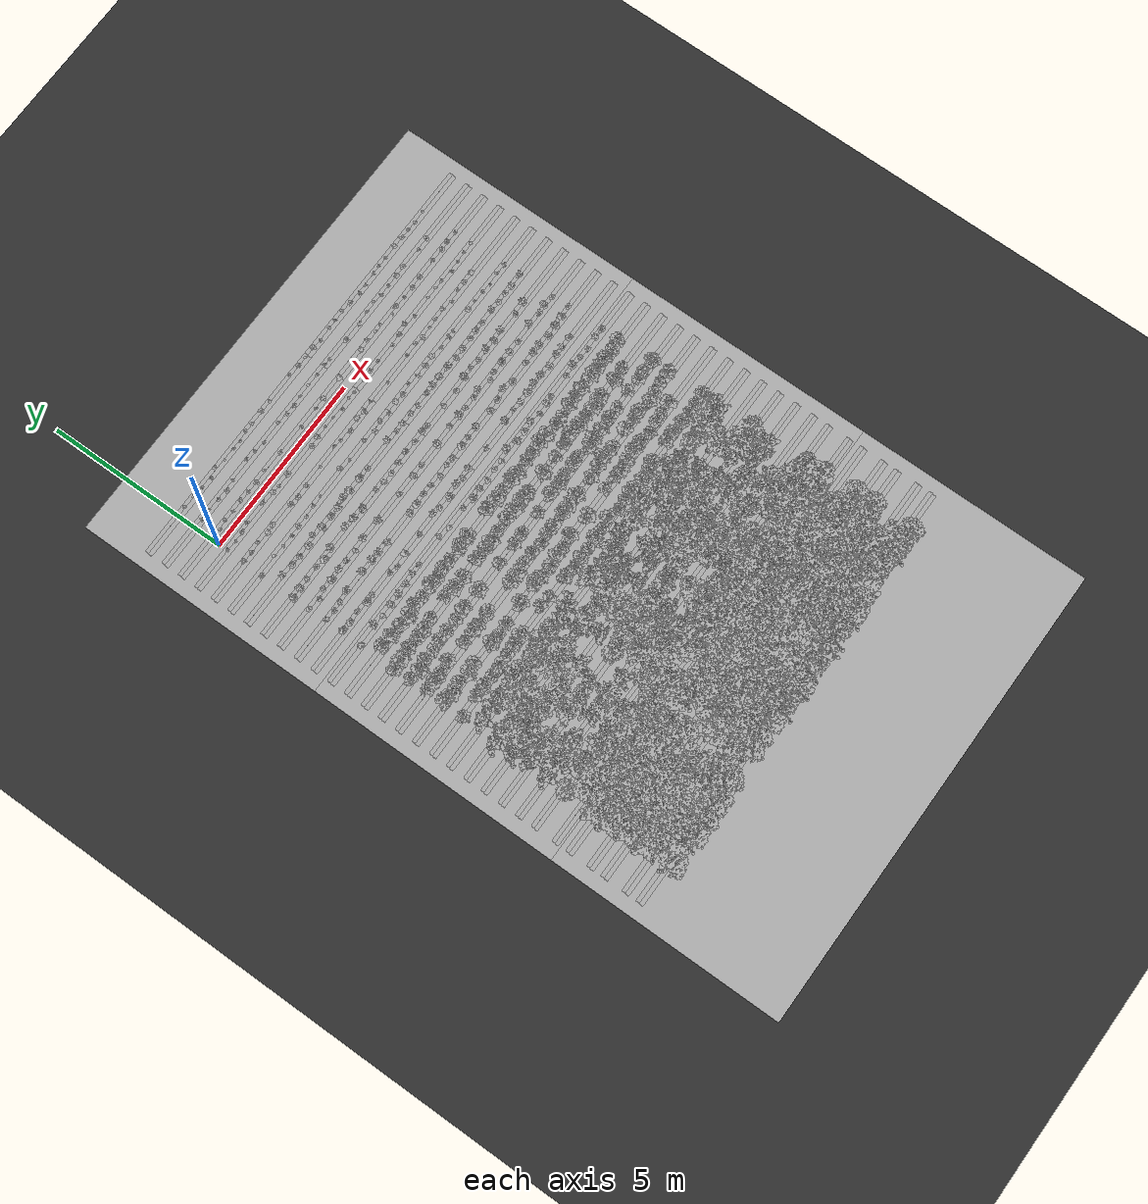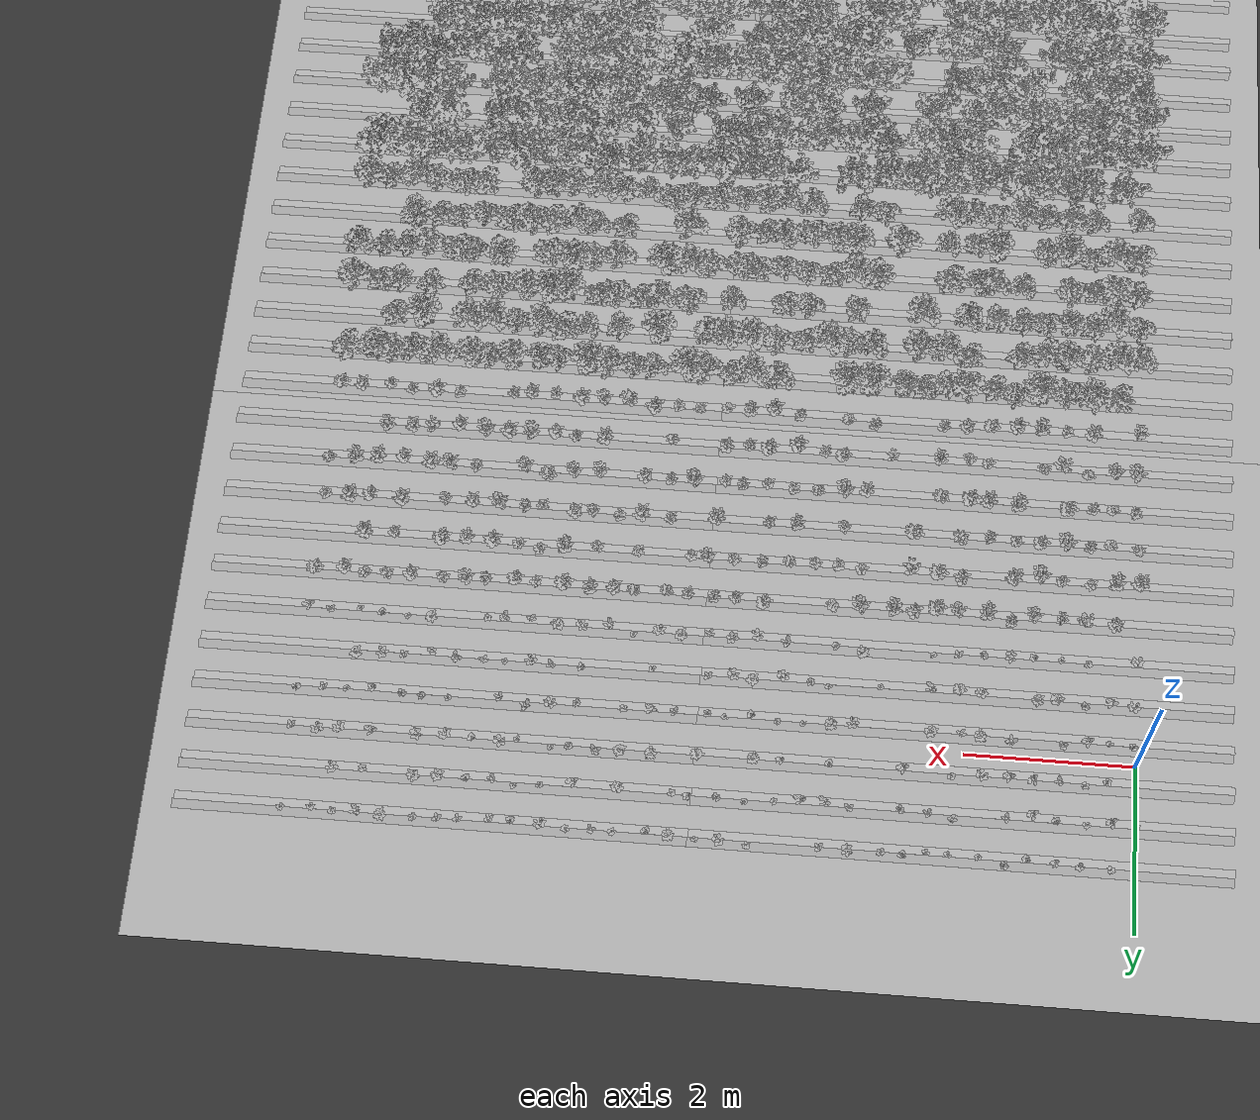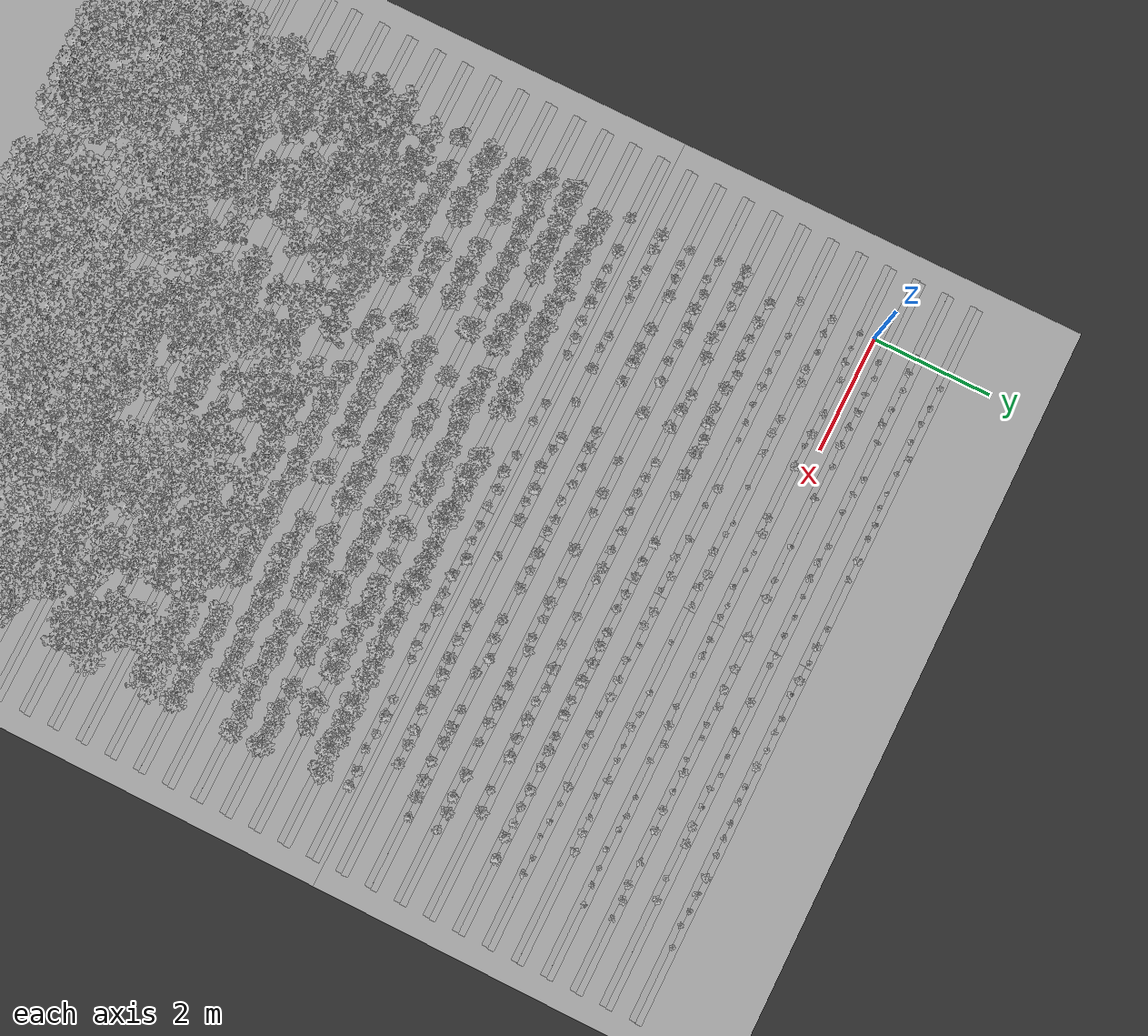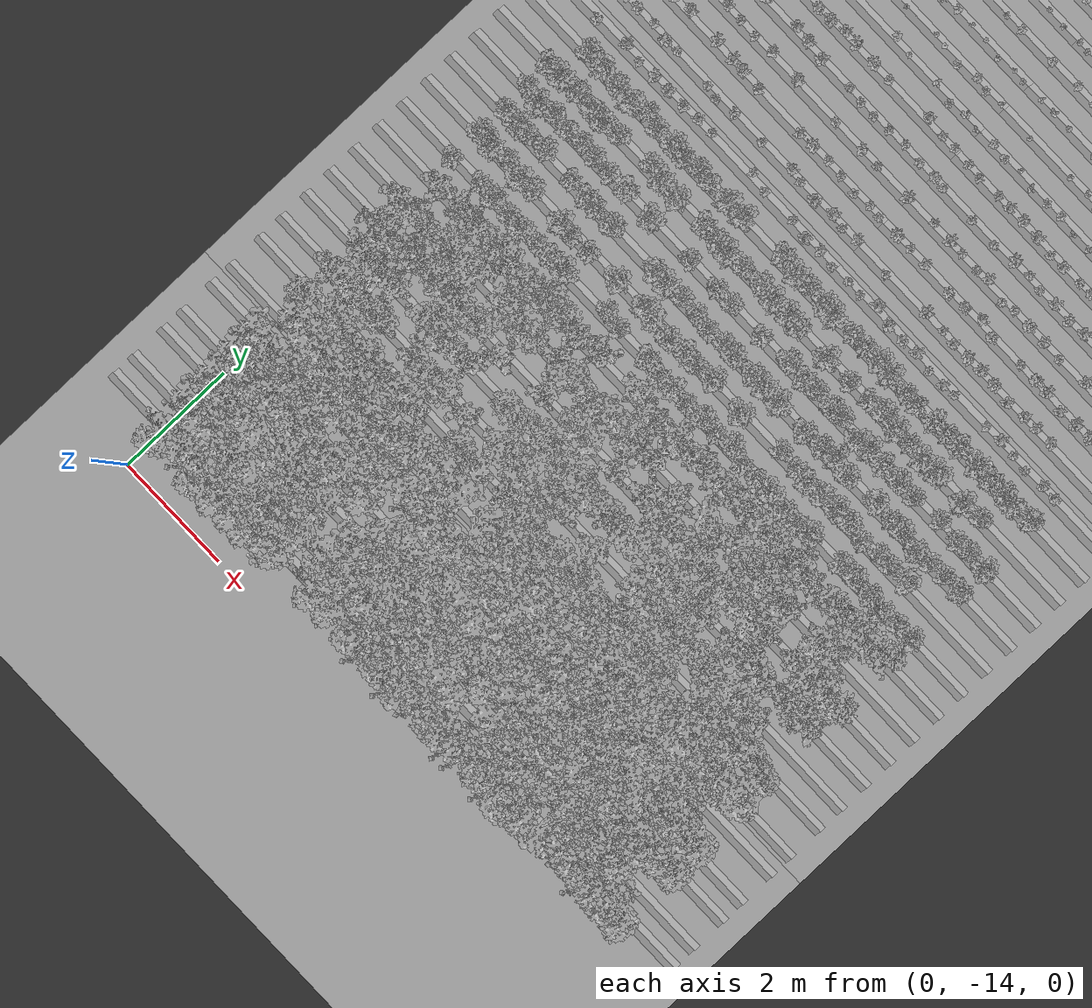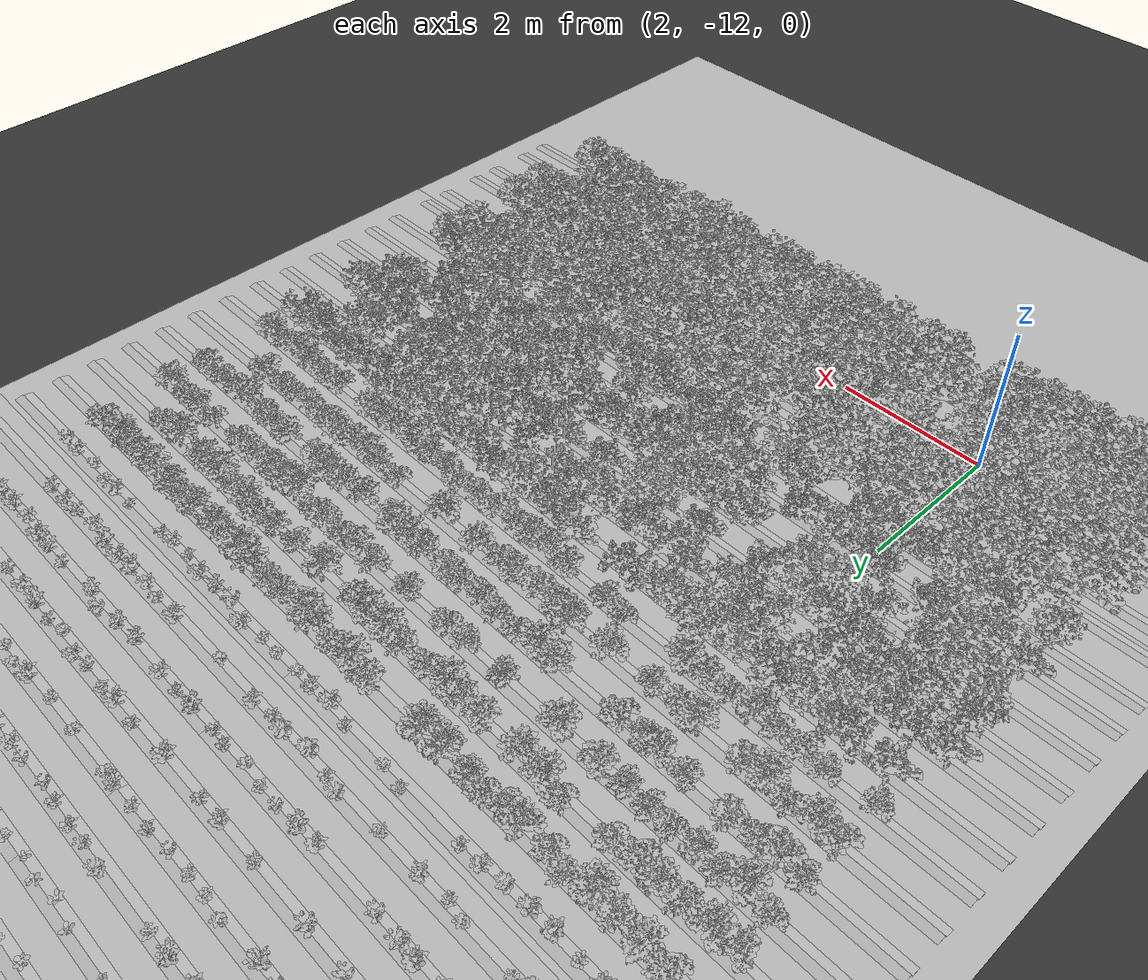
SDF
<sdf version="1.7">
 <world name="default">
  <light name="sun" type="directional">
   <pose>0 0 10 0 -0 0</pose>
   <diffuse>0.8 0.8 0.8 1</diffuse>
   <specular>0.2 0.2 0.2 1</specular>
   <attenuation>
    <range>1000</range>
    <constant>0.9</constant>
    <linear>0.01</linear>
    <quadratic>0.001</quadratic>
   </attenuation>
   <direction>-0.5 0.1 -0.9</direction>
   <spot><inner_angle>0</inner_angle><outer_angle>0</outer_angle><falloff>0</falloff></spot>
  </light>
  <model name="ground_plane">
   <static>1</static>
   <link name="link">
    <collision name="collision">
     <geometry><plane><normal>0 0 1</normal><size>100 100</size></plane></geometry>
     <surface>
      <contact><collide_bitmask>65535</collide_bitmask></contact>
      <friction><ode><mu>100</mu><mu2>50</mu2></ode></friction>
     </surface>
    </collision>
    <visual name="visual">
     <cast_shadows>0</cast_shadows>
     <geometry><plane><normal>0 0 1</normal><size>100 100</size></plane></geometry>
     <material>
      <ambient>0.2 0.2 0.2 1.0</ambient>
      <diffuse>0.2 0.2 0.2 1.0</diffuse>
      <specular>0.2 0.2 0.2 1.0</specular>
      <emissive>0.2 0.2 0.2 1.0</emissive>
     </material>
    </visual>
   </link>
  </model>
  <model name="ground">
   <pose>5 -0.5 0.01  3.141592654 0 0</pose>
   <static>true</static>
   <link name="body">
    <visual name="visual">
     <cast_shadows>0</cast_shadows>
     <geometry>
      <mesh><uri>file:///home/ifcosta/catkin_ws/src/cnn_line/worlds/models/ground.obj</uri></mesh>
     </geometry>
    </visual>
   </link>
  </model>
  <model name="ground_1">
   <pose>5 -7.4 0.01  3.1410592654 0 0</pose>
   <static>true</static>
   <link name="body">
    <visual name="visual">
     <cast_shadows>0</cast_shadows>
     <geometry>
      <mesh><uri>file:///home/ifcosta/catkin_ws/src/cnn_line/worlds/models/ground.obj</uri></mesh>
     </geometry>
    </visual>
   </link>
  </model>
  <model name="ground_2">
   <pose>5 -13.8 0.01  3.141592654 0 0</pose>
   <static>true</static>
   <link name="body">
    <visual name="visual">
     <cast_shadows>0</cast_shadows>
     <geometry>
      <mesh><uri>file:///home/ifcosta/catkin_ws/src/cnn_line/worlds/models/ground.obj</uri></mesh>
     </geometry>
    </visual>
   </link>
  </model>
  <model name="plt_0">
   <pose>-0.000553 -1.3 0.0132 0.0 0.0 0.6266</pose>
   <static>true</static>
   <link name="body">
    <visual name="visual">
     <geometry>
      <mesh><uri>file:///home/ifcosta/catkin_ws/src/cnn_line/worlds/models/plant2.obj</uri></mesh>
     </geometry>
    </visual>
   </link>
  </model>
  <model name="plt_10000">
   <pose>-0.000553 -4.3 0.0132 0.0 0.0 1.0333</pose>
   <static>true</static>
   <link name="body">
    <visual name="visual">
     <geometry>
      <mesh><uri>file:///home/ifcosta/catkin_ws/src/cnn_line/worlds/models/plant12.obj</uri></mesh>
     </geometry>
    </visual>
   </link>
  </model>
  <model name="plt_20000">
   <pose>-0.000553 -7.3 0.0132 0.0 0.0 -1.0122</pose>
   <static>true</static>
   <link name="body">
    <visual name="visual">
     <geometry>
      <mesh><uri>file:///home/ifcosta/catkin_ws/src/cnn_line/worlds/models/plant20.obj</uri></mesh>
     </geometry>
    </visual>
   </link>
  </model>
  <model name="plt_30000">
   <pose>-0.000553 -10.3 0.0132 0.0 0.0 0.64766</pose>
   <static>true</static>
   <link name="body">
    <visual name="visual">
     <geometry>
      <mesh><uri>file:///home/ifcosta/catkin_ws/src/cnn_line/worlds/models/plant35.obj</uri></mesh>
     </geometry>
    </visual>
   </link>
  </model>
  <model name="plt_40000">
   <pose>-0.000553 -13.3 0.0132 0.0 0.0 -1.082</pose>
   <static>true</static>
   <link name="body">
    <visual name="visual">
     <geometry>
      <mesh><uri>file:///home/ifcosta/catkin_ws/src/cnn_line/worlds/models/plant37.obj</uri></mesh>
     </geometry>
    </visual>
   </link>
  </model>
  <model name="plt_2">
   <pose>0.57 -1.24 0.0132 0.0 0.0 0.026245</pose>
   <static>true</static>
   <link name="body">
    <visual name="visual">
     <geometry>
      <mesh><uri>file:///home/ifcosta/catkin_ws/src/cnn_line/worlds/models/plant5.obj</uri></mesh>
     </geometry>
    </visual>
   </link>
  </model>
  <model name="plt_10002">
   <pose>0.57 -4.24 0.0132 0.0 0.0 -0.0059313</pose>
   <static>true</static>
   <link name="body">
    <visual name="visual">
     <geometry>
      <mesh><uri>file:///home/ifcosta/catkin_ws/src/cnn_line/worlds/models/plant13.obj</uri></mesh>
     </geometry>
    </visual>
   </link>
  </model>
  <model name="plt_20002">
   <pose>0.57 -7.24 0.0132 0.0 0.0 -1.0299</pose>
   <static>true</static>
   <link name="body">
    <visual name="visual">
     <geometry>
      <mesh><uri>file:///home/ifcosta/catkin_ws/src/cnn_line/worlds/models/plant20.obj</uri></mesh>
     </geometry>
    </visual>
   </link>
  </model>
  <model name="plt_30002">
   <pose>0.57 -10.2 0.0132 0.0 0.0 -0.59547</pose>
   <static>true</static>
   <link name="body">
    <visual name="visual">
     <geometry>
      <mesh><uri>file:///home/ifcosta/catkin_ws/src/cnn_line/worlds/models/plant30.obj</uri></mesh>
     </geometry>
    </visual>
   </link>
  </model>
  <model name="plt_40002">
   <pose>0.57 -13.2 0.0132 0.0 0.0 0.66731</pose>
   <static>true</static>
   <link name="body">
    <visual name="visual">
     <geometry>
      <mesh><uri>file:///home/ifcosta/catkin_ws/src/cnn_line/worlds/models/plant37.obj</uri></mesh>
     </geometry>
    </visual>
   </link>
  </model>
  <model name="plt_3">
   <pose>0.885 -1.27 0.0162 0.0 0.0 0.75018</pose>
   <static>true</static>
   <link name="body">
    <visual name="visual">
     <geometry>
      <mesh><uri>file:///home/ifcosta/catkin_ws/src/cnn_line/worlds/models/plant6.obj</uri></mesh>
     </geometry>
    </visual>
   </link>
  </model>
  <model name="plt_10003">
   <pose>0.885 -4.27 0.0162 0.0 0.0 0.86365</pose>
   <static>true</static>
   <link name="body">
    <visual name="visual">
     <geometry>
      <mesh><uri>file:///home/ifcosta/catkin_ws/src/cnn_line/worlds/models/plant10.obj</uri></mesh>
     </geometry>
    </visual>
   </link>
  </model>
  <model name="plt_20003">
   <pose>0.885 -7.27 0.0162 0.0 0.0 1.3435</pose>
   <static>true</static>
   <link name="body">
    <visual name="visual">
     <geometry>
      <mesh><uri>file:///home/ifcosta/catkin_ws/src/cnn_line/worlds/models/plant21.obj</uri></mesh>
     </geometry>
    </visual>
   </link>
  </model>
  <model name="plt_30003">
   <pose>0.885 -10.3 0.0162 0.0 0.0 1.7194</pose>
   <static>true</static>
   <link name="body">
    <visual name="visual">
     <geometry>
      <mesh><uri>file:///home/ifcosta/catkin_ws/src/cnn_line/worlds/models/plant35.obj</uri></mesh>
     </geometry>
    </visual>
   </link>
  </model>
  <model name="plt_40003">
   <pose>0.885 -13.3 0.0162 0.0 0.0 -1.0955</pose>
   <static>true</static>
   <link name="body">
    <visual name="visual">
     <geometry>
      <mesh><uri>file:///home/ifcosta/catkin_ws/src/cnn_line/worlds/models/plant37.obj</uri></mesh>
     </geometry>
    </visual>
   </link>
  </model>
  <model name="plt_4">
   <pose>1.21 -1.27 0.0178 0.0 0.0 1.1314</pose>
   <static>true</static>
   <link name="body">
    <visual name="visual">
     <geometry>
      <mesh><uri>file:///home/ifcosta/catkin_ws/src/cnn_line/worlds/models/plant7.obj</uri></mesh>
     </geometry>
    </visual>
   </link>
  </model>
  <model name="plt_10004">
   <pose>1.21 -4.27 0.0178 0.0 0.0 0.60568</pose>
   <static>true</static>
   <link name="body">
    <visual name="visual">
     <geometry>
      <mesh><uri>file:///home/ifcosta/catkin_ws/src/cnn_line/worlds/models/plant13.obj</uri></mesh>
     </geometry>
    </visual>
   </link>
  </model>
  <model name="plt_20004">
   <pose>1.21 -7.27 0.0178 0.0 0.0 0.6462</pose>
   <static>true</static>
   <link name="body">
    <visual name="visual">
     <geometry>
      <mesh><uri>file:///home/ifcosta/catkin_ws/src/cnn_line/worlds/models/plant20.obj</uri></mesh>
     </geometry>
    </visual>
   </link>
  </model>
  <model name="plt_30004">
   <pose>1.21 -10.3 0.0178 0.0 0.0 -1.0621</pose>
   <static>true</static>
   <link name="body">
    <visual name="visual">
     <geometry>
      <mesh><uri>file:///home/ifcosta/catkin_ws/src/cnn_line/worlds/models/plant36.obj</uri></mesh>
     </geometry>
    </visual>
   </link>
  </model>
  <model name="plt_40004">
   <pose>1.21 -13.3 0.0178 0.0 0.0 -0.34675</pose>
   <static>true</static>
   <link name="body">
    <visual name="visual">
     <geometry>
      <mesh><uri>file:///home/ifcosta/catkin_ws/src/cnn_line/worlds/models/plant37.obj</uri></mesh>
     </geometry>
    </visual>
   </link>
  </model>
  <model name="plt_5">
   <pose>1.5 -1.27 0.0163 0.0 0.0 -1.1657</pose>
   <static>true</static>
   <link name="body">
    <visual name="visual">
     <geometry>
      <mesh><uri>file:///home/ifcosta/catkin_ws/src/cnn_line/worlds/models/plant2.obj</uri></mesh>
     </geometry>
    </visual>
   </link>
  </model>
  <model name="plt_10005">
   <pose>1.5 -4.27 0.0163 0.0 0.0 -0.77135</pose>
   <static>true</static>
   <link name="body">
    <visual name="visual">
     <geometry>
      <mesh><uri>file:///home/ifcosta/catkin_ws/src/cnn_line/worlds/models/plant13.obj</uri></mesh>
     </geometry>
    </visual>
   </link>
  </model>
  <model name="plt_20005">
   <pose>1.5 -7.27 0.0163 0.0 0.0 -1.5363</pose>
   <static>true</static>
   <link name="body">
    <visual name="visual">
     <geometry>
      <mesh><uri>file:///home/ifcosta/catkin_ws/src/cnn_line/worlds/models/plant22.obj</uri></mesh>
     </geometry>
    </visual>
   </link>
  </model>
  <model name="plt_30005">
   <pose>1.5 -10.3 0.0163 0.0 0.0 1.4374</pose>
   <static>true</static>
   <link name="body">
    <visual name="visual">
     <geometry>
      <mesh><uri>file:///home/ifcosta/catkin_ws/src/cnn_line/worlds/models/plant31.obj</uri></mesh>
     </geometry>
    </visual>
   </link>
  </model>
  <model name="plt_40005">
   <pose>1.5 -13.3 0.0163 0.0 0.0 -0.058842</pose>
   <static>true</static>
   <link name="body">
    <visual name="visual">
     <geometry>
      <mesh><uri>file:///home/ifcosta/catkin_ws/src/cnn_line/worlds/models/plant37.obj</uri></mesh>
     </geometry>
    </visual>
   </link>
  </model>
  <model name="plt_6">
   <pose>1.82 -1.26 0.0144 0.0 0.0 -1.7405</pose>
   <static>true</static>
   <link name="body">
    <visual name="visual">
     <geometry>
      <mesh><uri>file:///home/ifcosta/catkin_ws/src/cnn_line/worlds/models/plant7.obj</uri></mesh>
     </geometry>
    </visual>
   </link>
  </model>
  <model name="plt_10006">
   <pose>1.82 -4.26 0.0144 0.0 0.0 -1.3984</pose>
   <static>true</static>
   <link name="body">
    <visual name="visual">
     <geometry>
      <mesh><uri>file:///home/ifcosta/catkin_ws/src/cnn_line/worlds/models/plant12.obj</uri></mesh>
     </geometry>
    </visual>
   </link>
  </model>
  <model name="plt_20006">
   <pose>1.82 -7.26 0.0144 0.0 0.0 -0.27954</pose>
   <static>true</static>
   <link name="body">
    <visual name="visual">
     <geometry>
      <mesh><uri>file:///home/ifcosta/catkin_ws/src/cnn_line/worlds/models/plant20.obj</uri></mesh>
     </geometry>
    </visual>
   </link>
  </model>
  <model name="plt_30006">
   <pose>1.82 -10.3 0.0144 0.0 0.0 0.010769</pose>
   <static>true</static>
   <link name="body">
    <visual name="visual">
     <geometry>
      <mesh><uri>file:///home/ifcosta/catkin_ws/src/cnn_line/worlds/models/plant33.obj</uri></mesh>
     </geometry>
    </visual>
   </link>
  </model>
  <model name="plt_40006">
   <pose>1.82 -13.3 0.0144 0.0 0.0 -0.086727</pose>
   <static>true</static>
   <link name="body">
    <visual name="visual">
     <geometry>
      <mesh><uri>file:///home/ifcosta/catkin_ws/src/cnn_line/worlds/models/plant37.obj</uri></mesh>
     </geometry>
    </visual>
   </link>
  </model>
  <model name="plt_7">
   <pose>2.12 -1.23 0.0155 0.0 0.0 0.28012</pose>
   <static>true</static>
   <link name="body">
    <visual name="visual">
     <geometry>
      <mesh><uri>file:///home/ifcosta/catkin_ws/src/cnn_line/worlds/models/plant1.obj</uri></mesh>
     </geometry>
    </visual>
   </link>
  </model>
  <model name="plt_10007">
   <pose>2.12 -4.23 0.0155 0.0 0.0 -0.46035</pose>
   <static>true</static>
   <link name="body">
    <visual name="visual">
     <geometry>
      <mesh><uri>file:///home/ifcosta/catkin_ws/src/cnn_line/worlds/models/plant12.obj</uri></mesh>
     </geometry>
    </visual>
   </link>
  </model>
  <model name="plt_20007">
   <pose>2.12 -7.23 0.0155 0.0 0.0 -0.53312</pose>
   <static>true</static>
   <link name="body">
    <visual name="visual">
     <geometry>
      <mesh><uri>file:///home/ifcosta/catkin_ws/src/cnn_line/worlds/models/plant21.obj</uri></mesh>
     </geometry>
    </visual>
   </link>
  </model>
  <model name="plt_30007">
   <pose>2.12 -10.2 0.0155 0.0 0.0 0.10091</pose>
   <static>true</static>
   <link name="body">
    <visual name="visual">
     <geometry>
      <mesh><uri>file:///home/ifcosta/catkin_ws/src/cnn_line/worlds/models/plant30.obj</uri></mesh>
     </geometry>
    </visual>
   </link>
  </model>
  <model name="plt_40007">
   <pose>2.12 -13.2 0.0155 0.0 0.0 3.1503</pose>
   <static>true</static>
   <link name="body">
    <visual name="visual">
     <geometry>
      <mesh><uri>file:///home/ifcosta/catkin_ws/src/cnn_line/worlds/models/plant37.obj</uri></mesh>
     </geometry>
    </visual>
   </link>
  </model>
  <model name="plt_8">
   <pose>2.41 -1.22 0.0153 0.0 0.0 0.33012</pose>
   <static>true</static>
   <link name="body">
    <visual name="visual">
     <geometry>
      <mesh><uri>file:///home/ifcosta/catkin_ws/src/cnn_line/worlds/models/plant4.obj</uri></mesh>
     </geometry>
    </visual>
   </link>
  </model>
  <model name="plt_10008">
   <pose>2.41 -4.22 0.0153 0.0 0.0 0.11484</pose>
   <static>true</static>
   <link name="body">
    <visual name="visual">
     <geometry>
      <mesh><uri>file:///home/ifcosta/catkin_ws/src/cnn_line/worlds/models/plant11.obj</uri></mesh>
     </geometry>
    </visual>
   </link>
  </model>
  <model name="plt_20008">
   <pose>2.41 -7.22 0.0153 0.0 0.0 -0.33632</pose>
   <static>true</static>
   <link name="body">
    <visual name="visual">
     <geometry>
      <mesh><uri>file:///home/ifcosta/catkin_ws/src/cnn_line/worlds/models/plant22.obj</uri></mesh>
     </geometry>
    </visual>
   </link>
  </model>
  <model name="plt_30008">
   <pose>2.41 -10.2 0.0153 0.0 0.0 1.6546</pose>
   <static>true</static>
   <link name="body">
    <visual name="visual">
     <geometry>
      <mesh><uri>file:///home/ifcosta/catkin_ws/src/cnn_line/worlds/models/plant33.obj</uri></mesh>
     </geometry>
    </visual>
   </link>
  </model>
  <model name="plt_40008">
   <pose>2.41 -13.2 0.0153 0.0 0.0 -0.53902</pose>
   <static>true</static>
   <link name="body">
    <visual name="visual">
     <geometry>
      <mesh><uri>file:///home/ifcosta/catkin_ws/src/cnn_line/worlds/models/plant37.obj</uri></mesh>
     </geometry>
    </visual>
   </link>
  </model>
  <model name="plt_11">
   <pose>3.26 -1.18 0.0165 0.0 0.0 0.89227</pose>
   <static>true</static>
   <link name="body">
    <visual name="visual">
     <geometry>
      <mesh><uri>file:///home/ifcosta/catkin_ws/src/cnn_line/worlds/models/plant0.obj</uri></mesh>
     </geometry>
    </visual>
   </link>
  </model>
  <model name="plt_10011">
   <pose>3.26 -4.18 0.0165 0.0 0.0 0.14861</pose>
   <static>true</static>
   <link name="body">
    <visual name="visual">
     <geometry>
      <mesh><uri>file:///home/ifcosta/catkin_ws/src/cnn_line/worlds/models/plant11.obj</uri></mesh>
     </geometry>
    </visual>
   </link>
  </model>
  <model name="plt_20011">
   <pose>3.26 -7.18 0.0165 0.0 0.0 -0.31515</pose>
   <static>true</static>
   <link name="body">
    <visual name="visual">
     <geometry>
      <mesh><uri>file:///home/ifcosta/catkin_ws/src/cnn_line/worlds/models/plant20.obj</uri></mesh>
     </geometry>
    </visual>
   </link>
  </model>
  <model name="plt_30011">
   <pose>3.26 -10.2 0.0165 0.0 0.0 -0.16523</pose>
   <static>true</static>
   <link name="body">
    <visual name="visual">
     <geometry>
      <mesh><uri>file:///home/ifcosta/catkin_ws/src/cnn_line/worlds/models/plant35.obj</uri></mesh>
     </geometry>
    </visual>
   </link>
  </model>
  <model name="plt_40011">
   <pose>3.26 -13.2 0.0165 0.0 0.0 -0.62735</pose>
   <static>true</static>
   <link name="body">
    <visual name="visual">
     <geometry>
      <mesh><uri>file:///home/ifcosta/catkin_ws/src/cnn_line/worlds/models/plant37.obj</uri></mesh>
     </geometry>
    </visual>
   </link>
  </model>
  <model name="plt_12">
   <pose>3.58 -1.24 0.012 0.0 0.0 0.88482</pose>
   <static>true</static>
   <link name="body">
    <visual name="visual">
     <geometry>
      <mesh><uri>file:///home/ifcosta/catkin_ws/src/cnn_line/worlds/models/plant5.obj</uri></mesh>
     </geometry>
    </visual>
   </link>
  </model>
  <model name="plt_10012">
   <pose>3.58 -4.24 0.012 0.0 0.0 -1.2011</pose>
   <static>true</static>
   <link name="body">
    <visual name="visual">
     <geometry>
      <mesh><uri>file:///home/ifcosta/catkin_ws/src/cnn_line/worlds/models/plant10.obj</uri></mesh>
     </geometry>
    </visual>
   </link>
  </model>
  <model name="plt_20012">
   <pose>3.58 -7.24 0.012 0.0 0.0 1.1312</pose>
   <static>true</static>
   <link name="body">
    <visual name="visual">
     <geometry>
      <mesh><uri>file:///home/ifcosta/catkin_ws/src/cnn_line/worlds/models/plant20.obj</uri></mesh>
     </geometry>
    </visual>
   </link>
  </model>
  <model name="plt_30012">
   <pose>3.58 -10.2 0.012 0.0 0.0 -2.3557</pose>
   <static>true</static>
   <link name="body">
    <visual name="visual">
     <geometry>
      <mesh><uri>file:///home/ifcosta/catkin_ws/src/cnn_line/worlds/models/plant36.obj</uri></mesh>
     </geometry>
    </visual>
   </link>
  </model>
  <model name="plt_40012">
   <pose>3.58 -13.2 0.012 0.0 0.0 -0.29448</pose>
   <static>true</static>
   <link name="body">
    <visual name="visual">
     <geometry>
      <mesh><uri>file:///home/ifcosta/catkin_ws/src/cnn_line/worlds/models/plant37.obj</uri></mesh>
     </geometry>
    </visual>
   </link>
  </model>
  <model name="plt_14">
   <pose>4.19 -1.23 0.0128 0.0 0.0 -2.1002</pose>
   <static>true</static>
   <link name="body">
    <visual name="visual">
     <geometry>
      <mesh><uri>file:///home/ifcosta/catkin_ws/src/cnn_line/worlds/models/plant3.obj</uri></mesh>
     </geometry>
    </visual>
   </link>
  </model>
  <model name="plt_10014">
   <pose>4.19 -4.23 0.0128 0.0 0.0 0.37589</pose>
   <static>true</static>
   <link name="body">
    <visual name="visual">
     <geometry>
      <mesh><uri>file:///home/ifcosta/catkin_ws/src/cnn_line/worlds/models/plant11.obj</uri></mesh>
     </geometry>
    </visual>
   </link>
  </model>
  <model name="plt_20014">
   <pose>4.19 -7.23 0.0128 0.0 0.0 -0.44411</pose>
   <static>true</static>
   <link name="body">
    <visual name="visual">
     <geometry>
      <mesh><uri>file:///home/ifcosta/catkin_ws/src/cnn_line/worlds/models/plant21.obj</uri></mesh>
     </geometry>
    </visual>
   </link>
  </model>
  <model name="plt_30014">
   <pose>4.19 -10.2 0.0128 0.0 0.0 -1.7118</pose>
   <static>true</static>
   <link name="body">
    <visual name="visual">
     <geometry>
      <mesh><uri>file:///home/ifcosta/catkin_ws/src/cnn_line/worlds/models/plant33.obj</uri></mesh>
     </geometry>
    </visual>
   </link>
  </model>
  <model name="plt_40014">
   <pose>4.19 -13.2 0.0128 0.0 0.0 -1.1602</pose>
   <static>true</static>
   <link name="body">
    <visual name="visual">
     <geometry>
      <mesh><uri>file:///home/ifcosta/catkin_ws/src/cnn_line/worlds/models/plant37.obj</uri></mesh>
     </geometry>
    </visual>
   </link>
  </model>
  <model name="plt_15">
   <pose>4.51 -1.29 0.0145 0.0 0.0 2.1529</pose>
   <static>true</static>
   <link name="body">
    <visual name="visual">
     <geometry>
      <mesh><uri>file:///home/ifcosta/catkin_ws/src/cnn_line/worlds/models/plant2.obj</uri></mesh>
     </geometry>
    </visual>
   </link>
  </model>
  <model name="plt_10015">
   <pose>4.51 -4.29 0.0145 0.0 0.0 -0.54911</pose>
   <static>true</static>
   <link name="body">
    <visual name="visual">
     <geometry>
      <mesh><uri>file:///home/ifcosta/catkin_ws/src/cnn_line/worlds/models/plant13.obj</uri></mesh>
     </geometry>
    </visual>
   </link>
  </model>
  <model name="plt_20015">
   <pose>4.51 -7.29 0.0145 0.0 0.0 -0.4392</pose>
   <static>true</static>
   <link name="body">
    <visual name="visual">
     <geometry>
      <mesh><uri>file:///home/ifcosta/catkin_ws/src/cnn_line/worlds/models/plant21.obj</uri></mesh>
     </geometry>
    </visual>
   </link>
  </model>
  <model name="plt_30015">
   <pose>4.51 -10.3 0.0145 0.0 0.0 0.97449</pose>
   <static>true</static>
   <link name="body">
    <visual name="visual">
     <geometry>
      <mesh><uri>file:///home/ifcosta/catkin_ws/src/cnn_line/worlds/models/plant31.obj</uri></mesh>
     </geometry>
    </visual>
   </link>
  </model>
  <model name="plt_40015">
   <pose>4.51 -13.3 0.0145 0.0 0.0 0.50565</pose>
   <static>true</static>
   <link name="body">
    <visual name="visual">
     <geometry>
      <mesh><uri>file:///home/ifcosta/catkin_ws/src/cnn_line/worlds/models/plant37.obj</uri></mesh>
     </geometry>
    </visual>
   </link>
  </model>
  <model name="plt_16">
   <pose>4.81 -1.25 0.0153 0.0 0.0 -1.7667</pose>
   <static>true</static>
   <link name="body">
    <visual name="visual">
     <geometry>
      <mesh><uri>file:///home/ifcosta/catkin_ws/src/cnn_line/worlds/models/plant2.obj</uri></mesh>
     </geometry>
    </visual>
   </link>
  </model>
  <model name="plt_10016">
   <pose>4.81 -4.25 0.0153 0.0 0.0 0.62297</pose>
   <static>true</static>
   <link name="body">
    <visual name="visual">
     <geometry>
      <mesh><uri>file:///home/ifcosta/catkin_ws/src/cnn_line/worlds/models/plant12.obj</uri></mesh>
     </geometry>
    </visual>
   </link>
  </model>
  <model name="plt_20016">
   <pose>4.81 -7.25 0.0153 0.0 0.0 -1.3693</pose>
   <static>true</static>
   <link name="body">
    <visual name="visual">
     <geometry>
      <mesh><uri>file:///home/ifcosta/catkin_ws/src/cnn_line/worlds/models/plant21.obj</uri></mesh>
     </geometry>
    </visual>
   </link>
  </model>
  <model name="plt_30016">
   <pose>4.81 -10.2 0.0153 0.0 0.0 1.1248</pose>
   <static>true</static>
   <link name="body">
    <visual name="visual">
     <geometry>
      <mesh><uri>file:///home/ifcosta/catkin_ws/src/cnn_line/worlds/models/plant35.obj</uri></mesh>
     </geometry>
    </visual>
   </link>
  </model>
  <model name="plt_40016">
   <pose>4.81 -13.2 0.0153 0.0 0.0 -1.4041</pose>
   <static>true</static>
   <link name="body">
    <visual name="visual">
     <geometry>
      <mesh><uri>file:///home/ifcosta/catkin_ws/src/cnn_line/worlds/models/plant37.obj</uri></mesh>
     </geometry>
    </visual>
   </link>
  </model>
  <model name="plt_17">
   <pose>5.09 -1.28 0.0143 0.0 0.0 -0.75219</pose>
   <static>true</static>
   <link name="body">
    <visual name="visual">
     <geometry>
      <mesh><uri>file:///home/ifcosta/catkin_ws/src/cnn_line/worlds/models/plant1.obj</uri></mesh>
     </geometry>
    </visual>
   </link>
  </model>
  <model name="plt_10017">
   <pose>5.09 -4.28 0.0143 0.0 0.0 -0.89188</pose>
   <static>true</static>
   <link name="body">
    <visual name="visual">
     <geometry>
      <mesh><uri>file:///home/ifcosta/catkin_ws/src/cnn_line/worlds/models/plant10.obj</uri></mesh>
     </geometry>
    </visual>
   </link>
  </model>
  <model name="plt_20017">
   <pose>5.09 -7.28 0.0143 0.0 0.0 -0.16303</pose>
   <static>true</static>
   <link name="body">
    <visual name="visual">
     <geometry>
      <mesh><uri>file:///home/ifcosta/catkin_ws/src/cnn_line/worlds/models/plant20.obj</uri></mesh>
     </geometry>
    </visual>
   </link>
  </model>
  <model name="plt_30017">
   <pose>5.09 -10.3 0.0143 0.0 0.0 -1.6119</pose>
   <static>true</static>
   <link name="body">
    <visual name="visual">
     <geometry>
      <mesh><uri>file:///home/ifcosta/catkin_ws/src/cnn_line/worlds/models/plant34.obj</uri></mesh>
     </geometry>
    </visual>
   </link>
  </model>
  <model name="plt_40017">
   <pose>5.09 -13.3 0.0143 0.0 0.0 0.80625</pose>
   <static>true</static>
   <link name="body">
    <visual name="visual">
     <geometry>
      <mesh><uri>file:///home/ifcosta/catkin_ws/src/cnn_line/worlds/models/plant37.obj</uri></mesh>
     </geometry>
    </visual>
   </link>
  </model>
  <model name="plt_18">
   <pose>5.43 -1.24 0.0139 0.0 0.0 0.06974</pose>
   <static>true</static>
   <link name="body">
    <visual name="visual">
     <geometry>
      <mesh><uri>file:///home/ifcosta/catkin_ws/src/cnn_line/worlds/models/plant0.obj</uri></mesh>
     </geometry>
    </visual>
   </link>
  </model>
  <model name="plt_10018">
   <pose>5.43 -4.24 0.0139 0.0 0.0 2.3928</pose>
   <static>true</static>
   <link name="body">
    <visual name="visual">
     <geometry>
      <mesh><uri>file:///home/ifcosta/catkin_ws/src/cnn_line/worlds/models/plant10.obj</uri></mesh>
     </geometry>
    </visual>
   </link>
  </model>
  <model name="plt_20018">
   <pose>5.43 -7.24 0.0139 0.0 0.0 1.0683</pose>
   <static>true</static>
   <link name="body">
    <visual name="visual">
     <geometry>
      <mesh><uri>file:///home/ifcosta/catkin_ws/src/cnn_line/worlds/models/plant21.obj</uri></mesh>
     </geometry>
    </visual>
   </link>
  </model>
  <model name="plt_30018">
   <pose>5.43 -10.2 0.0139 0.0 0.0 -0.18244</pose>
   <static>true</static>
   <link name="body">
    <visual name="visual">
     <geometry>
      <mesh><uri>file:///home/ifcosta/catkin_ws/src/cnn_line/worlds/models/plant35.obj</uri></mesh>
     </geometry>
    </visual>
   </link>
  </model>
  <model name="plt_40018">
   <pose>5.43 -13.2 0.0139 0.0 0.0 1.9287</pose>
   <static>true</static>
   <link name="body">
    <visual name="visual">
     <geometry>
      <mesh><uri>file:///home/ifcosta/catkin_ws/src/cnn_line/worlds/models/plant37.obj</uri></mesh>
     </geometry>
    </visual>
   </link>
  </model>
  <model name="plt_19">
   <pose>5.7 -1.26 0.0103 0.0 0.0 0.90144</pose>
   <static>true</static>
   <link name="body">
    <visual name="visual">
     <geometry>
      <mesh><uri>file:///home/ifcosta/catkin_ws/src/cnn_line/worlds/models/plant2.obj</uri></mesh>
     </geometry>
    </visual>
   </link>
  </model>
  <model name="plt_10019">
   <pose>5.7 -4.26 0.0103 0.0 0.0 0.79482</pose>
   <static>true</static>
   <link name="body">
    <visual name="visual">
     <geometry>
      <mesh><uri>file:///home/ifcosta/catkin_ws/src/cnn_line/worlds/models/plant10.obj</uri></mesh>
     </geometry>
    </visual>
   </link>
  </model>
  <model name="plt_20019">
   <pose>5.7 -7.26 0.0103 0.0 0.0 -0.6353</pose>
   <static>true</static>
   <link name="body">
    <visual name="visual">
     <geometry>
      <mesh><uri>file:///home/ifcosta/catkin_ws/src/cnn_line/worlds/models/plant20.obj</uri></mesh>
     </geometry>
    </visual>
   </link>
  </model>
  <model name="plt_30019">
   <pose>5.7 -10.3 0.0103 0.0 0.0 -1.4289</pose>
   <static>true</static>
   <link name="body">
    <visual name="visual">
     <geometry>
      <mesh><uri>file:///home/ifcosta/catkin_ws/src/cnn_line/worlds/models/plant36.obj</uri></mesh>
     </geometry>
    </visual>
   </link>
  </model>
  <model name="plt_40019">
   <pose>5.7 -13.3 0.0103 0.0 0.0 0.30642</pose>
   <static>true</static>
   <link name="body">
    <visual name="visual">
     <geometry>
      <mesh><uri>file:///home/ifcosta/catkin_ws/src/cnn_line/worlds/models/plant37.obj</uri></mesh>
     </geometry>
    </visual>
   </link>
  </model>
  <model name="plt_20">
   <pose>5.99 -1.2 0.0155 0.0 0.0 0.1638</pose>
   <static>true</static>
   <link name="body">
    <visual name="visual">
     <geometry>
      <mesh><uri>file:///home/ifcosta/catkin_ws/src/cnn_line/worlds/models/plant6.obj</uri></mesh>
     </geometry>
    </visual>
   </link>
  </model>
  <model name="plt_10020">
   <pose>5.99 -4.2 0.0155 0.0 0.0 -0.5302</pose>
   <static>true</static>
   <link name="body">
    <visual name="visual">
     <geometry>
      <mesh><uri>file:///home/ifcosta/catkin_ws/src/cnn_line/worlds/models/plant13.obj</uri></mesh>
     </geometry>
    </visual>
   </link>
  </model>
  <model name="plt_20020">
   <pose>5.99 -7.2 0.0155 0.0 0.0 0.67923</pose>
   <static>true</static>
   <link name="body">
    <visual name="visual">
     <geometry>
      <mesh><uri>file:///home/ifcosta/catkin_ws/src/cnn_line/worlds/models/plant21.obj</uri></mesh>
     </geometry>
    </visual>
   </link>
  </model>
  <model name="plt_30020">
   <pose>5.99 -10.2 0.0155 0.0 0.0 -0.10575</pose>
   <static>true</static>
   <link name="body">
    <visual name="visual">
     <geometry>
      <mesh><uri>file:///home/ifcosta/catkin_ws/src/cnn_line/worlds/models/plant35.obj</uri></mesh>
     </geometry>
    </visual>
   </link>
  </model>
  <model name="plt_40020">
   <pose>5.99 -13.2 0.0155 0.0 0.0 -2.019</pose>
   <static>true</static>
   <link name="body">
    <visual name="visual">
     <geometry>
      <mesh><uri>file:///home/ifcosta/catkin_ws/src/cnn_line/worlds/models/plant37.obj</uri></mesh>
     </geometry>
    </visual>
   </link>
  </model>
  <model name="plt_21">
   <pose>6.31 -1.28 0.0148 0.0 0.0 -1.6709</pose>
   <static>true</static>
   <link name="body">
    <visual name="visual">
     <geometry>
      <mesh><uri>file:///home/ifcosta/catkin_ws/src/cnn_line/worlds/models/plant3.obj</uri></mesh>
     </geometry>
    </visual>
   </link>
  </model>
  <model name="plt_10021">
   <pose>6.31 -4.28 0.0148 0.0 0.0 -1.7333</pose>
   <static>true</static>
   <link name="body">
    <visual name="visual">
     <geometry>
      <mesh><uri>file:///home/ifcosta/catkin_ws/src/cnn_line/worlds/models/plant13.obj</uri></mesh>
     </geometry>
    </visual>
   </link>
  </model>
  <model name="plt_20021">
   <pose>6.31 -7.28 0.0148 0.0 0.0 -1.3733</pose>
   <static>true</static>
   <link name="body">
    <visual name="visual">
     <geometry>
      <mesh><uri>file:///home/ifcosta/catkin_ws/src/cnn_line/worlds/models/plant20.obj</uri></mesh>
     </geometry>
    </visual>
   </link>
  </model>
  <model name="plt_30021">
   <pose>6.31 -10.3 0.0148 0.0 0.0 0.13132</pose>
   <static>true</static>
   <link name="body">
    <visual name="visual">
     <geometry>
      <mesh><uri>file:///home/ifcosta/catkin_ws/src/cnn_line/worlds/models/plant31.obj</uri></mesh>
     </geometry>
    </visual>
   </link>
  </model>
  <model name="plt_40021">
   <pose>6.31 -13.3 0.0148 0.0 0.0 0.96213</pose>
   <static>true</static>
   <link name="body">
    <visual name="visual">
     <geometry>
      <mesh><uri>file:///home/ifcosta/catkin_ws/src/cnn_line/worlds/models/plant37.obj</uri></mesh>
     </geometry>
    </visual>
   </link>
  </model>
  <model name="plt_22">
   <pose>6.63 -1.27 0.0137 0.0 0.0 -0.39329</pose>
   <static>true</static>
   <link name="body">
    <visual name="visual">
     <geometry>
      <mesh><uri>file:///home/ifcosta/catkin_ws/src/cnn_line/worlds/models/plant2.obj</uri></mesh>
     </geometry>
    </visual>
   </link>
  </model>
  <model name="plt_10022">
   <pose>6.63 -4.27 0.0137 0.0 0.0 1.5613</pose>
   <static>true</static>
   <link name="body">
    <visual name="visual">
     <geometry>
      <mesh><uri>file:///home/ifcosta/catkin_ws/src/cnn_line/worlds/models/plant12.obj</uri></mesh>
     </geometry>
    </visual>
   </link>
  </model>
  <model name="plt_20022">
   <pose>6.63 -7.27 0.0137 0.0 0.0 -1.9299</pose>
   <static>true</static>
   <link name="body">
    <visual name="visual">
     <geometry>
      <mesh><uri>file:///home/ifcosta/catkin_ws/src/cnn_line/worlds/models/plant20.obj</uri></mesh>
     </geometry>
    </visual>
   </link>
  </model>
  <model name="plt_30022">
   <pose>6.63 -10.3 0.0137 0.0 0.0 -0.75681</pose>
   <static>true</static>
   <link name="body">
    <visual name="visual">
     <geometry>
      <mesh><uri>file:///home/ifcosta/catkin_ws/src/cnn_line/worlds/models/plant33.obj</uri></mesh>
     </geometry>
    </visual>
   </link>
  </model>
  <model name="plt_40022">
   <pose>6.63 -13.3 0.0137 0.0 0.0 0.63949</pose>
   <static>true</static>
   <link name="body">
    <visual name="visual">
     <geometry>
      <mesh><uri>file:///home/ifcosta/catkin_ws/src/cnn_line/worlds/models/plant37.obj</uri></mesh>
     </geometry>
    </visual>
   </link>
  </model>
  <model name="plt_23">
   <pose>6.9 -1.25 0.0141 0.0 0.0 -1.9049</pose>
   <static>true</static>
   <link name="body">
    <visual name="visual">
     <geometry>
      <mesh><uri>file:///home/ifcosta/catkin_ws/src/cnn_line/worlds/models/plant0.obj</uri></mesh>
     </geometry>
    </visual>
   </link>
  </model>
  <model name="plt_10023">
   <pose>6.9 -4.25 0.0141 0.0 0.0 -0.33479</pose>
   <static>true</static>
   <link name="body">
    <visual name="visual">
     <geometry>
      <mesh><uri>file:///home/ifcosta/catkin_ws/src/cnn_line/worlds/models/plant13.obj</uri></mesh>
     </geometry>
    </visual>
   </link>
  </model>
  <model name="plt_20023">
   <pose>6.9 -7.25 0.0141 0.0 0.0 0.044499</pose>
   <static>true</static>
   <link name="body">
    <visual name="visual">
     <geometry>
      <mesh><uri>file:///home/ifcosta/catkin_ws/src/cnn_line/worlds/models/plant22.obj</uri></mesh>
     </geometry>
    </visual>
   </link>
  </model>
  <model name="plt_30023">
   <pose>6.9 -10.2 0.0141 0.0 0.0 0.03837</pose>
   <static>true</static>
   <link name="body">
    <visual name="visual">
     <geometry>
      <mesh><uri>file:///home/ifcosta/catkin_ws/src/cnn_line/worlds/models/plant33.obj</uri></mesh>
     </geometry>
    </visual>
   </link>
  </model>
  <model name="plt_40023">
   <pose>6.9 -13.2 0.0141 0.0 0.0 -0.55546</pose>
   <static>true</static>
   <link name="body">
    <visual name="visual">
     <geometry>
      <mesh><uri>file:///home/ifcosta/catkin_ws/src/cnn_line/worlds/models/plant37.obj</uri></mesh>
     </geometry>
    </visual>
   </link>
  </model>
  <model name="plt_24">
   <pose>7.23 -1.3 0.0149 0.0 0.0 -0.65293</pose>
   <static>true</static>
   <link name="body">
    <visual name="visual">
     <geometry>
      <mesh><uri>file:///home/ifcosta/catkin_ws/src/cnn_line/worlds/models/plant1.obj</uri></mesh>
     </geometry>
    </visual>
   </link>
  </model>
  <model name="plt_10024">
   <pose>7.23 -4.3 0.0149 0.0 0.0 0.36856</pose>
   <static>true</static>
   <link name="body">
    <visual name="visual">
     <geometry>
      <mesh><uri>file:///home/ifcosta/catkin_ws/src/cnn_line/worlds/models/plant11.obj</uri></mesh>
     </geometry>
    </visual>
   </link>
  </model>
  <model name="plt_20024">
   <pose>7.23 -7.3 0.0149 0.0 0.0 -0.090248</pose>
   <static>true</static>
   <link name="body">
    <visual name="visual">
     <geometry>
      <mesh><uri>file:///home/ifcosta/catkin_ws/src/cnn_line/worlds/models/plant21.obj</uri></mesh>
     </geometry>
    </visual>
   </link>
  </model>
  <model name="plt_30024">
   <pose>7.23 -10.3 0.0149 0.0 0.0 -0.47125</pose>
   <static>true</static>
   <link name="body">
    <visual name="visual">
     <geometry>
      <mesh><uri>file:///home/ifcosta/catkin_ws/src/cnn_line/worlds/models/plant32.obj</uri></mesh>
     </geometry>
    </visual>
   </link>
  </model>
  <model name="plt_40024">
   <pose>7.23 -13.3 0.0149 0.0 0.0 0.73686</pose>
   <static>true</static>
   <link name="body">
    <visual name="visual">
     <geometry>
      <mesh><uri>file:///home/ifcosta/catkin_ws/src/cnn_line/worlds/models/plant37.obj</uri></mesh>
     </geometry>
    </visual>
   </link>
  </model>
  <model name="plt_25">
   <pose>7.53 -1.29 0.0139 0.0 0.0 0.92249</pose>
   <static>true</static>
   <link name="body">
    <visual name="visual">
     <geometry>
      <mesh><uri>file:///home/ifcosta/catkin_ws/src/cnn_line/worlds/models/plant3.obj</uri></mesh>
     </geometry>
    </visual>
   </link>
  </model>
  <model name="plt_10025">
   <pose>7.53 -4.29 0.0139 0.0 0.0 -0.26293</pose>
   <static>true</static>
   <link name="body">
    <visual name="visual">
     <geometry>
      <mesh><uri>file:///home/ifcosta/catkin_ws/src/cnn_line/worlds/models/plant12.obj</uri></mesh>
     </geometry>
    </visual>
   </link>
  </model>
  <model name="plt_20025">
   <pose>7.53 -7.29 0.0139 0.0 0.0 -2.0363</pose>
   <static>true</static>
   <link name="body">
    <visual name="visual">
     <geometry>
      <mesh><uri>file:///home/ifcosta/catkin_ws/src/cnn_line/worlds/models/plant21.obj</uri></mesh>
     </geometry>
    </visual>
   </link>
  </model>
  <model name="plt_30025">
   <pose>7.53 -10.3 0.0139 0.0 0.0 0.48638</pose>
   <static>true</static>
   <link name="body">
    <visual name="visual">
     <geometry>
      <mesh><uri>file:///home/ifcosta/catkin_ws/src/cnn_line/worlds/models/plant32.obj</uri></mesh>
     </geometry>
    </visual>
   </link>
  </model>
  <model name="plt_40025">
   <pose>7.53 -13.3 0.0139 0.0 0.0 -1.293</pose>
   <static>true</static>
   <link name="body">
    <visual name="visual">
     <geometry>
      <mesh><uri>file:///home/ifcosta/catkin_ws/src/cnn_line/worlds/models/plant37.obj</uri></mesh>
     </geometry>
    </visual>
   </link>
  </model>
  <model name="plt_26">
   <pose>7.75 -1.27 0.0156 0.0 0.0 -1.7883</pose>
   <static>true</static>
   <link name="body">
    <visual name="visual">
     <geometry>
      <mesh><uri>file:///home/ifcosta/catkin_ws/src/cnn_line/worlds/models/plant5.obj</uri></mesh>
     </geometry>
    </visual>
   </link>
  </model>
  <model name="plt_10026">
   <pose>7.75 -4.27 0.0156 0.0 0.0 -0.21337</pose>
   <static>true</static>
   <link name="body">
    <visual name="visual">
     <geometry>
      <mesh><uri>file:///home/ifcosta/catkin_ws/src/cnn_line/worlds/models/plant11.obj</uri></mesh>
     </geometry>
    </visual>
   </link>
  </model>
  <model name="plt_20026">
   <pose>7.75 -7.27 0.0156 0.0 0.0 1.0659</pose>
   <static>true</static>
   <link name="body">
    <visual name="visual">
     <geometry>
      <mesh><uri>file:///home/ifcosta/catkin_ws/src/cnn_line/worlds/models/plant22.obj</uri></mesh>
     </geometry>
    </visual>
   </link>
  </model>
  <model name="plt_30026">
   <pose>7.75 -10.3 0.0156 0.0 0.0 0.89566</pose>
   <static>true</static>
   <link name="body">
    <visual name="visual">
     <geometry>
      <mesh><uri>file:///home/ifcosta/catkin_ws/src/cnn_line/worlds/models/plant35.obj</uri></mesh>
     </geometry>
    </visual>
   </link>
  </model>
  <model name="plt_40026">
   <pose>7.75 -13.3 0.0156 0.0 0.0 0.22339</pose>
   <static>true</static>
   <link name="body">
    <visual name="visual">
     <geometry>
      <mesh><uri>file:///home/ifcosta/catkin_ws/src/cnn_line/worlds/models/plant37.obj</uri></mesh>
     </geometry>
    </visual>
   </link>
  </model>
  <model name="plt_28">
   <pose>8.43 -1.24 0.0144 0.0 0.0 0.10629</pose>
   <static>true</static>
   <link name="body">
    <visual name="visual">
     <geometry>
      <mesh><uri>file:///home/ifcosta/catkin_ws/src/cnn_line/worlds/models/plant0.obj</uri></mesh>
     </geometry>
    </visual>
   </link>
  </model>
  <model name="plt_10028">
   <pose>8.43 -4.24 0.0144 0.0 0.0 0.63845</pose>
   <static>true</static>
   <link name="body">
    <visual name="visual">
     <geometry>
      <mesh><uri>file:///home/ifcosta/catkin_ws/src/cnn_line/worlds/models/plant10.obj</uri></mesh>
     </geometry>
    </visual>
   </link>
  </model>
  <model name="plt_20028">
   <pose>8.43 -7.24 0.0144 0.0 0.0 1.2912</pose>
   <static>true</static>
   <link name="body">
    <visual name="visual">
     <geometry>
      <mesh><uri>file:///home/ifcosta/catkin_ws/src/cnn_line/worlds/models/plant21.obj</uri></mesh>
     </geometry>
    </visual>
   </link>
  </model>
  <model name="plt_30028">
   <pose>8.43 -10.2 0.0144 0.0 0.0 -0.61539</pose>
   <static>true</static>
   <link name="body">
    <visual name="visual">
     <geometry>
      <mesh><uri>file:///home/ifcosta/catkin_ws/src/cnn_line/worlds/models/plant30.obj</uri></mesh>
     </geometry>
    </visual>
   </link>
  </model>
  <model name="plt_40028">
   <pose>8.43 -13.2 0.0144 0.0 0.0 1.6141</pose>
   <static>true</static>
   <link name="body">
    <visual name="visual">
     <geometry>
      <mesh><uri>file:///home/ifcosta/catkin_ws/src/cnn_line/worlds/models/plant37.obj</uri></mesh>
     </geometry>
    </visual>
   </link>
  </model>
  <model name="plt_29">
   <pose>8.71 -1.23 0.011 0.0 0.0 -1.06</pose>
   <static>true</static>
   <link name="body">
    <visual name="visual">
     <geometry>
      <mesh><uri>file:///home/ifcosta/catkin_ws/src/cnn_line/worlds/models/plant4.obj</uri></mesh>
     </geometry>
    </visual>
   </link>
  </model>
  <model name="plt_10029">
   <pose>8.71 -4.23 0.011 0.0 0.0 -0.60464</pose>
   <static>true</static>
   <link name="body">
    <visual name="visual">
     <geometry>
      <mesh><uri>file:///home/ifcosta/catkin_ws/src/cnn_line/worlds/models/plant13.obj</uri></mesh>
     </geometry>
    </visual>
   </link>
  </model>
  <model name="plt_20029">
   <pose>8.71 -7.23 0.011 0.0 0.0 0.7532</pose>
   <static>true</static>
   <link name="body">
    <visual name="visual">
     <geometry>
      <mesh><uri>file:///home/ifcosta/catkin_ws/src/cnn_line/worlds/models/plant21.obj</uri></mesh>
     </geometry>
    </visual>
   </link>
  </model>
  <model name="plt_30029">
   <pose>8.71 -10.2 0.011 0.0 0.0 1.571</pose>
   <static>true</static>
   <link name="body">
    <visual name="visual">
     <geometry>
      <mesh><uri>file:///home/ifcosta/catkin_ws/src/cnn_line/worlds/models/plant32.obj</uri></mesh>
     </geometry>
    </visual>
   </link>
  </model>
  <model name="plt_40029">
   <pose>8.71 -13.2 0.011 0.0 0.0 0.21427</pose>
   <static>true</static>
   <link name="body">
    <visual name="visual">
     <geometry>
      <mesh><uri>file:///home/ifcosta/catkin_ws/src/cnn_line/worlds/models/plant37.obj</uri></mesh>
     </geometry>
    </visual>
   </link>
  </model>
  <model name="plt_30">
   <pose>9.02 -1.24 0.0133 0.0 0.0 0.33058</pose>
   <static>true</static>
   <link name="body">
    <visual name="visual">
     <geometry>
      <mesh><uri>file:///home/ifcosta/catkin_ws/src/cnn_line/worlds/models/plant7.obj</uri></mesh>
     </geometry>
    </visual>
   </link>
  </model>
  <model name="plt_10030">
   <pose>9.02 -4.24 0.0133 0.0 0.0 -0.024472</pose>
   <static>true</static>
   <link name="body">
    <visual name="visual">
     <geometry>
      <mesh><uri>file:///home/ifcosta/catkin_ws/src/cnn_line/worlds/models/plant10.obj</uri></mesh>
     </geometry>
    </visual>
   </link>
  </model>
  <model name="plt_20030">
   <pose>9.02 -7.24 0.0133 0.0 0.0 0.075805</pose>
   <static>true</static>
   <link name="body">
    <visual name="visual">
     <geometry>
      <mesh><uri>file:///home/ifcosta/catkin_ws/src/cnn_line/worlds/models/plant21.obj</uri></mesh>
     </geometry>
    </visual>
   </link>
  </model>
  <model name="plt_30030">
   <pose>9.02 -10.2 0.0133 0.0 0.0 -0.69532</pose>
   <static>true</static>
   <link name="body">
    <visual name="visual">
     <geometry>
      <mesh><uri>file:///home/ifcosta/catkin_ws/src/cnn_line/worlds/models/plant30.obj</uri></mesh>
     </geometry>
    </visual>
   </link>
  </model>
  <model name="plt_40030">
   <pose>9.02 -13.2 0.0133 0.0 0.0 0.032871</pose>
   <static>true</static>
   <link name="body">
    <visual name="visual">
     <geometry>
      <mesh><uri>file:///home/ifcosta/catkin_ws/src/cnn_line/worlds/models/plant37.obj</uri></mesh>
     </geometry>
    </visual>
   </link>
  </model>
  <model name="plt_31">
   <pose>9.29 -1.28 0.0153 0.0 0.0 0.036016</pose>
   <static>true</static>
   <link name="body">
    <visual name="visual">
     <geometry>
      <mesh><uri>file:///home/ifcosta/catkin_ws/src/cnn_line/worlds/models/plant6.obj</uri></mesh>
     </geometry>
    </visual>
   </link>
  </model>
  <model name="plt_10031">
   <pose>9.29 -4.28 0.0153 0.0 0.0 -0.66242</pose>
   <static>true</static>
   <link name="body">
    <visual name="visual">
     <geometry>
      <mesh><uri>file:///home/ifcosta/catkin_ws/src/cnn_line/worlds/models/plant11.obj</uri></mesh>
     </geometry>
    </visual>
   </link>
  </model>
  <model name="plt_20031">
   <pose>9.29 -7.28 0.0153 0.0 0.0 0.3902</pose>
   <static>true</static>
   <link name="body">
    <visual name="visual">
     <geometry>
      <mesh><uri>file:///home/ifcosta/catkin_ws/src/cnn_line/worlds/models/plant22.obj</uri></mesh>
     </geometry>
    </visual>
   </link>
  </model>
  <model name="plt_30031">
   <pose>9.29 -10.3 0.0153 0.0 0.0 -0.72704</pose>
   <static>true</static>
   <link name="body">
    <visual name="visual">
     <geometry>
      <mesh><uri>file:///home/ifcosta/catkin_ws/src/cnn_line/worlds/models/plant36.obj</uri></mesh>
     </geometry>
    </visual>
   </link>
  </model>
  <model name="plt_40031">
   <pose>9.29 -13.3 0.0153 0.0 0.0 0.39511</pose>
   <static>true</static>
   <link name="body">
    <visual name="visual">
     <geometry>
      <mesh><uri>file:///home/ifcosta/catkin_ws/src/cnn_line/worlds/models/plant37.obj</uri></mesh>
     </geometry>
    </visual>
   </link>
  </model>
  <model name="plt_32">
   <pose>9.65 -1.24 0.0117 0.0 0.0 -1.0478</pose>
   <static>true</static>
   <link name="body">
    <visual name="visual">
     <geometry>
      <mesh><uri>file:///home/ifcosta/catkin_ws/src/cnn_line/worlds/models/plant1.obj</uri></mesh>
     </geometry>
    </visual>
   </link>
  </model>
  <model name="plt_10032">
   <pose>9.65 -4.24 0.0117 0.0 0.0 0.0086865</pose>
   <static>true</static>
   <link name="body">
    <visual name="visual">
     <geometry>
      <mesh><uri>file:///home/ifcosta/catkin_ws/src/cnn_line/worlds/models/plant12.obj</uri></mesh>
     </geometry>
    </visual>
   </link>
  </model>
  <model name="plt_20032">
   <pose>9.65 -7.24 0.0117 0.0 0.0 0.82298</pose>
   <static>true</static>
   <link name="body">
    <visual name="visual">
     <geometry>
      <mesh><uri>file:///home/ifcosta/catkin_ws/src/cnn_line/worlds/models/plant20.obj</uri></mesh>
     </geometry>
    </visual>
   </link>
  </model>
  <model name="plt_30032">
   <pose>9.65 -10.2 0.0117 0.0 0.0 -0.04442</pose>
   <static>true</static>
   <link name="body">
    <visual name="visual">
     <geometry>
      <mesh><uri>file:///home/ifcosta/catkin_ws/src/cnn_line/worlds/models/plant36.obj</uri></mesh>
     </geometry>
    </visual>
   </link>
  </model>
  <model name="plt_40032">
   <pose>9.65 -13.2 0.0117 0.0 0.0 -1.1111</pose>
   <static>true</static>
   <link name="body">
    <visual name="visual">
     <geometry>
      <mesh><uri>file:///home/ifcosta/catkin_ws/src/cnn_line/worlds/models/plant37.obj</uri></mesh>
     </geometry>
    </visual>
   </link>
  </model>
  <model name="plt_33">
   <pose>9.9 -1.25 0.0164 0.0 0.0 -0.065231</pose>
   <static>true</static>
   <link name="body">
    <visual name="visual">
     <geometry>
      <mesh><uri>file:///home/ifcosta/catkin_ws/src/cnn_line/worlds/models/plant3.obj</uri></mesh>
     </geometry>
    </visual>
   </link>
  </model>
  <model name="plt_10033">
   <pose>9.9 -4.25 0.0164 0.0 0.0 -1.0571</pose>
   <static>true</static>
   <link name="body">
    <visual name="visual">
     <geometry>
      <mesh><uri>file:///home/ifcosta/catkin_ws/src/cnn_line/worlds/models/plant12.obj</uri></mesh>
     </geometry>
    </visual>
   </link>
  </model>
  <model name="plt_20033">
   <pose>9.9 -7.25 0.0164 0.0 0.0 0.76788</pose>
   <static>true</static>
   <link name="body">
    <visual name="visual">
     <geometry>
      <mesh><uri>file:///home/ifcosta/catkin_ws/src/cnn_line/worlds/models/plant22.obj</uri></mesh>
     </geometry>
    </visual>
   </link>
  </model>
  <model name="plt_30033">
   <pose>9.9 -10.3 0.0164 0.0 0.0 0.14816</pose>
   <static>true</static>
   <link name="body">
    <visual name="visual">
     <geometry>
      <mesh><uri>file:///home/ifcosta/catkin_ws/src/cnn_line/worlds/models/plant36.obj</uri></mesh>
     </geometry>
    </visual>
   </link>
  </model>
  <model name="plt_40033">
   <pose>9.9 -13.3 0.0164 0.0 0.0 0.026035</pose>
   <static>true</static>
   <link name="body">
    <visual name="visual">
     <geometry>
      <mesh><uri>file:///home/ifcosta/catkin_ws/src/cnn_line/worlds/models/plant37.obj</uri></mesh>
     </geometry>
    </visual>
   </link>
  </model>
  <model name="slope_34">
   <pose>8.0 -1.25 -0.005 0.0 0.0 0.0</pose>
   <static>true</static>
   <link name="body">
    <visual name="visual">
     <geometry>
      <mesh><uri>file:///home/ifcosta/catkin_ws/src/cnn_line/worlds/models/slope.obj</uri></mesh>
     </geometry>
    </visual>
   </link>
  </model>
  <model name="slope_134">
   <pose>8.0 -1.25 -0.005 0.0 0.0 3.1416</pose>
   <static>true</static>
   <link name="body">
    <visual name="visual">
     <geometry>
      <mesh><uri>file:///home/ifcosta/catkin_ws/src/cnn_line/worlds/models/slope.obj</uri></mesh>
     </geometry>
    </visual>
   </link>
  </model>
  <model name="slope_234">
   <pose>2.0 -1.25 -0.005 0.0 0.0 0.0</pose>
   <static>true</static>
   <link name="body">
    <visual name="visual">
     <geometry>
      <mesh><uri>file:///home/ifcosta/catkin_ws/src/cnn_line/worlds/models/slope.obj</uri></mesh>
     </geometry>
    </visual>
   </link>
  </model>
  <model name="slope_334">
   <pose>2.0 -1.25 -0.005 0.0 0.0 3.1416</pose>
   <static>true</static>
   <link name="body">
    <visual name="visual">
     <geometry>
      <mesh><uri>file:///home/ifcosta/catkin_ws/src/cnn_line/worlds/models/slope.obj</uri></mesh>
     </geometry>
    </visual>
   </link>
  </model>
  <model name="slope_434">
   <pose>8.0 -4.25 -0.005 0.0 0.0 0.0</pose>
   <static>true</static>
   <link name="body">
    <visual name="visual">
     <geometry>
      <mesh><uri>file:///home/ifcosta/catkin_ws/src/cnn_line/worlds/models/slope.obj</uri></mesh>
     </geometry>
    </visual>
   </link>
  </model>
  <model name="slope_534">
   <pose>8.0 -4.25 -0.005 0.0 0.0 3.1416</pose>
   <static>true</static>
   <link name="body">
    <visual name="visual">
     <geometry>
      <mesh><uri>file:///home/ifcosta/catkin_ws/src/cnn_line/worlds/models/slope.obj</uri></mesh>
     </geometry>
    </visual>
   </link>
  </model>
  <model name="slope_634">
   <pose>2.0 -4.25 -0.005 0.0 0.0 0.0</pose>
   <static>true</static>
   <link name="body">
    <visual name="visual">
     <geometry>
      <mesh><uri>file:///home/ifcosta/catkin_ws/src/cnn_line/worlds/models/slope.obj</uri></mesh>
     </geometry>
    </visual>
   </link>
  </model>
  <model name="slope_734">
   <pose>2.0 -4.25 -0.005 0.0 0.0 3.1416</pose>
   <static>true</static>
   <link name="body">
    <visual name="visual">
     <geometry>
      <mesh><uri>file:///home/ifcosta/catkin_ws/src/cnn_line/worlds/models/slope.obj</uri></mesh>
     </geometry>
    </visual>
   </link>
  </model>
  <model name="slope_834">
   <pose>8.0 -7.25 -0.005 0.0 0.0 0.0</pose>
   <static>true</static>
   <link name="body">
    <visual name="visual">
     <geometry>
      <mesh><uri>file:///home/ifcosta/catkin_ws/src/cnn_line/worlds/models/slope.obj</uri></mesh>
     </geometry>
    </visual>
   </link>
  </model>
  <model name="slope_934">
   <pose>8.0 -7.25 -0.005 0.0 0.0 3.1416</pose>
   <static>true</static>
   <link name="body">
    <visual name="visual">
     <geometry>
      <mesh><uri>file:///home/ifcosta/catkin_ws/src/cnn_line/worlds/models/slope.obj</uri></mesh>
     </geometry>
    </visual>
   </link>
  </model>
  <model name="slope_1034">
   <pose>2.0 -7.25 -0.005 0.0 0.0 0.0</pose>
   <static>true</static>
   <link name="body">
    <visual name="visual">
     <geometry>
      <mesh><uri>file:///home/ifcosta/catkin_ws/src/cnn_line/worlds/models/slope.obj</uri></mesh>
     </geometry>
    </visual>
   </link>
  </model>
  <model name="slope_1134">
   <pose>2.0 -7.25 -0.005 0.0 0.0 3.1416</pose>
   <static>true</static>
   <link name="body">
    <visual name="visual">
     <geometry>
      <mesh><uri>file:///home/ifcosta/catkin_ws/src/cnn_line/worlds/models/slope.obj</uri></mesh>
     </geometry>
    </visual>
   </link>
  </model>
  <model name="slope_1234">
   <pose>8.0 -10.2 -0.005 0.0 0.0 0.0</pose>
   <static>true</static>
   <link name="body">
    <visual name="visual">
     <geometry>
      <mesh><uri>file:///home/ifcosta/catkin_ws/src/cnn_line/worlds/models/slope.obj</uri></mesh>
     </geometry>
    </visual>
   </link>
  </model>
  <model name="slope_1334">
   <pose>8.0 -10.2 -0.005 0.0 0.0 3.1416</pose>
   <static>true</static>
   <link name="body">
    <visual name="visual">
     <geometry>
      <mesh><uri>file:///home/ifcosta/catkin_ws/src/cnn_line/worlds/models/slope.obj</uri></mesh>
     </geometry>
    </visual>
   </link>
  </model>
  <model name="slope_1434">
   <pose>2.0 -10.2 -0.005 0.0 0.0 0.0</pose>
   <static>true</static>
   <link name="body">
    <visual name="visual">
     <geometry>
      <mesh><uri>file:///home/ifcosta/catkin_ws/src/cnn_line/worlds/models/slope.obj</uri></mesh>
     </geometry>
    </visual>
   </link>
  </model>
  <model name="slope_1534">
   <pose>2.0 -10.2 -0.005 0.0 0.0 3.1416</pose>
   <static>true</static>
   <link name="body">
    <visual name="visual">
     <geometry>
      <mesh><uri>file:///home/ifcosta/catkin_ws/src/cnn_line/worlds/models/slope.obj</uri></mesh>
     </geometry>
    </visual>
   </link>
  </model>
  <model name="slope_1634">
   <pose>8.0 -13.2 -0.005 0.0 0.0 0.0</pose>
   <static>true</static>
   <link name="body">
    <visual name="visual">
     <geometry>
      <mesh><uri>file:///home/ifcosta/catkin_ws/src/cnn_line/worlds/models/slope.obj</uri></mesh>
     </geometry>
    </visual>
   </link>
  </model>
  <model name="slope_1734">
   <pose>8.0 -13.2 -0.005 0.0 0.0 3.1416</pose>
   <static>true</static>
   <link name="body">
    <visual name="visual">
     <geometry>
      <mesh><uri>file:///home/ifcosta/catkin_ws/src/cnn_line/worlds/models/slope.obj</uri></mesh>
     </geometry>
    </visual>
   </link>
  </model>
  <model name="slope_1834">
   <pose>2.0 -13.2 -0.005 0.0 0.0 0.0</pose>
   <static>true</static>
   <link name="body">
    <visual name="visual">
     <geometry>
      <mesh><uri>file:///home/ifcosta/catkin_ws/src/cnn_line/worlds/models/slope.obj</uri></mesh>
     </geometry>
    </visual>
   </link>
  </model>
  <model name="slope_1934">
   <pose>2.0 -13.2 -0.005 0.0 0.0 3.1416</pose>
   <static>true</static>
   <link name="body">
    <visual name="visual">
     <geometry>
      <mesh><uri>file:///home/ifcosta/catkin_ws/src/cnn_line/worlds/models/slope.obj</uri></mesh>
     </geometry>
    </visual>
   </link>
  </model>
  <model name="plt_34">
   <pose>0.0405 -0.729 0.0151 0.0 0.0 0.32269</pose>
   <static>true</static>
   <link name="body">
    <visual name="visual">
     <geometry>
      <mesh><uri>file:///home/ifcosta/catkin_ws/src/cnn_line/worlds/models/plant2.obj</uri></mesh>
     </geometry>
    </visual>
   </link>
  </model>
  <model name="plt_10034">
   <pose>0.0405 -3.73 0.0151 0.0 0.0 1.2931</pose>
   <static>true</static>
   <link name="body">
    <visual name="visual">
     <geometry>
      <mesh><uri>file:///home/ifcosta/catkin_ws/src/cnn_line/worlds/models/plant13.obj</uri></mesh>
     </geometry>
    </visual>
   </link>
  </model>
  <model name="plt_20034">
   <pose>0.0405 -6.73 0.0151 0.0 0.0 1.4393</pose>
   <static>true</static>
   <link name="body">
    <visual name="visual">
     <geometry>
      <mesh><uri>file:///home/ifcosta/catkin_ws/src/cnn_line/worlds/models/plant22.obj</uri></mesh>
     </geometry>
    </visual>
   </link>
  </model>
  <model name="plt_30034">
   <pose>0.0405 -9.73 0.0151 0.0 0.0 -1.1142</pose>
   <static>true</static>
   <link name="body">
    <visual name="visual">
     <geometry>
      <mesh><uri>file:///home/ifcosta/catkin_ws/src/cnn_line/worlds/models/plant34.obj</uri></mesh>
     </geometry>
    </visual>
   </link>
  </model>
  <model name="plt_40034">
   <pose>0.0405 -12.7 0.0151 0.0 0.0 -0.020728</pose>
   <static>true</static>
   <link name="body">
    <visual name="visual">
     <geometry>
      <mesh><uri>file:///home/ifcosta/catkin_ws/src/cnn_line/worlds/models/plant37.obj</uri></mesh>
     </geometry>
    </visual>
   </link>
  </model>
  <model name="plt_35">
   <pose>0.297 -0.737 0.019 0.0 0.0 -0.61289</pose>
   <static>true</static>
   <link name="body">
    <visual name="visual">
     <geometry>
      <mesh><uri>file:///home/ifcosta/catkin_ws/src/cnn_line/worlds/models/plant3.obj</uri></mesh>
     </geometry>
    </visual>
   </link>
  </model>
  <model name="plt_10035">
   <pose>0.297 -3.74 0.019 0.0 0.0 1.4494</pose>
   <static>true</static>
   <link name="body">
    <visual name="visual">
     <geometry>
      <mesh><uri>file:///home/ifcosta/catkin_ws/src/cnn_line/worlds/models/plant12.obj</uri></mesh>
     </geometry>
    </visual>
   </link>
  </model>
  <model name="plt_20035">
   <pose>0.297 -6.74 0.019 0.0 0.0 0.020694</pose>
   <static>true</static>
   <link name="body">
    <visual name="visual">
     <geometry>
      <mesh><uri>file:///home/ifcosta/catkin_ws/src/cnn_line/worlds/models/plant22.obj</uri></mesh>
     </geometry>
    </visual>
   </link>
  </model>
  <model name="plt_30035">
   <pose>0.297 -9.74 0.019 0.0 0.0 0.044568</pose>
   <static>true</static>
   <link name="body">
    <visual name="visual">
     <geometry>
      <mesh><uri>file:///home/ifcosta/catkin_ws/src/cnn_line/worlds/models/plant36.obj</uri></mesh>
     </geometry>
    </visual>
   </link>
  </model>
  <model name="plt_40035">
   <pose>0.297 -12.7 0.019 0.0 0.0 0.081884</pose>
   <static>true</static>
   <link name="body">
    <visual name="visual">
     <geometry>
      <mesh><uri>file:///home/ifcosta/catkin_ws/src/cnn_line/worlds/models/plant37.obj</uri></mesh>
     </geometry>
    </visual>
   </link>
  </model>
  <model name="plt_36">
   <pose>0.611 -0.707 0.0138 0.0 0.0 -1.5625</pose>
   <static>true</static>
   <link name="body">
    <visual name="visual">
     <geometry>
      <mesh><uri>file:///home/ifcosta/catkin_ws/src/cnn_line/worlds/models/plant7.obj</uri></mesh>
     </geometry>
    </visual>
   </link>
  </model>
  <model name="plt_10036">
   <pose>0.611 -3.71 0.0138 0.0 0.0 -1.443</pose>
   <static>true</static>
   <link name="body">
    <visual name="visual">
     <geometry>
      <mesh><uri>file:///home/ifcosta/catkin_ws/src/cnn_line/worlds/models/plant10.obj</uri></mesh>
     </geometry>
    </visual>
   </link>
  </model>
  <model name="plt_20036">
   <pose>0.611 -6.71 0.0138 0.0 0.0 -0.1211</pose>
   <static>true</static>
   <link name="body">
    <visual name="visual">
     <geometry>
      <mesh><uri>file:///home/ifcosta/catkin_ws/src/cnn_line/worlds/models/plant20.obj</uri></mesh>
     </geometry>
    </visual>
   </link>
  </model>
  <model name="plt_30036">
   <pose>0.611 -9.71 0.0138 0.0 0.0 0.39784</pose>
   <static>true</static>
   <link name="body">
    <visual name="visual">
     <geometry>
      <mesh><uri>file:///home/ifcosta/catkin_ws/src/cnn_line/worlds/models/plant34.obj</uri></mesh>
     </geometry>
    </visual>
   </link>
  </model>
  <model name="plt_40036">
   <pose>0.611 -12.7 0.0138 0.0 0.0 -0.47588</pose>
   <static>true</static>
   <link name="body">
    <visual name="visual">
     <geometry>
      <mesh><uri>file:///home/ifcosta/catkin_ws/src/cnn_line/worlds/models/plant37.obj</uri></mesh>
     </geometry>
    </visual>
   </link>
  </model>
  <model name="plt_37">
   <pose>0.934 -0.771 0.0124 0.0 0.0 -0.88673</pose>
   <static>true</static>
   <link name="body">
    <visual name="visual">
     <geometry>
      <mesh><uri>file:///home/ifcosta/catkin_ws/src/cnn_line/worlds/models/plant0.obj</uri></mesh>
     </geometry>
    </visual>
   </link>
  </model>
  <model name="plt_10037">
   <pose>0.934 -3.77 0.0124 0.0 0.0 2.123</pose>
   <static>true</static>
   <link name="body">
    <visual name="visual">
     <geometry>
      <mesh><uri>file:///home/ifcosta/catkin_ws/src/cnn_line/worlds/models/plant13.obj</uri></mesh>
     </geometry>
    </visual>
   </link>
  </model>
  <model name="plt_20037">
   <pose>0.934 -6.77 0.0124 0.0 0.0 -0.82727</pose>
   <static>true</static>
   <link name="body">
    <visual name="visual">
     <geometry>
      <mesh><uri>file:///home/ifcosta/catkin_ws/src/cnn_line/worlds/models/plant22.obj</uri></mesh>
     </geometry>
    </visual>
   </link>
  </model>
  <model name="plt_30037">
   <pose>0.934 -9.77 0.0124 0.0 0.0 -0.94922</pose>
   <static>true</static>
   <link name="body">
    <visual name="visual">
     <geometry>
      <mesh><uri>file:///home/ifcosta/catkin_ws/src/cnn_line/worlds/models/plant35.obj</uri></mesh>
     </geometry>
    </visual>
   </link>
  </model>
  <model name="plt_40037">
   <pose>0.934 -12.8 0.0124 0.0 0.0 -0.18057</pose>
   <static>true</static>
   <link name="body">
    <visual name="visual">
     <geometry>
      <mesh><uri>file:///home/ifcosta/catkin_ws/src/cnn_line/worlds/models/plant37.obj</uri></mesh>
     </geometry>
    </visual>
   </link>
  </model>
  <model name="plt_38">
   <pose>1.16 -0.743 0.014 0.0 0.0 -0.28004</pose>
   <static>true</static>
   <link name="body">
    <visual name="visual">
     <geometry>
      <mesh><uri>file:///home/ifcosta/catkin_ws/src/cnn_line/worlds/models/plant0.obj</uri></mesh>
     </geometry>
    </visual>
   </link>
  </model>
  <model name="plt_10038">
   <pose>1.16 -3.74 0.014 0.0 0.0 1.8705</pose>
   <static>true</static>
   <link name="body">
    <visual name="visual">
     <geometry>
      <mesh><uri>file:///home/ifcosta/catkin_ws/src/cnn_line/worlds/models/plant10.obj</uri></mesh>
     </geometry>
    </visual>
   </link>
  </model>
  <model name="plt_20038">
   <pose>1.16 -6.74 0.014 0.0 0.0 0.20178</pose>
   <static>true</static>
   <link name="body">
    <visual name="visual">
     <geometry>
      <mesh><uri>file:///home/ifcosta/catkin_ws/src/cnn_line/worlds/models/plant21.obj</uri></mesh>
     </geometry>
    </visual>
   </link>
  </model>
  <model name="plt_30038">
   <pose>1.16 -9.74 0.014 0.0 0.0 -1.868</pose>
   <static>true</static>
   <link name="body">
    <visual name="visual">
     <geometry>
      <mesh><uri>file:///home/ifcosta/catkin_ws/src/cnn_line/worlds/models/plant34.obj</uri></mesh>
     </geometry>
    </visual>
   </link>
  </model>
  <model name="plt_40038">
   <pose>1.16 -12.7 0.014 0.0 0.0 0.52625</pose>
   <static>true</static>
   <link name="body">
    <visual name="visual">
     <geometry>
      <mesh><uri>file:///home/ifcosta/catkin_ws/src/cnn_line/worlds/models/plant37.obj</uri></mesh>
     </geometry>
    </visual>
   </link>
  </model>
  <model name="plt_40">
   <pose>1.84 -0.77 0.0124 0.0 0.0 0.39754</pose>
   <static>true</static>
   <link name="body">
    <visual name="visual">
     <geometry>
      <mesh><uri>file:///home/ifcosta/catkin_ws/src/cnn_line/worlds/models/plant2.obj</uri></mesh>
     </geometry>
    </visual>
   </link>
  </model>
  <model name="plt_10040">
   <pose>1.84 -3.77 0.0124 0.0 0.0 -0.9127</pose>
   <static>true</static>
   <link name="body">
    <visual name="visual">
     <geometry>
      <mesh><uri>file:///home/ifcosta/catkin_ws/src/cnn_line/worlds/models/plant10.obj</uri></mesh>
     </geometry>
    </visual>
   </link>
  </model>
  <model name="plt_20040">
   <pose>1.84 -6.77 0.0124 0.0 0.0 -0.78306</pose>
   <static>true</static>
   <link name="body">
    <visual name="visual">
     <geometry>
      <mesh><uri>file:///home/ifcosta/catkin_ws/src/cnn_line/worlds/models/plant22.obj</uri></mesh>
     </geometry>
    </visual>
   </link>
  </model>
  <model name="plt_30040">
   <pose>1.84 -9.77 0.0124 0.0 0.0 -0.25344</pose>
   <static>true</static>
   <link name="body">
    <visual name="visual">
     <geometry>
      <mesh><uri>file:///home/ifcosta/catkin_ws/src/cnn_line/worlds/models/plant33.obj</uri></mesh>
     </geometry>
    </visual>
   </link>
  </model>
  <model name="plt_40040">
   <pose>1.84 -12.8 0.0124 0.0 0.0 1.8203</pose>
   <static>true</static>
   <link name="body">
    <visual name="visual">
     <geometry>
      <mesh><uri>file:///home/ifcosta/catkin_ws/src/cnn_line/worlds/models/plant37.obj</uri></mesh>
     </geometry>
    </visual>
   </link>
  </model>
  <model name="plt_41">
   <pose>2.08 -0.808 0.0134 0.0 0.0 -1.1456</pose>
   <static>true</static>
   <link name="body">
    <visual name="visual">
     <geometry>
      <mesh><uri>file:///home/ifcosta/catkin_ws/src/cnn_line/worlds/models/plant0.obj</uri></mesh>
     </geometry>
    </visual>
   </link>
  </model>
  <model name="plt_10041">
   <pose>2.08 -3.81 0.0134 0.0 0.0 1.5542</pose>
   <static>true</static>
   <link name="body">
    <visual name="visual">
     <geometry>
      <mesh><uri>file:///home/ifcosta/catkin_ws/src/cnn_line/worlds/models/plant10.obj</uri></mesh>
     </geometry>
    </visual>
   </link>
  </model>
  <model name="plt_20041">
   <pose>2.08 -6.81 0.0134 0.0 0.0 -0.12854</pose>
   <static>true</static>
   <link name="body">
    <visual name="visual">
     <geometry>
      <mesh><uri>file:///home/ifcosta/catkin_ws/src/cnn_line/worlds/models/plant20.obj</uri></mesh>
     </geometry>
    </visual>
   </link>
  </model>
  <model name="plt_30041">
   <pose>2.08 -9.81 0.0134 0.0 0.0 0.042415</pose>
   <static>true</static>
   <link name="body">
    <visual name="visual">
     <geometry>
      <mesh><uri>file:///home/ifcosta/catkin_ws/src/cnn_line/worlds/models/plant31.obj</uri></mesh>
     </geometry>
    </visual>
   </link>
  </model>
  <model name="plt_40041">
   <pose>2.08 -12.8 0.0134 0.0 0.0 -0.34</pose>
   <static>true</static>
   <link name="body">
    <visual name="visual">
     <geometry>
      <mesh><uri>file:///home/ifcosta/catkin_ws/src/cnn_line/worlds/models/plant37.obj</uri></mesh>
     </geometry>
    </visual>
   </link>
  </model>
  <model name="plt_42">
   <pose>2.44 -0.77 0.0154 0.0 0.0 -1.1835</pose>
   <static>true</static>
   <link name="body">
    <visual name="visual">
     <geometry>
      <mesh><uri>file:///home/ifcosta/catkin_ws/src/cnn_line/worlds/models/plant3.obj</uri></mesh>
     </geometry>
    </visual>
   </link>
  </model>
  <model name="plt_10042">
   <pose>2.44 -3.77 0.0154 0.0 0.0 0.84681</pose>
   <static>true</static>
   <link name="body">
    <visual name="visual">
     <geometry>
      <mesh><uri>file:///home/ifcosta/catkin_ws/src/cnn_line/worlds/models/plant12.obj</uri></mesh>
     </geometry>
    </visual>
   </link>
  </model>
  <model name="plt_20042">
   <pose>2.44 -6.77 0.0154 0.0 0.0 -1.5254</pose>
   <static>true</static>
   <link name="body">
    <visual name="visual">
     <geometry>
      <mesh><uri>file:///home/ifcosta/catkin_ws/src/cnn_line/worlds/models/plant20.obj</uri></mesh>
     </geometry>
    </visual>
   </link>
  </model>
  <model name="plt_30042">
   <pose>2.44 -9.77 0.0154 0.0 0.0 -0.043431</pose>
   <static>true</static>
   <link name="body">
    <visual name="visual">
     <geometry>
      <mesh><uri>file:///home/ifcosta/catkin_ws/src/cnn_line/worlds/models/plant32.obj</uri></mesh>
     </geometry>
    </visual>
   </link>
  </model>
  <model name="plt_40042">
   <pose>2.44 -12.8 0.0154 0.0 0.0 -0.41774</pose>
   <static>true</static>
   <link name="body">
    <visual name="visual">
     <geometry>
      <mesh><uri>file:///home/ifcosta/catkin_ws/src/cnn_line/worlds/models/plant37.obj</uri></mesh>
     </geometry>
    </visual>
   </link>
  </model>
  <model name="plt_44">
   <pose>3.02 -0.764 0.0167 0.0 0.0 0.11969</pose>
   <static>true</static>
   <link name="body">
    <visual name="visual">
     <geometry>
      <mesh><uri>file:///home/ifcosta/catkin_ws/src/cnn_line/worlds/models/plant4.obj</uri></mesh>
     </geometry>
    </visual>
   </link>
  </model>
  <model name="plt_10044">
   <pose>3.02 -3.76 0.0167 0.0 0.0 -3.1149</pose>
   <static>true</static>
   <link name="body">
    <visual name="visual">
     <geometry>
      <mesh><uri>file:///home/ifcosta/catkin_ws/src/cnn_line/worlds/models/plant11.obj</uri></mesh>
     </geometry>
    </visual>
   </link>
  </model>
  <model name="plt_20044">
   <pose>3.02 -6.76 0.0167 0.0 0.0 0.84562</pose>
   <static>true</static>
   <link name="body">
    <visual name="visual">
     <geometry>
      <mesh><uri>file:///home/ifcosta/catkin_ws/src/cnn_line/worlds/models/plant22.obj</uri></mesh>
     </geometry>
    </visual>
   </link>
  </model>
  <model name="plt_30044">
   <pose>3.02 -9.76 0.0167 0.0 0.0 -0.41512</pose>
   <static>true</static>
   <link name="body">
    <visual name="visual">
     <geometry>
      <mesh><uri>file:///home/ifcosta/catkin_ws/src/cnn_line/worlds/models/plant34.obj</uri></mesh>
     </geometry>
    </visual>
   </link>
  </model>
  <model name="plt_40044">
   <pose>3.02 -12.8 0.0167 0.0 0.0 -0.66769</pose>
   <static>true</static>
   <link name="body">
    <visual name="visual">
     <geometry>
      <mesh><uri>file:///home/ifcosta/catkin_ws/src/cnn_line/worlds/models/plant37.obj</uri></mesh>
     </geometry>
    </visual>
   </link>
  </model>
  <model name="plt_46">
   <pose>3.63 -0.722 0.0131 0.0 0.0 -0.14927</pose>
   <static>true</static>
   <link name="body">
    <visual name="visual">
     <geometry>
      <mesh><uri>file:///home/ifcosta/catkin_ws/src/cnn_line/worlds/models/plant6.obj</uri></mesh>
     </geometry>
    </visual>
   </link>
  </model>
  <model name="plt_10046">
   <pose>3.63 -3.72 0.0131 0.0 0.0 -1.0301</pose>
   <static>true</static>
   <link name="body">
    <visual name="visual">
     <geometry>
      <mesh><uri>file:///home/ifcosta/catkin_ws/src/cnn_line/worlds/models/plant12.obj</uri></mesh>
     </geometry>
    </visual>
   </link>
  </model>
  <model name="plt_20046">
   <pose>3.63 -6.72 0.0131 0.0 0.0 -1.1763</pose>
   <static>true</static>
   <link name="body">
    <visual name="visual">
     <geometry>
      <mesh><uri>file:///home/ifcosta/catkin_ws/src/cnn_line/worlds/models/plant22.obj</uri></mesh>
     </geometry>
    </visual>
   </link>
  </model>
  <model name="plt_30046">
   <pose>3.63 -9.72 0.0131 0.0 0.0 -0.42878</pose>
   <static>true</static>
   <link name="body">
    <visual name="visual">
     <geometry>
      <mesh><uri>file:///home/ifcosta/catkin_ws/src/cnn_line/worlds/models/plant31.obj</uri></mesh>
     </geometry>
    </visual>
   </link>
  </model>
  <model name="plt_40046">
   <pose>3.63 -12.7 0.0131 0.0 0.0 1.1864</pose>
   <static>true</static>
   <link name="body">
    <visual name="visual">
     <geometry>
      <mesh><uri>file:///home/ifcosta/catkin_ws/src/cnn_line/worlds/models/plant37.obj</uri></mesh>
     </geometry>
    </visual>
   </link>
  </model>
  <model name="plt_47">
   <pose>3.85 -0.755 0.0146 0.0 0.0 1.9338</pose>
   <static>true</static>
   <link name="body">
    <visual name="visual">
     <geometry>
      <mesh><uri>file:///home/ifcosta/catkin_ws/src/cnn_line/worlds/models/plant5.obj</uri></mesh>
     </geometry>
    </visual>
   </link>
  </model>
  <model name="plt_10047">
   <pose>3.85 -3.76 0.0146 0.0 0.0 0.07573</pose>
   <static>true</static>
   <link name="body">
    <visual name="visual">
     <geometry>
      <mesh><uri>file:///home/ifcosta/catkin_ws/src/cnn_line/worlds/models/plant11.obj</uri></mesh>
     </geometry>
    </visual>
   </link>
  </model>
  <model name="plt_20047">
   <pose>3.85 -6.76 0.0146 0.0 0.0 -1.3788</pose>
   <static>true</static>
   <link name="body">
    <visual name="visual">
     <geometry>
      <mesh><uri>file:///home/ifcosta/catkin_ws/src/cnn_line/worlds/models/plant21.obj</uri></mesh>
     </geometry>
    </visual>
   </link>
  </model>
  <model name="plt_30047">
   <pose>3.85 -9.76 0.0146 0.0 0.0 0.62716</pose>
   <static>true</static>
   <link name="body">
    <visual name="visual">
     <geometry>
      <mesh><uri>file:///home/ifcosta/catkin_ws/src/cnn_line/worlds/models/plant30.obj</uri></mesh>
     </geometry>
    </visual>
   </link>
  </model>
  <model name="plt_40047">
   <pose>3.85 -12.8 0.0146 0.0 0.0 -0.0034752</pose>
   <static>true</static>
   <link name="body">
    <visual name="visual">
     <geometry>
      <mesh><uri>file:///home/ifcosta/catkin_ws/src/cnn_line/worlds/models/plant37.obj</uri></mesh>
     </geometry>
    </visual>
   </link>
  </model>
  <model name="plt_48">
   <pose>4.19 -0.81 0.014 0.0 0.0 -0.094482</pose>
   <static>true</static>
   <link name="body">
    <visual name="visual">
     <geometry>
      <mesh><uri>file:///home/ifcosta/catkin_ws/src/cnn_line/worlds/models/plant2.obj</uri></mesh>
     </geometry>
    </visual>
   </link>
  </model>
  <model name="plt_10048">
   <pose>4.19 -3.81 0.014 0.0 0.0 -0.7733</pose>
   <static>true</static>
   <link name="body">
    <visual name="visual">
     <geometry>
      <mesh><uri>file:///home/ifcosta/catkin_ws/src/cnn_line/worlds/models/plant13.obj</uri></mesh>
     </geometry>
    </visual>
   </link>
  </model>
  <model name="plt_20048">
   <pose>4.19 -6.81 0.014 0.0 0.0 0.74371</pose>
   <static>true</static>
   <link name="body">
    <visual name="visual">
     <geometry>
      <mesh><uri>file:///home/ifcosta/catkin_ws/src/cnn_line/worlds/models/plant21.obj</uri></mesh>
     </geometry>
    </visual>
   </link>
  </model>
  <model name="plt_30048">
   <pose>4.19 -9.81 0.014 0.0 0.0 0.79037</pose>
   <static>true</static>
   <link name="body">
    <visual name="visual">
     <geometry>
      <mesh><uri>file:///home/ifcosta/catkin_ws/src/cnn_line/worlds/models/plant32.obj</uri></mesh>
     </geometry>
    </visual>
   </link>
  </model>
  <model name="plt_40048">
   <pose>4.19 -12.8 0.014 0.0 0.0 -0.86264</pose>
   <static>true</static>
   <link name="body">
    <visual name="visual">
     <geometry>
      <mesh><uri>file:///home/ifcosta/catkin_ws/src/cnn_line/worlds/models/plant37.obj</uri></mesh>
     </geometry>
    </visual>
   </link>
  </model>
  <model name="plt_49">
   <pose>4.54 -0.74 0.0166 0.0 0.0 -0.12963</pose>
   <static>true</static>
   <link name="body">
    <visual name="visual">
     <geometry>
      <mesh><uri>file:///home/ifcosta/catkin_ws/src/cnn_line/worlds/models/plant0.obj</uri></mesh>
     </geometry>
    </visual>
   </link>
  </model>
  <model name="plt_10049">
   <pose>4.54 -3.74 0.0166 0.0 0.0 -0.83076</pose>
   <static>true</static>
   <link name="body">
    <visual name="visual">
     <geometry>
      <mesh><uri>file:///home/ifcosta/catkin_ws/src/cnn_line/worlds/models/plant13.obj</uri></mesh>
     </geometry>
    </visual>
   </link>
  </model>
  <model name="plt_20049">
   <pose>4.54 -6.74 0.0166 0.0 0.0 -0.92385</pose>
   <static>true</static>
   <link name="body">
    <visual name="visual">
     <geometry>
      <mesh><uri>file:///home/ifcosta/catkin_ws/src/cnn_line/worlds/models/plant21.obj</uri></mesh>
     </geometry>
    </visual>
   </link>
  </model>
  <model name="plt_30049">
   <pose>4.54 -9.74 0.0166 0.0 0.0 -0.66349</pose>
   <static>true</static>
   <link name="body">
    <visual name="visual">
     <geometry>
      <mesh><uri>file:///home/ifcosta/catkin_ws/src/cnn_line/worlds/models/plant32.obj</uri></mesh>
     </geometry>
    </visual>
   </link>
  </model>
  <model name="plt_40049">
   <pose>4.54 -12.7 0.0166 0.0 0.0 1.8852</pose>
   <static>true</static>
   <link name="body">
    <visual name="visual">
     <geometry>
      <mesh><uri>file:///home/ifcosta/catkin_ws/src/cnn_line/worlds/models/plant37.obj</uri></mesh>
     </geometry>
    </visual>
   </link>
  </model>
  <model name="plt_50">
   <pose>4.78 -0.785 0.0175 0.0 0.0 -0.36478</pose>
   <static>true</static>
   <link name="body">
    <visual name="visual">
     <geometry>
      <mesh><uri>file:///home/ifcosta/catkin_ws/src/cnn_line/worlds/models/plant2.obj</uri></mesh>
     </geometry>
    </visual>
   </link>
  </model>
  <model name="plt_10050">
   <pose>4.78 -3.78 0.0175 0.0 0.0 -0.36206</pose>
   <static>true</static>
   <link name="body">
    <visual name="visual">
     <geometry>
      <mesh><uri>file:///home/ifcosta/catkin_ws/src/cnn_line/worlds/models/plant11.obj</uri></mesh>
     </geometry>
    </visual>
   </link>
  </model>
  <model name="plt_20050">
   <pose>4.78 -6.78 0.0175 0.0 0.0 0.54531</pose>
   <static>true</static>
   <link name="body">
    <visual name="visual">
     <geometry>
      <mesh><uri>file:///home/ifcosta/catkin_ws/src/cnn_line/worlds/models/plant20.obj</uri></mesh>
     </geometry>
    </visual>
   </link>
  </model>
  <model name="plt_30050">
   <pose>4.78 -9.78 0.0175 0.0 0.0 0.28719</pose>
   <static>true</static>
   <link name="body">
    <visual name="visual">
     <geometry>
      <mesh><uri>file:///home/ifcosta/catkin_ws/src/cnn_line/worlds/models/plant35.obj</uri></mesh>
     </geometry>
    </visual>
   </link>
  </model>
  <model name="plt_40050">
   <pose>4.78 -12.8 0.0175 0.0 0.0 0.13371</pose>
   <static>true</static>
   <link name="body">
    <visual name="visual">
     <geometry>
      <mesh><uri>file:///home/ifcosta/catkin_ws/src/cnn_line/worlds/models/plant37.obj</uri></mesh>
     </geometry>
    </visual>
   </link>
  </model>
  <model name="plt_51">
   <pose>5.07 -0.731 0.0158 0.0 0.0 0.39924</pose>
   <static>true</static>
   <link name="body">
    <visual name="visual">
     <geometry>
      <mesh><uri>file:///home/ifcosta/catkin_ws/src/cnn_line/worlds/models/plant1.obj</uri></mesh>
     </geometry>
    </visual>
   </link>
  </model>
  <model name="plt_10051">
   <pose>5.07 -3.73 0.0158 0.0 0.0 0.28568</pose>
   <static>true</static>
   <link name="body">
    <visual name="visual">
     <geometry>
      <mesh><uri>file:///home/ifcosta/catkin_ws/src/cnn_line/worlds/models/plant12.obj</uri></mesh>
     </geometry>
    </visual>
   </link>
  </model>
  <model name="plt_20051">
   <pose>5.07 -6.73 0.0158 0.0 0.0 0.80193</pose>
   <static>true</static>
   <link name="body">
    <visual name="visual">
     <geometry>
      <mesh><uri>file:///home/ifcosta/catkin_ws/src/cnn_line/worlds/models/plant22.obj</uri></mesh>
     </geometry>
    </visual>
   </link>
  </model>
  <model name="plt_30051">
   <pose>5.07 -9.73 0.0158 0.0 0.0 -1.7837</pose>
   <static>true</static>
   <link name="body">
    <visual name="visual">
     <geometry>
      <mesh><uri>file:///home/ifcosta/catkin_ws/src/cnn_line/worlds/models/plant34.obj</uri></mesh>
     </geometry>
    </visual>
   </link>
  </model>
  <model name="plt_40051">
   <pose>5.07 -12.7 0.0158 0.0 0.0 -1.4834</pose>
   <static>true</static>
   <link name="body">
    <visual name="visual">
     <geometry>
      <mesh><uri>file:///home/ifcosta/catkin_ws/src/cnn_line/worlds/models/plant37.obj</uri></mesh>
     </geometry>
    </visual>
   </link>
  </model>
  <model name="plt_53">
   <pose>5.73 -0.779 0.0159 0.0 0.0 0.2545</pose>
   <static>true</static>
   <link name="body">
    <visual name="visual">
     <geometry>
      <mesh><uri>file:///home/ifcosta/catkin_ws/src/cnn_line/worlds/models/plant6.obj</uri></mesh>
     </geometry>
    </visual>
   </link>
  </model>
  <model name="plt_10053">
   <pose>5.73 -3.78 0.0159 0.0 0.0 -1.3011</pose>
   <static>true</static>
   <link name="body">
    <visual name="visual">
     <geometry>
      <mesh><uri>file:///home/ifcosta/catkin_ws/src/cnn_line/worlds/models/plant11.obj</uri></mesh>
     </geometry>
    </visual>
   </link>
  </model>
  <model name="plt_20053">
   <pose>5.73 -6.78 0.0159 0.0 0.0 0.48432</pose>
   <static>true</static>
   <link name="body">
    <visual name="visual">
     <geometry>
      <mesh><uri>file:///home/ifcosta/catkin_ws/src/cnn_line/worlds/models/plant22.obj</uri></mesh>
     </geometry>
    </visual>
   </link>
  </model>
  <model name="plt_30053">
   <pose>5.73 -9.78 0.0159 0.0 0.0 -0.35968</pose>
   <static>true</static>
   <link name="body">
    <visual name="visual">
     <geometry>
      <mesh><uri>file:///home/ifcosta/catkin_ws/src/cnn_line/worlds/models/plant31.obj</uri></mesh>
     </geometry>
    </visual>
   </link>
  </model>
  <model name="plt_40053">
   <pose>5.73 -12.8 0.0159 0.0 0.0 0.23496</pose>
   <static>true</static>
   <link name="body">
    <visual name="visual">
     <geometry>
      <mesh><uri>file:///home/ifcosta/catkin_ws/src/cnn_line/worlds/models/plant37.obj</uri></mesh>
     </geometry>
    </visual>
   </link>
  </model>
  <model name="plt_56">
   <pose>6.57 -0.73 0.0154 0.0 0.0 0.71574</pose>
   <static>true</static>
   <link name="body">
    <visual name="visual">
     <geometry>
      <mesh><uri>file:///home/ifcosta/catkin_ws/src/cnn_line/worlds/models/plant7.obj</uri></mesh>
     </geometry>
    </visual>
   </link>
  </model>
  <model name="plt_10056">
   <pose>6.57 -3.73 0.0154 0.0 0.0 0.26239</pose>
   <static>true</static>
   <link name="body">
    <visual name="visual">
     <geometry>
      <mesh><uri>file:///home/ifcosta/catkin_ws/src/cnn_line/worlds/models/plant13.obj</uri></mesh>
     </geometry>
    </visual>
   </link>
  </model>
  <model name="plt_20056">
   <pose>6.57 -6.73 0.0154 0.0 0.0 0.36241</pose>
   <static>true</static>
   <link name="body">
    <visual name="visual">
     <geometry>
      <mesh><uri>file:///home/ifcosta/catkin_ws/src/cnn_line/worlds/models/plant20.obj</uri></mesh>
     </geometry>
    </visual>
   </link>
  </model>
  <model name="plt_30056">
   <pose>6.57 -9.73 0.0154 0.0 0.0 -0.071339</pose>
   <static>true</static>
   <link name="body">
    <visual name="visual">
     <geometry>
      <mesh><uri>file:///home/ifcosta/catkin_ws/src/cnn_line/worlds/models/plant36.obj</uri></mesh>
     </geometry>
    </visual>
   </link>
  </model>
  <model name="plt_40056">
   <pose>6.57 -12.7 0.0154 0.0 0.0 0.076355</pose>
   <static>true</static>
   <link name="body">
    <visual name="visual">
     <geometry>
      <mesh><uri>file:///home/ifcosta/catkin_ws/src/cnn_line/worlds/models/plant37.obj</uri></mesh>
     </geometry>
    </visual>
   </link>
  </model>
  <model name="plt_57">
   <pose>6.93 -0.73 0.0172 0.0 0.0 1.7421</pose>
   <static>true</static>
   <link name="body">
    <visual name="visual">
     <geometry>
      <mesh><uri>file:///home/ifcosta/catkin_ws/src/cnn_line/worlds/models/plant1.obj</uri></mesh>
     </geometry>
    </visual>
   </link>
  </model>
  <model name="plt_10057">
   <pose>6.93 -3.73 0.0172 0.0 0.0 -0.51425</pose>
   <static>true</static>
   <link name="body">
    <visual name="visual">
     <geometry>
      <mesh><uri>file:///home/ifcosta/catkin_ws/src/cnn_line/worlds/models/plant11.obj</uri></mesh>
     </geometry>
    </visual>
   </link>
  </model>
  <model name="plt_20057">
   <pose>6.93 -6.73 0.0172 0.0 0.0 -1.0857</pose>
   <static>true</static>
   <link name="body">
    <visual name="visual">
     <geometry>
      <mesh><uri>file:///home/ifcosta/catkin_ws/src/cnn_line/worlds/models/plant20.obj</uri></mesh>
     </geometry>
    </visual>
   </link>
  </model>
  <model name="plt_30057">
   <pose>6.93 -9.73 0.0172 0.0 0.0 -1.7364</pose>
   <static>true</static>
   <link name="body">
    <visual name="visual">
     <geometry>
      <mesh><uri>file:///home/ifcosta/catkin_ws/src/cnn_line/worlds/models/plant35.obj</uri></mesh>
     </geometry>
    </visual>
   </link>
  </model>
  <model name="plt_40057">
   <pose>6.93 -12.7 0.0172 0.0 0.0 -1.5789</pose>
   <static>true</static>
   <link name="body">
    <visual name="visual">
     <geometry>
      <mesh><uri>file:///home/ifcosta/catkin_ws/src/cnn_line/worlds/models/plant37.obj</uri></mesh>
     </geometry>
    </visual>
   </link>
  </model>
  <model name="plt_58">
   <pose>7.18 -0.76 0.0165 0.0 0.0 1.5056</pose>
   <static>true</static>
   <link name="body">
    <visual name="visual">
     <geometry>
      <mesh><uri>file:///home/ifcosta/catkin_ws/src/cnn_line/worlds/models/plant2.obj</uri></mesh>
     </geometry>
    </visual>
   </link>
  </model>
  <model name="plt_10058">
   <pose>7.18 -3.76 0.0165 0.0 0.0 -0.46316</pose>
   <static>true</static>
   <link name="body">
    <visual name="visual">
     <geometry>
      <mesh><uri>file:///home/ifcosta/catkin_ws/src/cnn_line/worlds/models/plant12.obj</uri></mesh>
     </geometry>
    </visual>
   </link>
  </model>
  <model name="plt_20058">
   <pose>7.18 -6.76 0.0165 0.0 0.0 -0.75378</pose>
   <static>true</static>
   <link name="body">
    <visual name="visual">
     <geometry>
      <mesh><uri>file:///home/ifcosta/catkin_ws/src/cnn_line/worlds/models/plant21.obj</uri></mesh>
     </geometry>
    </visual>
   </link>
  </model>
  <model name="plt_30058">
   <pose>7.18 -9.76 0.0165 0.0 0.0 -0.50479</pose>
   <static>true</static>
   <link name="body">
    <visual name="visual">
     <geometry>
      <mesh><uri>file:///home/ifcosta/catkin_ws/src/cnn_line/worlds/models/plant31.obj</uri></mesh>
     </geometry>
    </visual>
   </link>
  </model>
  <model name="plt_40058">
   <pose>7.18 -12.8 0.0165 0.0 0.0 -0.016354</pose>
   <static>true</static>
   <link name="body">
    <visual name="visual">
     <geometry>
      <mesh><uri>file:///home/ifcosta/catkin_ws/src/cnn_line/worlds/models/plant37.obj</uri></mesh>
     </geometry>
    </visual>
   </link>
  </model>
  <model name="plt_59">
   <pose>7.49 -0.741 0.0131 0.0 0.0 -0.93482</pose>
   <static>true</static>
   <link name="body">
    <visual name="visual">
     <geometry>
      <mesh><uri>file:///home/ifcosta/catkin_ws/src/cnn_line/worlds/models/plant4.obj</uri></mesh>
     </geometry>
    </visual>
   </link>
  </model>
  <model name="plt_10059">
   <pose>7.49 -3.74 0.0131 0.0 0.0 1.0852</pose>
   <static>true</static>
   <link name="body">
    <visual name="visual">
     <geometry>
      <mesh><uri>file:///home/ifcosta/catkin_ws/src/cnn_line/worlds/models/plant13.obj</uri></mesh>
     </geometry>
    </visual>
   </link>
  </model>
  <model name="plt_20059">
   <pose>7.49 -6.74 0.0131 0.0 0.0 1.5801</pose>
   <static>true</static>
   <link name="body">
    <visual name="visual">
     <geometry>
      <mesh><uri>file:///home/ifcosta/catkin_ws/src/cnn_line/worlds/models/plant21.obj</uri></mesh>
     </geometry>
    </visual>
   </link>
  </model>
  <model name="plt_30059">
   <pose>7.49 -9.74 0.0131 0.0 0.0 0.64364</pose>
   <static>true</static>
   <link name="body">
    <visual name="visual">
     <geometry>
      <mesh><uri>file:///home/ifcosta/catkin_ws/src/cnn_line/worlds/models/plant32.obj</uri></mesh>
     </geometry>
    </visual>
   </link>
  </model>
  <model name="plt_40059">
   <pose>7.49 -12.7 0.0131 0.0 0.0 -0.033148</pose>
   <static>true</static>
   <link name="body">
    <visual name="visual">
     <geometry>
      <mesh><uri>file:///home/ifcosta/catkin_ws/src/cnn_line/worlds/models/plant37.obj</uri></mesh>
     </geometry>
    </visual>
   </link>
  </model>
  <model name="plt_60">
   <pose>7.75 -0.732 0.013 0.0 0.0 -0.72656</pose>
   <static>true</static>
   <link name="body">
    <visual name="visual">
     <geometry>
      <mesh><uri>file:///home/ifcosta/catkin_ws/src/cnn_line/worlds/models/plant1.obj</uri></mesh>
     </geometry>
    </visual>
   </link>
  </model>
  <model name="plt_10060">
   <pose>7.75 -3.73 0.013 0.0 0.0 -0.28267</pose>
   <static>true</static>
   <link name="body">
    <visual name="visual">
     <geometry>
      <mesh><uri>file:///home/ifcosta/catkin_ws/src/cnn_line/worlds/models/plant13.obj</uri></mesh>
     </geometry>
    </visual>
   </link>
  </model>
  <model name="plt_20060">
   <pose>7.75 -6.73 0.013 0.0 0.0 1.0998</pose>
   <static>true</static>
   <link name="body">
    <visual name="visual">
     <geometry>
      <mesh><uri>file:///home/ifcosta/catkin_ws/src/cnn_line/worlds/models/plant22.obj</uri></mesh>
     </geometry>
    </visual>
   </link>
  </model>
  <model name="plt_30060">
   <pose>7.75 -9.73 0.013 0.0 0.0 2.8777</pose>
   <static>true</static>
   <link name="body">
    <visual name="visual">
     <geometry>
      <mesh><uri>file:///home/ifcosta/catkin_ws/src/cnn_line/worlds/models/plant30.obj</uri></mesh>
     </geometry>
    </visual>
   </link>
  </model>
  <model name="plt_40060">
   <pose>7.75 -12.7 0.013 0.0 0.0 0.92117</pose>
   <static>true</static>
   <link name="body">
    <visual name="visual">
     <geometry>
      <mesh><uri>file:///home/ifcosta/catkin_ws/src/cnn_line/worlds/models/plant37.obj</uri></mesh>
     </geometry>
    </visual>
   </link>
  </model>
  <model name="plt_61">
   <pose>8.05 -0.735 0.0144 0.0 0.0 1.2987</pose>
   <static>true</static>
   <link name="body">
    <visual name="visual">
     <geometry>
      <mesh><uri>file:///home/ifcosta/catkin_ws/src/cnn_line/worlds/models/plant3.obj</uri></mesh>
     </geometry>
    </visual>
   </link>
  </model>
  <model name="plt_10061">
   <pose>8.05 -3.73 0.0144 0.0 0.0 1.4881</pose>
   <static>true</static>
   <link name="body">
    <visual name="visual">
     <geometry>
      <mesh><uri>file:///home/ifcosta/catkin_ws/src/cnn_line/worlds/models/plant13.obj</uri></mesh>
     </geometry>
    </visual>
   </link>
  </model>
  <model name="plt_20061">
   <pose>8.05 -6.73 0.0144 0.0 0.0 0.89595</pose>
   <static>true</static>
   <link name="body">
    <visual name="visual">
     <geometry>
      <mesh><uri>file:///home/ifcosta/catkin_ws/src/cnn_line/worlds/models/plant21.obj</uri></mesh>
     </geometry>
    </visual>
   </link>
  </model>
  <model name="plt_30061">
   <pose>8.05 -9.73 0.0144 0.0 0.0 0.19461</pose>
   <static>true</static>
   <link name="body">
    <visual name="visual">
     <geometry>
      <mesh><uri>file:///home/ifcosta/catkin_ws/src/cnn_line/worlds/models/plant31.obj</uri></mesh>
     </geometry>
    </visual>
   </link>
  </model>
  <model name="plt_40061">
   <pose>8.05 -12.7 0.0144 0.0 0.0 0.4469</pose>
   <static>true</static>
   <link name="body">
    <visual name="visual">
     <geometry>
      <mesh><uri>file:///home/ifcosta/catkin_ws/src/cnn_line/worlds/models/plant37.obj</uri></mesh>
     </geometry>
    </visual>
   </link>
  </model>
  <model name="plt_62">
   <pose>8.37 -0.785 0.018 0.0 0.0 -1.0778</pose>
   <static>true</static>
   <link name="body">
    <visual name="visual">
     <geometry>
      <mesh><uri>file:///home/ifcosta/catkin_ws/src/cnn_line/worlds/models/plant1.obj</uri></mesh>
     </geometry>
    </visual>
   </link>
  </model>
  <model name="plt_10062">
   <pose>8.37 -3.78 0.018 0.0 0.0 -0.39613</pose>
   <static>true</static>
   <link name="body">
    <visual name="visual">
     <geometry>
      <mesh><uri>file:///home/ifcosta/catkin_ws/src/cnn_line/worlds/models/plant12.obj</uri></mesh>
     </geometry>
    </visual>
   </link>
  </model>
  <model name="plt_20062">
   <pose>8.37 -6.78 0.018 0.0 0.0 -0.47599</pose>
   <static>true</static>
   <link name="body">
    <visual name="visual">
     <geometry>
      <mesh><uri>file:///home/ifcosta/catkin_ws/src/cnn_line/worlds/models/plant20.obj</uri></mesh>
     </geometry>
    </visual>
   </link>
  </model>
  <model name="plt_30062">
   <pose>8.37 -9.78 0.018 0.0 0.0 -0.77509</pose>
   <static>true</static>
   <link name="body">
    <visual name="visual">
     <geometry>
      <mesh><uri>file:///home/ifcosta/catkin_ws/src/cnn_line/worlds/models/plant34.obj</uri></mesh>
     </geometry>
    </visual>
   </link>
  </model>
  <model name="plt_40062">
   <pose>8.37 -12.8 0.018 0.0 0.0 -0.53712</pose>
   <static>true</static>
   <link name="body">
    <visual name="visual">
     <geometry>
      <mesh><uri>file:///home/ifcosta/catkin_ws/src/cnn_line/worlds/models/plant37.obj</uri></mesh>
     </geometry>
    </visual>
   </link>
  </model>
  <model name="plt_63">
   <pose>8.7 -0.719 0.015 0.0 0.0 0.23651</pose>
   <static>true</static>
   <link name="body">
    <visual name="visual">
     <geometry>
      <mesh><uri>file:///home/ifcosta/catkin_ws/src/cnn_line/worlds/models/plant1.obj</uri></mesh>
     </geometry>
    </visual>
   </link>
  </model>
  <model name="plt_10063">
   <pose>8.7 -3.72 0.015 0.0 0.0 -3.0379</pose>
   <static>true</static>
   <link name="body">
    <visual name="visual">
     <geometry>
      <mesh><uri>file:///home/ifcosta/catkin_ws/src/cnn_line/worlds/models/plant12.obj</uri></mesh>
     </geometry>
    </visual>
   </link>
  </model>
  <model name="plt_20063">
   <pose>8.7 -6.72 0.015 0.0 0.0 0.11277</pose>
   <static>true</static>
   <link name="body">
    <visual name="visual">
     <geometry>
      <mesh><uri>file:///home/ifcosta/catkin_ws/src/cnn_line/worlds/models/plant20.obj</uri></mesh>
     </geometry>
    </visual>
   </link>
  </model>
  <model name="plt_30063">
   <pose>8.7 -9.72 0.015 0.0 0.0 2.5345</pose>
   <static>true</static>
   <link name="body">
    <visual name="visual">
     <geometry>
      <mesh><uri>file:///home/ifcosta/catkin_ws/src/cnn_line/worlds/models/plant30.obj</uri></mesh>
     </geometry>
    </visual>
   </link>
  </model>
  <model name="plt_40063">
   <pose>8.7 -12.7 0.015 0.0 0.0 -2.7113</pose>
   <static>true</static>
   <link name="body">
    <visual name="visual">
     <geometry>
      <mesh><uri>file:///home/ifcosta/catkin_ws/src/cnn_line/worlds/models/plant37.obj</uri></mesh>
     </geometry>
    </visual>
   </link>
  </model>
  <model name="plt_64">
   <pose>8.95 -0.718 0.016 0.0 0.0 1.7275</pose>
   <static>true</static>
   <link name="body">
    <visual name="visual">
     <geometry>
      <mesh><uri>file:///home/ifcosta/catkin_ws/src/cnn_line/worlds/models/plant2.obj</uri></mesh>
     </geometry>
    </visual>
   </link>
  </model>
  <model name="plt_10064">
   <pose>8.95 -3.72 0.016 0.0 0.0 0.097755</pose>
   <static>true</static>
   <link name="body">
    <visual name="visual">
     <geometry>
      <mesh><uri>file:///home/ifcosta/catkin_ws/src/cnn_line/worlds/models/plant12.obj</uri></mesh>
     </geometry>
    </visual>
   </link>
  </model>
  <model name="plt_20064">
   <pose>8.95 -6.72 0.016 0.0 0.0 0.63569</pose>
   <static>true</static>
   <link name="body">
    <visual name="visual">
     <geometry>
      <mesh><uri>file:///home/ifcosta/catkin_ws/src/cnn_line/worlds/models/plant20.obj</uri></mesh>
     </geometry>
    </visual>
   </link>
  </model>
  <model name="plt_30064">
   <pose>8.95 -9.72 0.016 0.0 0.0 1.7419</pose>
   <static>true</static>
   <link name="body">
    <visual name="visual">
     <geometry>
      <mesh><uri>file:///home/ifcosta/catkin_ws/src/cnn_line/worlds/models/plant31.obj</uri></mesh>
     </geometry>
    </visual>
   </link>
  </model>
  <model name="plt_40064">
   <pose>8.95 -12.7 0.016 0.0 0.0 1.8262</pose>
   <static>true</static>
   <link name="body">
    <visual name="visual">
     <geometry>
      <mesh><uri>file:///home/ifcosta/catkin_ws/src/cnn_line/worlds/models/plant37.obj</uri></mesh>
     </geometry>
    </visual>
   </link>
  </model>
  <model name="plt_65">
   <pose>9.27 -0.715 0.0154 0.0 0.0 0.08343</pose>
   <static>true</static>
   <link name="body">
    <visual name="visual">
     <geometry>
      <mesh><uri>file:///home/ifcosta/catkin_ws/src/cnn_line/worlds/models/plant0.obj</uri></mesh>
     </geometry>
    </visual>
   </link>
  </model>
  <model name="plt_10065">
   <pose>9.27 -3.71 0.0154 0.0 0.0 1.1222</pose>
   <static>true</static>
   <link name="body">
    <visual name="visual">
     <geometry>
      <mesh><uri>file:///home/ifcosta/catkin_ws/src/cnn_line/worlds/models/plant12.obj</uri></mesh>
     </geometry>
    </visual>
   </link>
  </model>
  <model name="plt_20065">
   <pose>9.27 -6.71 0.0154 0.0 0.0 2.6617</pose>
   <static>true</static>
   <link name="body">
    <visual name="visual">
     <geometry>
      <mesh><uri>file:///home/ifcosta/catkin_ws/src/cnn_line/worlds/models/plant22.obj</uri></mesh>
     </geometry>
    </visual>
   </link>
  </model>
  <model name="plt_30065">
   <pose>9.27 -9.71 0.0154 0.0 0.0 -0.10878</pose>
   <static>true</static>
   <link name="body">
    <visual name="visual">
     <geometry>
      <mesh><uri>file:///home/ifcosta/catkin_ws/src/cnn_line/worlds/models/plant34.obj</uri></mesh>
     </geometry>
    </visual>
   </link>
  </model>
  <model name="plt_40065">
   <pose>9.27 -12.7 0.0154 0.0 0.0 -0.1378</pose>
   <static>true</static>
   <link name="body">
    <visual name="visual">
     <geometry>
      <mesh><uri>file:///home/ifcosta/catkin_ws/src/cnn_line/worlds/models/plant37.obj</uri></mesh>
     </geometry>
    </visual>
   </link>
  </model>
  <model name="slope_68">
   <pose>8.0 -0.75 -0.005 0.0 0.0 0.0</pose>
   <static>true</static>
   <link name="body">
    <visual name="visual">
     <geometry>
      <mesh><uri>file:///home/ifcosta/catkin_ws/src/cnn_line/worlds/models/slope.obj</uri></mesh>
     </geometry>
    </visual>
   </link>
  </model>
  <model name="slope_168">
   <pose>8.0 -0.75 -0.005 0.0 0.0 3.1416</pose>
   <static>true</static>
   <link name="body">
    <visual name="visual">
     <geometry>
      <mesh><uri>file:///home/ifcosta/catkin_ws/src/cnn_line/worlds/models/slope.obj</uri></mesh>
     </geometry>
    </visual>
   </link>
  </model>
  <model name="slope_268">
   <pose>2.0 -0.75 -0.005 0.0 0.0 0.0</pose>
   <static>true</static>
   <link name="body">
    <visual name="visual">
     <geometry>
      <mesh><uri>file:///home/ifcosta/catkin_ws/src/cnn_line/worlds/models/slope.obj</uri></mesh>
     </geometry>
    </visual>
   </link>
  </model>
  <model name="slope_368">
   <pose>2.0 -0.75 -0.005 0.0 0.0 3.1416</pose>
   <static>true</static>
   <link name="body">
    <visual name="visual">
     <geometry>
      <mesh><uri>file:///home/ifcosta/catkin_ws/src/cnn_line/worlds/models/slope.obj</uri></mesh>
     </geometry>
    </visual>
   </link>
  </model>
  <model name="slope_468">
   <pose>8.0 -3.75 -0.005 0.0 0.0 0.0</pose>
   <static>true</static>
   <link name="body">
    <visual name="visual">
     <geometry>
      <mesh><uri>file:///home/ifcosta/catkin_ws/src/cnn_line/worlds/models/slope.obj</uri></mesh>
     </geometry>
    </visual>
   </link>
  </model>
  <model name="slope_568">
   <pose>8.0 -3.75 -0.005 0.0 0.0 3.1416</pose>
   <static>true</static>
   <link name="body">
    <visual name="visual">
     <geometry>
      <mesh><uri>file:///home/ifcosta/catkin_ws/src/cnn_line/worlds/models/slope.obj</uri></mesh>
     </geometry>
    </visual>
   </link>
  </model>
  <model name="slope_668">
   <pose>2.0 -3.75 -0.005 0.0 0.0 0.0</pose>
   <static>true</static>
   <link name="body">
    <visual name="visual">
     <geometry>
      <mesh><uri>file:///home/ifcosta/catkin_ws/src/cnn_line/worlds/models/slope.obj</uri></mesh>
     </geometry>
    </visual>
   </link>
  </model>
  <model name="slope_768">
   <pose>2.0 -3.75 -0.005 0.0 0.0 3.1416</pose>
   <static>true</static>
   <link name="body">
    <visual name="visual">
     <geometry>
      <mesh><uri>file:///home/ifcosta/catkin_ws/src/cnn_line/worlds/models/slope.obj</uri></mesh>
     </geometry>
    </visual>
   </link>
  </model>
  <model name="slope_868">
   <pose>8.0 -6.75 -0.005 0.0 0.0 0.0</pose>
   <static>true</static>
   <link name="body">
    <visual name="visual">
     <geometry>
      <mesh><uri>file:///home/ifcosta/catkin_ws/src/cnn_line/worlds/models/slope.obj</uri></mesh>
     </geometry>
    </visual>
   </link>
  </model>
  <model name="slope_968">
   <pose>8.0 -6.75 -0.005 0.0 0.0 3.1416</pose>
   <static>true</static>
   <link name="body">
    <visual name="visual">
     <geometry>
      <mesh><uri>file:///home/ifcosta/catkin_ws/src/cnn_line/worlds/models/slope.obj</uri></mesh>
     </geometry>
    </visual>
   </link>
  </model>
  <model name="slope_1068">
   <pose>2.0 -6.75 -0.005 0.0 0.0 0.0</pose>
   <static>true</static>
   <link name="body">
    <visual name="visual">
     <geometry>
      <mesh><uri>file:///home/ifcosta/catkin_ws/src/cnn_line/worlds/models/slope.obj</uri></mesh>
     </geometry>
    </visual>
   </link>
  </model>
  <model name="slope_1168">
   <pose>2.0 -6.75 -0.005 0.0 0.0 3.1416</pose>
   <static>true</static>
   <link name="body">
    <visual name="visual">
     <geometry>
      <mesh><uri>file:///home/ifcosta/catkin_ws/src/cnn_line/worlds/models/slope.obj</uri></mesh>
     </geometry>
    </visual>
   </link>
  </model>
  <model name="slope_1268">
   <pose>8.0 -9.75 -0.005 0.0 0.0 0.0</pose>
   <static>true</static>
   <link name="body">
    <visual name="visual">
     <geometry>
      <mesh><uri>file:///home/ifcosta/catkin_ws/src/cnn_line/worlds/models/slope.obj</uri></mesh>
     </geometry>
    </visual>
   </link>
  </model>
  <model name="slope_1368">
   <pose>8.0 -9.75 -0.005 0.0 0.0 3.1416</pose>
   <static>true</static>
   <link name="body">
    <visual name="visual">
     <geometry>
      <mesh><uri>file:///home/ifcosta/catkin_ws/src/cnn_line/worlds/models/slope.obj</uri></mesh>
     </geometry>
    </visual>
   </link>
  </model>
  <model name="slope_1468">
   <pose>2.0 -9.75 -0.005 0.0 0.0 0.0</pose>
   <static>true</static>
   <link name="body">
    <visual name="visual">
     <geometry>
      <mesh><uri>file:///home/ifcosta/catkin_ws/src/cnn_line/worlds/models/slope.obj</uri></mesh>
     </geometry>
    </visual>
   </link>
  </model>
  <model name="slope_1568">
   <pose>2.0 -9.75 -0.005 0.0 0.0 3.1416</pose>
   <static>true</static>
   <link name="body">
    <visual name="visual">
     <geometry>
      <mesh><uri>file:///home/ifcosta/catkin_ws/src/cnn_line/worlds/models/slope.obj</uri></mesh>
     </geometry>
    </visual>
   </link>
  </model>
  <model name="slope_1668">
   <pose>8.0 -12.8 -0.005 0.0 0.0 0.0</pose>
   <static>true</static>
   <link name="body">
    <visual name="visual">
     <geometry>
      <mesh><uri>file:///home/ifcosta/catkin_ws/src/cnn_line/worlds/models/slope.obj</uri></mesh>
     </geometry>
    </visual>
   </link>
  </model>
  <model name="slope_1768">
   <pose>8.0 -12.8 -0.005 0.0 0.0 3.1416</pose>
   <static>true</static>
   <link name="body">
    <visual name="visual">
     <geometry>
      <mesh><uri>file:///home/ifcosta/catkin_ws/src/cnn_line/worlds/models/slope.obj</uri></mesh>
     </geometry>
    </visual>
   </link>
  </model>
  <model name="slope_1868">
   <pose>2.0 -12.8 -0.005 0.0 0.0 0.0</pose>
   <static>true</static>
   <link name="body">
    <visual name="visual">
     <geometry>
      <mesh><uri>file:///home/ifcosta/catkin_ws/src/cnn_line/worlds/models/slope.obj</uri></mesh>
     </geometry>
    </visual>
   </link>
  </model>
  <model name="slope_1968">
   <pose>2.0 -12.8 -0.005 0.0 0.0 3.1416</pose>
   <static>true</static>
   <link name="body">
    <visual name="visual">
     <geometry>
      <mesh><uri>file:///home/ifcosta/catkin_ws/src/cnn_line/worlds/models/slope.obj</uri></mesh>
     </geometry>
    </visual>
   </link>
  </model>
  <model name="plt_68">
   <pose>0.0357 -0.233 0.0153 0.0 0.0 -1.1055</pose>
   <static>true</static>
   <link name="body">
    <visual name="visual">
     <geometry>
      <mesh><uri>file:///home/ifcosta/catkin_ws/src/cnn_line/worlds/models/plant7.obj</uri></mesh>
     </geometry>
    </visual>
   </link>
  </model>
  <model name="plt_10068">
   <pose>0.0357 -3.23 0.0153 0.0 0.0 0.83453</pose>
   <static>true</static>
   <link name="body">
    <visual name="visual">
     <geometry>
      <mesh><uri>file:///home/ifcosta/catkin_ws/src/cnn_line/worlds/models/plant10.obj</uri></mesh>
     </geometry>
    </visual>
   </link>
  </model>
  <model name="plt_20068">
   <pose>0.0357 -6.23 0.0153 0.0 0.0 0.87542</pose>
   <static>true</static>
   <link name="body">
    <visual name="visual">
     <geometry>
      <mesh><uri>file:///home/ifcosta/catkin_ws/src/cnn_line/worlds/models/plant20.obj</uri></mesh>
     </geometry>
    </visual>
   </link>
  </model>
  <model name="plt_30068">
   <pose>0.0357 -9.23 0.0153 0.0 0.0 -1.1331</pose>
   <static>true</static>
   <link name="body">
    <visual name="visual">
     <geometry>
      <mesh><uri>file:///home/ifcosta/catkin_ws/src/cnn_line/worlds/models/plant33.obj</uri></mesh>
     </geometry>
    </visual>
   </link>
  </model>
  <model name="plt_40068">
   <pose>0.0357 -12.2 0.0153 0.0 0.0 -0.13847</pose>
   <static>true</static>
   <link name="body">
    <visual name="visual">
     <geometry>
      <mesh><uri>file:///home/ifcosta/catkin_ws/src/cnn_line/worlds/models/plant37.obj</uri></mesh>
     </geometry>
    </visual>
   </link>
  </model>
  <model name="plt_69">
   <pose>0.307 -0.261 0.015 0.0 0.0 -0.53377</pose>
   <static>true</static>
   <link name="body">
    <visual name="visual">
     <geometry>
      <mesh><uri>file:///home/ifcosta/catkin_ws/src/cnn_line/worlds/models/plant6.obj</uri></mesh>
     </geometry>
    </visual>
   </link>
  </model>
  <model name="plt_10069">
   <pose>0.307 -3.26 0.015 0.0 0.0 -1.1379</pose>
   <static>true</static>
   <link name="body">
    <visual name="visual">
     <geometry>
      <mesh><uri>file:///home/ifcosta/catkin_ws/src/cnn_line/worlds/models/plant10.obj</uri></mesh>
     </geometry>
    </visual>
   </link>
  </model>
  <model name="plt_20069">
   <pose>0.307 -6.26 0.015 0.0 0.0 1.1881</pose>
   <static>true</static>
   <link name="body">
    <visual name="visual">
     <geometry>
      <mesh><uri>file:///home/ifcosta/catkin_ws/src/cnn_line/worlds/models/plant22.obj</uri></mesh>
     </geometry>
    </visual>
   </link>
  </model>
  <model name="plt_30069">
   <pose>0.307 -9.26 0.015 0.0 0.0 0.32687</pose>
   <static>true</static>
   <link name="body">
    <visual name="visual">
     <geometry>
      <mesh><uri>file:///home/ifcosta/catkin_ws/src/cnn_line/worlds/models/plant30.obj</uri></mesh>
     </geometry>
    </visual>
   </link>
  </model>
  <model name="plt_40069">
   <pose>0.307 -12.3 0.015 0.0 0.0 -1.3733</pose>
   <static>true</static>
   <link name="body">
    <visual name="visual">
     <geometry>
      <mesh><uri>file:///home/ifcosta/catkin_ws/src/cnn_line/worlds/models/plant37.obj</uri></mesh>
     </geometry>
    </visual>
   </link>
  </model>
  <model name="plt_70">
   <pose>0.559 -0.239 0.0151 0.0 0.0 -0.10024</pose>
   <static>true</static>
   <link name="body">
    <visual name="visual">
     <geometry>
      <mesh><uri>file:///home/ifcosta/catkin_ws/src/cnn_line/worlds/models/plant3.obj</uri></mesh>
     </geometry>
    </visual>
   </link>
  </model>
  <model name="plt_10070">
   <pose>0.559 -3.24 0.0151 0.0 0.0 0.24295</pose>
   <static>true</static>
   <link name="body">
    <visual name="visual">
     <geometry>
      <mesh><uri>file:///home/ifcosta/catkin_ws/src/cnn_line/worlds/models/plant11.obj</uri></mesh>
     </geometry>
    </visual>
   </link>
  </model>
  <model name="plt_20070">
   <pose>0.559 -6.24 0.0151 0.0 0.0 0.30563</pose>
   <static>true</static>
   <link name="body">
    <visual name="visual">
     <geometry>
      <mesh><uri>file:///home/ifcosta/catkin_ws/src/cnn_line/worlds/models/plant20.obj</uri></mesh>
     </geometry>
    </visual>
   </link>
  </model>
  <model name="plt_30070">
   <pose>0.559 -9.24 0.0151 0.0 0.0 1.7752</pose>
   <static>true</static>
   <link name="body">
    <visual name="visual">
     <geometry>
      <mesh><uri>file:///home/ifcosta/catkin_ws/src/cnn_line/worlds/models/plant30.obj</uri></mesh>
     </geometry>
    </visual>
   </link>
  </model>
  <model name="plt_40070">
   <pose>0.559 -12.2 0.0151 0.0 0.0 0.16632</pose>
   <static>true</static>
   <link name="body">
    <visual name="visual">
     <geometry>
      <mesh><uri>file:///home/ifcosta/catkin_ws/src/cnn_line/worlds/models/plant37.obj</uri></mesh>
     </geometry>
    </visual>
   </link>
  </model>
  <model name="plt_71">
   <pose>0.858 -0.197 0.0126 0.0 0.0 -1.4955</pose>
   <static>true</static>
   <link name="body">
    <visual name="visual">
     <geometry>
      <mesh><uri>file:///home/ifcosta/catkin_ws/src/cnn_line/worlds/models/plant1.obj</uri></mesh>
     </geometry>
    </visual>
   </link>
  </model>
  <model name="plt_10071">
   <pose>0.858 -3.2 0.0126 0.0 0.0 -1.192</pose>
   <static>true</static>
   <link name="body">
    <visual name="visual">
     <geometry>
      <mesh><uri>file:///home/ifcosta/catkin_ws/src/cnn_line/worlds/models/plant13.obj</uri></mesh>
     </geometry>
    </visual>
   </link>
  </model>
  <model name="plt_20071">
   <pose>0.858 -6.2 0.0126 0.0 0.0 0.25189</pose>
   <static>true</static>
   <link name="body">
    <visual name="visual">
     <geometry>
      <mesh><uri>file:///home/ifcosta/catkin_ws/src/cnn_line/worlds/models/plant21.obj</uri></mesh>
     </geometry>
    </visual>
   </link>
  </model>
  <model name="plt_30071">
   <pose>0.858 -9.2 0.0126 0.0 0.0 1.2072</pose>
   <static>true</static>
   <link name="body">
    <visual name="visual">
     <geometry>
      <mesh><uri>file:///home/ifcosta/catkin_ws/src/cnn_line/worlds/models/plant31.obj</uri></mesh>
     </geometry>
    </visual>
   </link>
  </model>
  <model name="plt_40071">
   <pose>0.858 -12.2 0.0126 0.0 0.0 -0.050655</pose>
   <static>true</static>
   <link name="body">
    <visual name="visual">
     <geometry>
      <mesh><uri>file:///home/ifcosta/catkin_ws/src/cnn_line/worlds/models/plant37.obj</uri></mesh>
     </geometry>
    </visual>
   </link>
  </model>
  <model name="plt_73">
   <pose>1.47 -0.219 0.0157 0.0 0.0 2.9817</pose>
   <static>true</static>
   <link name="body">
    <visual name="visual">
     <geometry>
      <mesh><uri>file:///home/ifcosta/catkin_ws/src/cnn_line/worlds/models/plant3.obj</uri></mesh>
     </geometry>
    </visual>
   </link>
  </model>
  <model name="plt_10073">
   <pose>1.47 -3.22 0.0157 0.0 0.0 0.56746</pose>
   <static>true</static>
   <link name="body">
    <visual name="visual">
     <geometry>
      <mesh><uri>file:///home/ifcosta/catkin_ws/src/cnn_line/worlds/models/plant13.obj</uri></mesh>
     </geometry>
    </visual>
   </link>
  </model>
  <model name="plt_20073">
   <pose>1.47 -6.22 0.0157 0.0 0.0 -1.5574</pose>
   <static>true</static>
   <link name="body">
    <visual name="visual">
     <geometry>
      <mesh><uri>file:///home/ifcosta/catkin_ws/src/cnn_line/worlds/models/plant20.obj</uri></mesh>
     </geometry>
    </visual>
   </link>
  </model>
  <model name="plt_30073">
   <pose>1.47 -9.22 0.0157 0.0 0.0 0.015678</pose>
   <static>true</static>
   <link name="body">
    <visual name="visual">
     <geometry>
      <mesh><uri>file:///home/ifcosta/catkin_ws/src/cnn_line/worlds/models/plant31.obj</uri></mesh>
     </geometry>
    </visual>
   </link>
  </model>
  <model name="plt_40073">
   <pose>1.47 -12.2 0.0157 0.0 0.0 -1.381</pose>
   <static>true</static>
   <link name="body">
    <visual name="visual">
     <geometry>
      <mesh><uri>file:///home/ifcosta/catkin_ws/src/cnn_line/worlds/models/plant37.obj</uri></mesh>
     </geometry>
    </visual>
   </link>
  </model>
  <model name="plt_74">
   <pose>1.83 -0.237 0.0153 0.0 0.0 0.56897</pose>
   <static>true</static>
   <link name="body">
    <visual name="visual">
     <geometry>
      <mesh><uri>file:///home/ifcosta/catkin_ws/src/cnn_line/worlds/models/plant0.obj</uri></mesh>
     </geometry>
    </visual>
   </link>
  </model>
  <model name="plt_10074">
   <pose>1.83 -3.24 0.0153 0.0 0.0 0.11117</pose>
   <static>true</static>
   <link name="body">
    <visual name="visual">
     <geometry>
      <mesh><uri>file:///home/ifcosta/catkin_ws/src/cnn_line/worlds/models/plant13.obj</uri></mesh>
     </geometry>
    </visual>
   </link>
  </model>
  <model name="plt_20074">
   <pose>1.83 -6.24 0.0153 0.0 0.0 -0.33971</pose>
   <static>true</static>
   <link name="body">
    <visual name="visual">
     <geometry>
      <mesh><uri>file:///home/ifcosta/catkin_ws/src/cnn_line/worlds/models/plant21.obj</uri></mesh>
     </geometry>
    </visual>
   </link>
  </model>
  <model name="plt_30074">
   <pose>1.83 -9.24 0.0153 0.0 0.0 -0.87403</pose>
   <static>true</static>
   <link name="body">
    <visual name="visual">
     <geometry>
      <mesh><uri>file:///home/ifcosta/catkin_ws/src/cnn_line/worlds/models/plant36.obj</uri></mesh>
     </geometry>
    </visual>
   </link>
  </model>
  <model name="plt_40074">
   <pose>1.83 -12.2 0.0153 0.0 0.0 -1.3053</pose>
   <static>true</static>
   <link name="body">
    <visual name="visual">
     <geometry>
      <mesh><uri>file:///home/ifcosta/catkin_ws/src/cnn_line/worlds/models/plant37.obj</uri></mesh>
     </geometry>
    </visual>
   </link>
  </model>
  <model name="plt_75">
   <pose>2.05 -0.252 0.0147 0.0 0.0 -0.74652</pose>
   <static>true</static>
   <link name="body">
    <visual name="visual">
     <geometry>
      <mesh><uri>file:///home/ifcosta/catkin_ws/src/cnn_line/worlds/models/plant1.obj</uri></mesh>
     </geometry>
    </visual>
   </link>
  </model>
  <model name="plt_10075">
   <pose>2.05 -3.25 0.0147 0.0 0.0 -1.0087</pose>
   <static>true</static>
   <link name="body">
    <visual name="visual">
     <geometry>
      <mesh><uri>file:///home/ifcosta/catkin_ws/src/cnn_line/worlds/models/plant13.obj</uri></mesh>
     </geometry>
    </visual>
   </link>
  </model>
  <model name="plt_20075">
   <pose>2.05 -6.25 0.0147 0.0 0.0 -2.0873</pose>
   <static>true</static>
   <link name="body">
    <visual name="visual">
     <geometry>
      <mesh><uri>file:///home/ifcosta/catkin_ws/src/cnn_line/worlds/models/plant20.obj</uri></mesh>
     </geometry>
    </visual>
   </link>
  </model>
  <model name="plt_30075">
   <pose>2.05 -9.25 0.0147 0.0 0.0 -0.89679</pose>
   <static>true</static>
   <link name="body">
    <visual name="visual">
     <geometry>
      <mesh><uri>file:///home/ifcosta/catkin_ws/src/cnn_line/worlds/models/plant31.obj</uri></mesh>
     </geometry>
    </visual>
   </link>
  </model>
  <model name="plt_40075">
   <pose>2.05 -12.3 0.0147 0.0 0.0 0.84289</pose>
   <static>true</static>
   <link name="body">
    <visual name="visual">
     <geometry>
      <mesh><uri>file:///home/ifcosta/catkin_ws/src/cnn_line/worlds/models/plant37.obj</uri></mesh>
     </geometry>
    </visual>
   </link>
  </model>
  <model name="plt_76">
   <pose>2.4 -0.256 0.012 0.0 0.0 -0.64606</pose>
   <static>true</static>
   <link name="body">
    <visual name="visual">
     <geometry>
      <mesh><uri>file:///home/ifcosta/catkin_ws/src/cnn_line/worlds/models/plant0.obj</uri></mesh>
     </geometry>
    </visual>
   </link>
  </model>
  <model name="plt_10076">
   <pose>2.4 -3.26 0.012 0.0 0.0 -1.705</pose>
   <static>true</static>
   <link name="body">
    <visual name="visual">
     <geometry>
      <mesh><uri>file:///home/ifcosta/catkin_ws/src/cnn_line/worlds/models/plant12.obj</uri></mesh>
     </geometry>
    </visual>
   </link>
  </model>
  <model name="plt_20076">
   <pose>2.4 -6.26 0.012 0.0 0.0 1.2599</pose>
   <static>true</static>
   <link name="body">
    <visual name="visual">
     <geometry>
      <mesh><uri>file:///home/ifcosta/catkin_ws/src/cnn_line/worlds/models/plant21.obj</uri></mesh>
     </geometry>
    </visual>
   </link>
  </model>
  <model name="plt_30076">
   <pose>2.4 -9.26 0.012 0.0 0.0 -1.2348</pose>
   <static>true</static>
   <link name="body">
    <visual name="visual">
     <geometry>
      <mesh><uri>file:///home/ifcosta/catkin_ws/src/cnn_line/worlds/models/plant33.obj</uri></mesh>
     </geometry>
    </visual>
   </link>
  </model>
  <model name="plt_40076">
   <pose>2.4 -12.3 0.012 0.0 0.0 1.9294</pose>
   <static>true</static>
   <link name="body">
    <visual name="visual">
     <geometry>
      <mesh><uri>file:///home/ifcosta/catkin_ws/src/cnn_line/worlds/models/plant37.obj</uri></mesh>
     </geometry>
    </visual>
   </link>
  </model>
  <model name="plt_79">
   <pose>3.32 -0.266 0.0155 0.0 0.0 1.5096</pose>
   <static>true</static>
   <link name="body">
    <visual name="visual">
     <geometry>
      <mesh><uri>file:///home/ifcosta/catkin_ws/src/cnn_line/worlds/models/plant2.obj</uri></mesh>
     </geometry>
    </visual>
   </link>
  </model>
  <model name="plt_10079">
   <pose>3.32 -3.27 0.0155 0.0 0.0 0.063623</pose>
   <static>true</static>
   <link name="body">
    <visual name="visual">
     <geometry>
      <mesh><uri>file:///home/ifcosta/catkin_ws/src/cnn_line/worlds/models/plant12.obj</uri></mesh>
     </geometry>
    </visual>
   </link>
  </model>
  <model name="plt_20079">
   <pose>3.32 -6.27 0.0155 0.0 0.0 1.9811</pose>
   <static>true</static>
   <link name="body">
    <visual name="visual">
     <geometry>
      <mesh><uri>file:///home/ifcosta/catkin_ws/src/cnn_line/worlds/models/plant21.obj</uri></mesh>
     </geometry>
    </visual>
   </link>
  </model>
  <model name="plt_30079">
   <pose>3.32 -9.27 0.0155 0.0 0.0 -0.020549</pose>
   <static>true</static>
   <link name="body">
    <visual name="visual">
     <geometry>
      <mesh><uri>file:///home/ifcosta/catkin_ws/src/cnn_line/worlds/models/plant35.obj</uri></mesh>
     </geometry>
    </visual>
   </link>
  </model>
  <model name="plt_40079">
   <pose>3.32 -12.3 0.0155 0.0 0.0 0.55121</pose>
   <static>true</static>
   <link name="body">
    <visual name="visual">
     <geometry>
      <mesh><uri>file:///home/ifcosta/catkin_ws/src/cnn_line/worlds/models/plant37.obj</uri></mesh>
     </geometry>
    </visual>
   </link>
  </model>
  <model name="plt_80">
   <pose>3.59 -0.247 0.0162 0.0 0.0 0.72163</pose>
   <static>true</static>
   <link name="body">
    <visual name="visual">
     <geometry>
      <mesh><uri>file:///home/ifcosta/catkin_ws/src/cnn_line/worlds/models/plant0.obj</uri></mesh>
     </geometry>
    </visual>
   </link>
  </model>
  <model name="plt_10080">
   <pose>3.59 -3.25 0.0162 0.0 0.0 1.4317</pose>
   <static>true</static>
   <link name="body">
    <visual name="visual">
     <geometry>
      <mesh><uri>file:///home/ifcosta/catkin_ws/src/cnn_line/worlds/models/plant13.obj</uri></mesh>
     </geometry>
    </visual>
   </link>
  </model>
  <model name="plt_20080">
   <pose>3.59 -6.25 0.0162 0.0 0.0 -0.019249</pose>
   <static>true</static>
   <link name="body">
    <visual name="visual">
     <geometry>
      <mesh><uri>file:///home/ifcosta/catkin_ws/src/cnn_line/worlds/models/plant22.obj</uri></mesh>
     </geometry>
    </visual>
   </link>
  </model>
  <model name="plt_30080">
   <pose>3.59 -9.25 0.0162 0.0 0.0 -0.40436</pose>
   <static>true</static>
   <link name="body">
    <visual name="visual">
     <geometry>
      <mesh><uri>file:///home/ifcosta/catkin_ws/src/cnn_line/worlds/models/plant31.obj</uri></mesh>
     </geometry>
    </visual>
   </link>
  </model>
  <model name="plt_40080">
   <pose>3.59 -12.2 0.0162 0.0 0.0 1.1995</pose>
   <static>true</static>
   <link name="body">
    <visual name="visual">
     <geometry>
      <mesh><uri>file:///home/ifcosta/catkin_ws/src/cnn_line/worlds/models/plant37.obj</uri></mesh>
     </geometry>
    </visual>
   </link>
  </model>
  <model name="plt_81">
   <pose>3.9 -0.234 0.0142 0.0 0.0 0.05486</pose>
   <static>true</static>
   <link name="body">
    <visual name="visual">
     <geometry>
      <mesh><uri>file:///home/ifcosta/catkin_ws/src/cnn_line/worlds/models/plant6.obj</uri></mesh>
     </geometry>
    </visual>
   </link>
  </model>
  <model name="plt_10081">
   <pose>3.9 -3.23 0.0142 0.0 0.0 -1.3892</pose>
   <static>true</static>
   <link name="body">
    <visual name="visual">
     <geometry>
      <mesh><uri>file:///home/ifcosta/catkin_ws/src/cnn_line/worlds/models/plant11.obj</uri></mesh>
     </geometry>
    </visual>
   </link>
  </model>
  <model name="plt_20081">
   <pose>3.9 -6.23 0.0142 0.0 0.0 0.32521</pose>
   <static>true</static>
   <link name="body">
    <visual name="visual">
     <geometry>
      <mesh><uri>file:///home/ifcosta/catkin_ws/src/cnn_line/worlds/models/plant20.obj</uri></mesh>
     </geometry>
    </visual>
   </link>
  </model>
  <model name="plt_30081">
   <pose>3.9 -9.23 0.0142 0.0 0.0 -0.26514</pose>
   <static>true</static>
   <link name="body">
    <visual name="visual">
     <geometry>
      <mesh><uri>file:///home/ifcosta/catkin_ws/src/cnn_line/worlds/models/plant32.obj</uri></mesh>
     </geometry>
    </visual>
   </link>
  </model>
  <model name="plt_40081">
   <pose>3.9 -12.2 0.0142 0.0 0.0 0.73551</pose>
   <static>true</static>
   <link name="body">
    <visual name="visual">
     <geometry>
      <mesh><uri>file:///home/ifcosta/catkin_ws/src/cnn_line/worlds/models/plant37.obj</uri></mesh>
     </geometry>
    </visual>
   </link>
  </model>
  <model name="plt_82">
   <pose>4.21 -0.241 0.0144 0.0 0.0 1.3264</pose>
   <static>true</static>
   <link name="body">
    <visual name="visual">
     <geometry>
      <mesh><uri>file:///home/ifcosta/catkin_ws/src/cnn_line/worlds/models/plant4.obj</uri></mesh>
     </geometry>
    </visual>
   </link>
  </model>
  <model name="plt_10082">
   <pose>4.21 -3.24 0.0144 0.0 0.0 0.92682</pose>
   <static>true</static>
   <link name="body">
    <visual name="visual">
     <geometry>
      <mesh><uri>file:///home/ifcosta/catkin_ws/src/cnn_line/worlds/models/plant10.obj</uri></mesh>
     </geometry>
    </visual>
   </link>
  </model>
  <model name="plt_20082">
   <pose>4.21 -6.24 0.0144 0.0 0.0 -0.34041</pose>
   <static>true</static>
   <link name="body">
    <visual name="visual">
     <geometry>
      <mesh><uri>file:///home/ifcosta/catkin_ws/src/cnn_line/worlds/models/plant20.obj</uri></mesh>
     </geometry>
    </visual>
   </link>
  </model>
  <model name="plt_30082">
   <pose>4.21 -9.24 0.0144 0.0 0.0 0.68455</pose>
   <static>true</static>
   <link name="body">
    <visual name="visual">
     <geometry>
      <mesh><uri>file:///home/ifcosta/catkin_ws/src/cnn_line/worlds/models/plant31.obj</uri></mesh>
     </geometry>
    </visual>
   </link>
  </model>
  <model name="plt_40082">
   <pose>4.21 -12.2 0.0144 0.0 0.0 2.1574</pose>
   <static>true</static>
   <link name="body">
    <visual name="visual">
     <geometry>
      <mesh><uri>file:///home/ifcosta/catkin_ws/src/cnn_line/worlds/models/plant37.obj</uri></mesh>
     </geometry>
    </visual>
   </link>
  </model>
  <model name="plt_83">
   <pose>4.52 -0.292 0.0153 0.0 0.0 0.48448</pose>
   <static>true</static>
   <link name="body">
    <visual name="visual">
     <geometry>
      <mesh><uri>file:///home/ifcosta/catkin_ws/src/cnn_line/worlds/models/plant7.obj</uri></mesh>
     </geometry>
    </visual>
   </link>
  </model>
  <model name="plt_10083">
   <pose>4.52 -3.29 0.0153 0.0 0.0 -0.32992</pose>
   <static>true</static>
   <link name="body">
    <visual name="visual">
     <geometry>
      <mesh><uri>file:///home/ifcosta/catkin_ws/src/cnn_line/worlds/models/plant10.obj</uri></mesh>
     </geometry>
    </visual>
   </link>
  </model>
  <model name="plt_20083">
   <pose>4.52 -6.29 0.0153 0.0 0.0 -0.17115</pose>
   <static>true</static>
   <link name="body">
    <visual name="visual">
     <geometry>
      <mesh><uri>file:///home/ifcosta/catkin_ws/src/cnn_line/worlds/models/plant20.obj</uri></mesh>
     </geometry>
    </visual>
   </link>
  </model>
  <model name="plt_30083">
   <pose>4.52 -9.29 0.0153 0.0 0.0 -1.1706</pose>
   <static>true</static>
   <link name="body">
    <visual name="visual">
     <geometry>
      <mesh><uri>file:///home/ifcosta/catkin_ws/src/cnn_line/worlds/models/plant35.obj</uri></mesh>
     </geometry>
    </visual>
   </link>
  </model>
  <model name="plt_40083">
   <pose>4.52 -12.3 0.0153 0.0 0.0 -0.96212</pose>
   <static>true</static>
   <link name="body">
    <visual name="visual">
     <geometry>
      <mesh><uri>file:///home/ifcosta/catkin_ws/src/cnn_line/worlds/models/plant37.obj</uri></mesh>
     </geometry>
    </visual>
   </link>
  </model>
  <model name="plt_84">
   <pose>4.83 -0.242 0.0156 0.0 0.0 -0.48775</pose>
   <static>true</static>
   <link name="body">
    <visual name="visual">
     <geometry>
      <mesh><uri>file:///home/ifcosta/catkin_ws/src/cnn_line/worlds/models/plant6.obj</uri></mesh>
     </geometry>
    </visual>
   </link>
  </model>
  <model name="plt_10084">
   <pose>4.83 -3.24 0.0156 0.0 0.0 0.58587</pose>
   <static>true</static>
   <link name="body">
    <visual name="visual">
     <geometry>
      <mesh><uri>file:///home/ifcosta/catkin_ws/src/cnn_line/worlds/models/plant11.obj</uri></mesh>
     </geometry>
    </visual>
   </link>
  </model>
  <model name="plt_20084">
   <pose>4.83 -6.24 0.0156 0.0 0.0 0.25327</pose>
   <static>true</static>
   <link name="body">
    <visual name="visual">
     <geometry>
      <mesh><uri>file:///home/ifcosta/catkin_ws/src/cnn_line/worlds/models/plant20.obj</uri></mesh>
     </geometry>
    </visual>
   </link>
  </model>
  <model name="plt_30084">
   <pose>4.83 -9.24 0.0156 0.0 0.0 0.33908</pose>
   <static>true</static>
   <link name="body">
    <visual name="visual">
     <geometry>
      <mesh><uri>file:///home/ifcosta/catkin_ws/src/cnn_line/worlds/models/plant30.obj</uri></mesh>
     </geometry>
    </visual>
   </link>
  </model>
  <model name="plt_40084">
   <pose>4.83 -12.2 0.0156 0.0 0.0 -1.383</pose>
   <static>true</static>
   <link name="body">
    <visual name="visual">
     <geometry>
      <mesh><uri>file:///home/ifcosta/catkin_ws/src/cnn_line/worlds/models/plant37.obj</uri></mesh>
     </geometry>
    </visual>
   </link>
  </model>
  <model name="plt_85">
   <pose>5.04 -0.272 0.013 0.0 0.0 0.30895</pose>
   <static>true</static>
   <link name="body">
    <visual name="visual">
     <geometry>
      <mesh><uri>file:///home/ifcosta/catkin_ws/src/cnn_line/worlds/models/plant5.obj</uri></mesh>
     </geometry>
    </visual>
   </link>
  </model>
  <model name="plt_10085">
   <pose>5.04 -3.27 0.013 0.0 0.0 -0.35074</pose>
   <static>true</static>
   <link name="body">
    <visual name="visual">
     <geometry>
      <mesh><uri>file:///home/ifcosta/catkin_ws/src/cnn_line/worlds/models/plant11.obj</uri></mesh>
     </geometry>
    </visual>
   </link>
  </model>
  <model name="plt_20085">
   <pose>5.04 -6.27 0.013 0.0 0.0 0.67975</pose>
   <static>true</static>
   <link name="body">
    <visual name="visual">
     <geometry>
      <mesh><uri>file:///home/ifcosta/catkin_ws/src/cnn_line/worlds/models/plant21.obj</uri></mesh>
     </geometry>
    </visual>
   </link>
  </model>
  <model name="plt_30085">
   <pose>5.04 -9.27 0.013 0.0 0.0 -0.1353</pose>
   <static>true</static>
   <link name="body">
    <visual name="visual">
     <geometry>
      <mesh><uri>file:///home/ifcosta/catkin_ws/src/cnn_line/worlds/models/plant36.obj</uri></mesh>
     </geometry>
    </visual>
   </link>
  </model>
  <model name="plt_40085">
   <pose>5.04 -12.3 0.013 0.0 0.0 0.22626</pose>
   <static>true</static>
   <link name="body">
    <visual name="visual">
     <geometry>
      <mesh><uri>file:///home/ifcosta/catkin_ws/src/cnn_line/worlds/models/plant37.obj</uri></mesh>
     </geometry>
    </visual>
   </link>
  </model>
  <model name="plt_86">
   <pose>5.43 -0.251 0.0145 0.0 0.0 0.72852</pose>
   <static>true</static>
   <link name="body">
    <visual name="visual">
     <geometry>
      <mesh><uri>file:///home/ifcosta/catkin_ws/src/cnn_line/worlds/models/plant1.obj</uri></mesh>
     </geometry>
    </visual>
   </link>
  </model>
  <model name="plt_10086">
   <pose>5.43 -3.25 0.0145 0.0 0.0 1.4373</pose>
   <static>true</static>
   <link name="body">
    <visual name="visual">
     <geometry>
      <mesh><uri>file:///home/ifcosta/catkin_ws/src/cnn_line/worlds/models/plant13.obj</uri></mesh>
     </geometry>
    </visual>
   </link>
  </model>
  <model name="plt_20086">
   <pose>5.43 -6.25 0.0145 0.0 0.0 0.081571</pose>
   <static>true</static>
   <link name="body">
    <visual name="visual">
     <geometry>
      <mesh><uri>file:///home/ifcosta/catkin_ws/src/cnn_line/worlds/models/plant21.obj</uri></mesh>
     </geometry>
    </visual>
   </link>
  </model>
  <model name="plt_30086">
   <pose>5.43 -9.25 0.0145 0.0 0.0 0.3714</pose>
   <static>true</static>
   <link name="body">
    <visual name="visual">
     <geometry>
      <mesh><uri>file:///home/ifcosta/catkin_ws/src/cnn_line/worlds/models/plant36.obj</uri></mesh>
     </geometry>
    </visual>
   </link>
  </model>
  <model name="plt_40086">
   <pose>5.43 -12.3 0.0145 0.0 0.0 0.94072</pose>
   <static>true</static>
   <link name="body">
    <visual name="visual">
     <geometry>
      <mesh><uri>file:///home/ifcosta/catkin_ws/src/cnn_line/worlds/models/plant37.obj</uri></mesh>
     </geometry>
    </visual>
   </link>
  </model>
  <model name="plt_87">
   <pose>5.71 -0.242 0.0154 0.0 0.0 -0.80506</pose>
   <static>true</static>
   <link name="body">
    <visual name="visual">
     <geometry>
      <mesh><uri>file:///home/ifcosta/catkin_ws/src/cnn_line/worlds/models/plant3.obj</uri></mesh>
     </geometry>
    </visual>
   </link>
  </model>
  <model name="plt_10087">
   <pose>5.71 -3.24 0.0154 0.0 0.0 0.52621</pose>
   <static>true</static>
   <link name="body">
    <visual name="visual">
     <geometry>
      <mesh><uri>file:///home/ifcosta/catkin_ws/src/cnn_line/worlds/models/plant11.obj</uri></mesh>
     </geometry>
    </visual>
   </link>
  </model>
  <model name="plt_20087">
   <pose>5.71 -6.24 0.0154 0.0 0.0 0.16457</pose>
   <static>true</static>
   <link name="body">
    <visual name="visual">
     <geometry>
      <mesh><uri>file:///home/ifcosta/catkin_ws/src/cnn_line/worlds/models/plant22.obj</uri></mesh>
     </geometry>
    </visual>
   </link>
  </model>
  <model name="plt_30087">
   <pose>5.71 -9.24 0.0154 0.0 0.0 1.2879</pose>
   <static>true</static>
   <link name="body">
    <visual name="visual">
     <geometry>
      <mesh><uri>file:///home/ifcosta/catkin_ws/src/cnn_line/worlds/models/plant33.obj</uri></mesh>
     </geometry>
    </visual>
   </link>
  </model>
  <model name="plt_40087">
   <pose>5.71 -12.2 0.0154 0.0 0.0 1.373</pose>
   <static>true</static>
   <link name="body">
    <visual name="visual">
     <geometry>
      <mesh><uri>file:///home/ifcosta/catkin_ws/src/cnn_line/worlds/models/plant37.obj</uri></mesh>
     </geometry>
    </visual>
   </link>
  </model>
  <model name="plt_88">
   <pose>6.03 -0.254 0.0131 0.0 0.0 -1.6552</pose>
   <static>true</static>
   <link name="body">
    <visual name="visual">
     <geometry>
      <mesh><uri>file:///home/ifcosta/catkin_ws/src/cnn_line/worlds/models/plant5.obj</uri></mesh>
     </geometry>
    </visual>
   </link>
  </model>
  <model name="plt_10088">
   <pose>6.03 -3.25 0.0131 0.0 0.0 -0.16407</pose>
   <static>true</static>
   <link name="body">
    <visual name="visual">
     <geometry>
      <mesh><uri>file:///home/ifcosta/catkin_ws/src/cnn_line/worlds/models/plant12.obj</uri></mesh>
     </geometry>
    </visual>
   </link>
  </model>
  <model name="plt_20088">
   <pose>6.03 -6.25 0.0131 0.0 0.0 -0.51164</pose>
   <static>true</static>
   <link name="body">
    <visual name="visual">
     <geometry>
      <mesh><uri>file:///home/ifcosta/catkin_ws/src/cnn_line/worlds/models/plant22.obj</uri></mesh>
     </geometry>
    </visual>
   </link>
  </model>
  <model name="plt_30088">
   <pose>6.03 -9.25 0.0131 0.0 0.0 -2.0075</pose>
   <static>true</static>
   <link name="body">
    <visual name="visual">
     <geometry>
      <mesh><uri>file:///home/ifcosta/catkin_ws/src/cnn_line/worlds/models/plant30.obj</uri></mesh>
     </geometry>
    </visual>
   </link>
  </model>
  <model name="plt_40088">
   <pose>6.03 -12.3 0.0131 0.0 0.0 -0.51001</pose>
   <static>true</static>
   <link name="body">
    <visual name="visual">
     <geometry>
      <mesh><uri>file:///home/ifcosta/catkin_ws/src/cnn_line/worlds/models/plant37.obj</uri></mesh>
     </geometry>
    </visual>
   </link>
  </model>
  <model name="plt_90">
   <pose>6.59 -0.279 0.0144 0.0 0.0 0.39903</pose>
   <static>true</static>
   <link name="body">
    <visual name="visual">
     <geometry>
      <mesh><uri>file:///home/ifcosta/catkin_ws/src/cnn_line/worlds/models/plant5.obj</uri></mesh>
     </geometry>
    </visual>
   </link>
  </model>
  <model name="plt_10090">
   <pose>6.59 -3.28 0.0144 0.0 0.0 1.3888</pose>
   <static>true</static>
   <link name="body">
    <visual name="visual">
     <geometry>
      <mesh><uri>file:///home/ifcosta/catkin_ws/src/cnn_line/worlds/models/plant12.obj</uri></mesh>
     </geometry>
    </visual>
   </link>
  </model>
  <model name="plt_20090">
   <pose>6.59 -6.28 0.0144 0.0 0.0 -0.049474</pose>
   <static>true</static>
   <link name="body">
    <visual name="visual">
     <geometry>
      <mesh><uri>file:///home/ifcosta/catkin_ws/src/cnn_line/worlds/models/plant21.obj</uri></mesh>
     </geometry>
    </visual>
   </link>
  </model>
  <model name="plt_30090">
   <pose>6.59 -9.28 0.0144 0.0 0.0 0.239</pose>
   <static>true</static>
   <link name="body">
    <visual name="visual">
     <geometry>
      <mesh><uri>file:///home/ifcosta/catkin_ws/src/cnn_line/worlds/models/plant36.obj</uri></mesh>
     </geometry>
    </visual>
   </link>
  </model>
  <model name="plt_40090">
   <pose>6.59 -12.3 0.0144 0.0 0.0 0.022051</pose>
   <static>true</static>
   <link name="body">
    <visual name="visual">
     <geometry>
      <mesh><uri>file:///home/ifcosta/catkin_ws/src/cnn_line/worlds/models/plant37.obj</uri></mesh>
     </geometry>
    </visual>
   </link>
  </model>
  <model name="plt_91">
   <pose>6.91 -0.25 0.0156 0.0 0.0 0.30181</pose>
   <static>true</static>
   <link name="body">
    <visual name="visual">
     <geometry>
      <mesh><uri>file:///home/ifcosta/catkin_ws/src/cnn_line/worlds/models/plant2.obj</uri></mesh>
     </geometry>
    </visual>
   </link>
  </model>
  <model name="plt_10091">
   <pose>6.91 -3.25 0.0156 0.0 0.0 1.4749</pose>
   <static>true</static>
   <link name="body">
    <visual name="visual">
     <geometry>
      <mesh><uri>file:///home/ifcosta/catkin_ws/src/cnn_line/worlds/models/plant12.obj</uri></mesh>
     </geometry>
    </visual>
   </link>
  </model>
  <model name="plt_20091">
   <pose>6.91 -6.25 0.0156 0.0 0.0 0.26164</pose>
   <static>true</static>
   <link name="body">
    <visual name="visual">
     <geometry>
      <mesh><uri>file:///home/ifcosta/catkin_ws/src/cnn_line/worlds/models/plant21.obj</uri></mesh>
     </geometry>
    </visual>
   </link>
  </model>
  <model name="plt_30091">
   <pose>6.91 -9.25 0.0156 0.0 0.0 -1.0219</pose>
   <static>true</static>
   <link name="body">
    <visual name="visual">
     <geometry>
      <mesh><uri>file:///home/ifcosta/catkin_ws/src/cnn_line/worlds/models/plant30.obj</uri></mesh>
     </geometry>
    </visual>
   </link>
  </model>
  <model name="plt_40091">
   <pose>6.91 -12.3 0.0156 0.0 0.0 2.2329</pose>
   <static>true</static>
   <link name="body">
    <visual name="visual">
     <geometry>
      <mesh><uri>file:///home/ifcosta/catkin_ws/src/cnn_line/worlds/models/plant37.obj</uri></mesh>
     </geometry>
    </visual>
   </link>
  </model>
  <model name="plt_92">
   <pose>7.21 -0.194 0.0153 0.0 0.0 -2.2858</pose>
   <static>true</static>
   <link name="body">
    <visual name="visual">
     <geometry>
      <mesh><uri>file:///home/ifcosta/catkin_ws/src/cnn_line/worlds/models/plant3.obj</uri></mesh>
     </geometry>
    </visual>
   </link>
  </model>
  <model name="plt_10092">
   <pose>7.21 -3.19 0.0153 0.0 0.0 -1.3932</pose>
   <static>true</static>
   <link name="body">
    <visual name="visual">
     <geometry>
      <mesh><uri>file:///home/ifcosta/catkin_ws/src/cnn_line/worlds/models/plant12.obj</uri></mesh>
     </geometry>
    </visual>
   </link>
  </model>
  <model name="plt_20092">
   <pose>7.21 -6.19 0.0153 0.0 0.0 -0.70961</pose>
   <static>true</static>
   <link name="body">
    <visual name="visual">
     <geometry>
      <mesh><uri>file:///home/ifcosta/catkin_ws/src/cnn_line/worlds/models/plant22.obj</uri></mesh>
     </geometry>
    </visual>
   </link>
  </model>
  <model name="plt_30092">
   <pose>7.21 -9.19 0.0153 0.0 0.0 -1.4899</pose>
   <static>true</static>
   <link name="body">
    <visual name="visual">
     <geometry>
      <mesh><uri>file:///home/ifcosta/catkin_ws/src/cnn_line/worlds/models/plant32.obj</uri></mesh>
     </geometry>
    </visual>
   </link>
  </model>
  <model name="plt_40092">
   <pose>7.21 -12.2 0.0153 0.0 0.0 -0.8876</pose>
   <static>true</static>
   <link name="body">
    <visual name="visual">
     <geometry>
      <mesh><uri>file:///home/ifcosta/catkin_ws/src/cnn_line/worlds/models/plant37.obj</uri></mesh>
     </geometry>
    </visual>
   </link>
  </model>
  <model name="plt_93">
   <pose>7.51 -0.272 0.0173 0.0 0.0 0.86005</pose>
   <static>true</static>
   <link name="body">
    <visual name="visual">
     <geometry>
      <mesh><uri>file:///home/ifcosta/catkin_ws/src/cnn_line/worlds/models/plant1.obj</uri></mesh>
     </geometry>
    </visual>
   </link>
  </model>
  <model name="plt_10093">
   <pose>7.51 -3.27 0.0173 0.0 0.0 1.8168</pose>
   <static>true</static>
   <link name="body">
    <visual name="visual">
     <geometry>
      <mesh><uri>file:///home/ifcosta/catkin_ws/src/cnn_line/worlds/models/plant12.obj</uri></mesh>
     </geometry>
    </visual>
   </link>
  </model>
  <model name="plt_20093">
   <pose>7.51 -6.27 0.0173 0.0 0.0 0.86281</pose>
   <static>true</static>
   <link name="body">
    <visual name="visual">
     <geometry>
      <mesh><uri>file:///home/ifcosta/catkin_ws/src/cnn_line/worlds/models/plant21.obj</uri></mesh>
     </geometry>
    </visual>
   </link>
  </model>
  <model name="plt_30093">
   <pose>7.51 -9.27 0.0173 0.0 0.0 1.3772</pose>
   <static>true</static>
   <link name="body">
    <visual name="visual">
     <geometry>
      <mesh><uri>file:///home/ifcosta/catkin_ws/src/cnn_line/worlds/models/plant32.obj</uri></mesh>
     </geometry>
    </visual>
   </link>
  </model>
  <model name="plt_40093">
   <pose>7.51 -12.3 0.0173 0.0 0.0 -0.66743</pose>
   <static>true</static>
   <link name="body">
    <visual name="visual">
     <geometry>
      <mesh><uri>file:///home/ifcosta/catkin_ws/src/cnn_line/worlds/models/plant37.obj</uri></mesh>
     </geometry>
    </visual>
   </link>
  </model>
  <model name="plt_95">
   <pose>8.11 -0.232 0.0139 0.0 0.0 0.73805</pose>
   <static>true</static>
   <link name="body">
    <visual name="visual">
     <geometry>
      <mesh><uri>file:///home/ifcosta/catkin_ws/src/cnn_line/worlds/models/plant4.obj</uri></mesh>
     </geometry>
    </visual>
   </link>
  </model>
  <model name="plt_10095">
   <pose>8.11 -3.23 0.0139 0.0 0.0 1.1633</pose>
   <static>true</static>
   <link name="body">
    <visual name="visual">
     <geometry>
      <mesh><uri>file:///home/ifcosta/catkin_ws/src/cnn_line/worlds/models/plant11.obj</uri></mesh>
     </geometry>
    </visual>
   </link>
  </model>
  <model name="plt_20095">
   <pose>8.11 -6.23 0.0139 0.0 0.0 2.3147</pose>
   <static>true</static>
   <link name="body">
    <visual name="visual">
     <geometry>
      <mesh><uri>file:///home/ifcosta/catkin_ws/src/cnn_line/worlds/models/plant21.obj</uri></mesh>
     </geometry>
    </visual>
   </link>
  </model>
  <model name="plt_30095">
   <pose>8.11 -9.23 0.0139 0.0 0.0 1.092</pose>
   <static>true</static>
   <link name="body">
    <visual name="visual">
     <geometry>
      <mesh><uri>file:///home/ifcosta/catkin_ws/src/cnn_line/worlds/models/plant34.obj</uri></mesh>
     </geometry>
    </visual>
   </link>
  </model>
  <model name="plt_40095">
   <pose>8.11 -12.2 0.0139 0.0 0.0 0.61712</pose>
   <static>true</static>
   <link name="body">
    <visual name="visual">
     <geometry>
      <mesh><uri>file:///home/ifcosta/catkin_ws/src/cnn_line/worlds/models/plant37.obj</uri></mesh>
     </geometry>
    </visual>
   </link>
  </model>
  <model name="plt_96">
   <pose>8.43 -0.232 0.0131 0.0 0.0 0.82529</pose>
   <static>true</static>
   <link name="body">
    <visual name="visual">
     <geometry>
      <mesh><uri>file:///home/ifcosta/catkin_ws/src/cnn_line/worlds/models/plant5.obj</uri></mesh>
     </geometry>
    </visual>
   </link>
  </model>
  <model name="plt_10096">
   <pose>8.43 -3.23 0.0131 0.0 0.0 2.0877</pose>
   <static>true</static>
   <link name="body">
    <visual name="visual">
     <geometry>
      <mesh><uri>file:///home/ifcosta/catkin_ws/src/cnn_line/worlds/models/plant13.obj</uri></mesh>
     </geometry>
    </visual>
   </link>
  </model>
  <model name="plt_20096">
   <pose>8.43 -6.23 0.0131 0.0 0.0 -0.79558</pose>
   <static>true</static>
   <link name="body">
    <visual name="visual">
     <geometry>
      <mesh><uri>file:///home/ifcosta/catkin_ws/src/cnn_line/worlds/models/plant20.obj</uri></mesh>
     </geometry>
    </visual>
   </link>
  </model>
  <model name="plt_30096">
   <pose>8.43 -9.23 0.0131 0.0 0.0 -0.9342</pose>
   <static>true</static>
   <link name="body">
    <visual name="visual">
     <geometry>
      <mesh><uri>file:///home/ifcosta/catkin_ws/src/cnn_line/worlds/models/plant33.obj</uri></mesh>
     </geometry>
    </visual>
   </link>
  </model>
  <model name="plt_40096">
   <pose>8.43 -12.2 0.0131 0.0 0.0 0.54068</pose>
   <static>true</static>
   <link name="body">
    <visual name="visual">
     <geometry>
      <mesh><uri>file:///home/ifcosta/catkin_ws/src/cnn_line/worlds/models/plant37.obj</uri></mesh>
     </geometry>
    </visual>
   </link>
  </model>
  <model name="plt_97">
   <pose>8.67 -0.24 0.0174 0.0 0.0 -1.1815</pose>
   <static>true</static>
   <link name="body">
    <visual name="visual">
     <geometry>
      <mesh><uri>file:///home/ifcosta/catkin_ws/src/cnn_line/worlds/models/plant7.obj</uri></mesh>
     </geometry>
    </visual>
   </link>
  </model>
  <model name="plt_10097">
   <pose>8.67 -3.24 0.0174 0.0 0.0 0.090359</pose>
   <static>true</static>
   <link name="body">
    <visual name="visual">
     <geometry>
      <mesh><uri>file:///home/ifcosta/catkin_ws/src/cnn_line/worlds/models/plant13.obj</uri></mesh>
     </geometry>
    </visual>
   </link>
  </model>
  <model name="plt_20097">
   <pose>8.67 -6.24 0.0174 0.0 0.0 0.95446</pose>
   <static>true</static>
   <link name="body">
    <visual name="visual">
     <geometry>
      <mesh><uri>file:///home/ifcosta/catkin_ws/src/cnn_line/worlds/models/plant21.obj</uri></mesh>
     </geometry>
    </visual>
   </link>
  </model>
  <model name="plt_30097">
   <pose>8.67 -9.24 0.0174 0.0 0.0 0.0029512</pose>
   <static>true</static>
   <link name="body">
    <visual name="visual">
     <geometry>
      <mesh><uri>file:///home/ifcosta/catkin_ws/src/cnn_line/worlds/models/plant36.obj</uri></mesh>
     </geometry>
    </visual>
   </link>
  </model>
  <model name="plt_40097">
   <pose>8.67 -12.2 0.0174 0.0 0.0 -0.43459</pose>
   <static>true</static>
   <link name="body">
    <visual name="visual">
     <geometry>
      <mesh><uri>file:///home/ifcosta/catkin_ws/src/cnn_line/worlds/models/plant37.obj</uri></mesh>
     </geometry>
    </visual>
   </link>
  </model>
  <model name="plt_98">
   <pose>9.01 -0.29 0.0137 0.0 0.0 1.414</pose>
   <static>true</static>
   <link name="body">
    <visual name="visual">
     <geometry>
      <mesh><uri>file:///home/ifcosta/catkin_ws/src/cnn_line/worlds/models/plant7.obj</uri></mesh>
     </geometry>
    </visual>
   </link>
  </model>
  <model name="plt_10098">
   <pose>9.01 -3.29 0.0137 0.0 0.0 -0.36061</pose>
   <static>true</static>
   <link name="body">
    <visual name="visual">
     <geometry>
      <mesh><uri>file:///home/ifcosta/catkin_ws/src/cnn_line/worlds/models/plant12.obj</uri></mesh>
     </geometry>
    </visual>
   </link>
  </model>
  <model name="plt_20098">
   <pose>9.01 -6.29 0.0137 0.0 0.0 0.030894</pose>
   <static>true</static>
   <link name="body">
    <visual name="visual">
     <geometry>
      <mesh><uri>file:///home/ifcosta/catkin_ws/src/cnn_line/worlds/models/plant21.obj</uri></mesh>
     </geometry>
    </visual>
   </link>
  </model>
  <model name="plt_30098">
   <pose>9.01 -9.29 0.0137 0.0 0.0 -0.83123</pose>
   <static>true</static>
   <link name="body">
    <visual name="visual">
     <geometry>
      <mesh><uri>file:///home/ifcosta/catkin_ws/src/cnn_line/worlds/models/plant34.obj</uri></mesh>
     </geometry>
    </visual>
   </link>
  </model>
  <model name="plt_40098">
   <pose>9.01 -12.3 0.0137 0.0 0.0 0.079791</pose>
   <static>true</static>
   <link name="body">
    <visual name="visual">
     <geometry>
      <mesh><uri>file:///home/ifcosta/catkin_ws/src/cnn_line/worlds/models/plant37.obj</uri></mesh>
     </geometry>
    </visual>
   </link>
  </model>
  <model name="plt_99">
   <pose>9.32 -0.258 0.0167 0.0 0.0 0.45921</pose>
   <static>true</static>
   <link name="body">
    <visual name="visual">
     <geometry>
      <mesh><uri>file:///home/ifcosta/catkin_ws/src/cnn_line/worlds/models/plant4.obj</uri></mesh>
     </geometry>
    </visual>
   </link>
  </model>
  <model name="plt_10099">
   <pose>9.32 -3.26 0.0167 0.0 0.0 0.31376</pose>
   <static>true</static>
   <link name="body">
    <visual name="visual">
     <geometry>
      <mesh><uri>file:///home/ifcosta/catkin_ws/src/cnn_line/worlds/models/plant13.obj</uri></mesh>
     </geometry>
    </visual>
   </link>
  </model>
  <model name="plt_20099">
   <pose>9.32 -6.26 0.0167 0.0 0.0 0.93176</pose>
   <static>true</static>
   <link name="body">
    <visual name="visual">
     <geometry>
      <mesh><uri>file:///home/ifcosta/catkin_ws/src/cnn_line/worlds/models/plant20.obj</uri></mesh>
     </geometry>
    </visual>
   </link>
  </model>
  <model name="plt_30099">
   <pose>9.32 -9.26 0.0167 0.0 0.0 -0.67753</pose>
   <static>true</static>
   <link name="body">
    <visual name="visual">
     <geometry>
      <mesh><uri>file:///home/ifcosta/catkin_ws/src/cnn_line/worlds/models/plant33.obj</uri></mesh>
     </geometry>
    </visual>
   </link>
  </model>
  <model name="plt_40099">
   <pose>9.32 -12.3 0.0167 0.0 0.0 -0.5148</pose>
   <static>true</static>
   <link name="body">
    <visual name="visual">
     <geometry>
      <mesh><uri>file:///home/ifcosta/catkin_ws/src/cnn_line/worlds/models/plant37.obj</uri></mesh>
     </geometry>
    </visual>
   </link>
  </model>
  <model name="plt_100">
   <pose>9.6 -0.242 0.0157 0.0 0.0 0.16163</pose>
   <static>true</static>
   <link name="body">
    <visual name="visual">
     <geometry>
      <mesh><uri>file:///home/ifcosta/catkin_ws/src/cnn_line/worlds/models/plant1.obj</uri></mesh>
     </geometry>
    </visual>
   </link>
  </model>
  <model name="plt_10100">
   <pose>9.6 -3.24 0.0157 0.0 0.0 0.87641</pose>
   <static>true</static>
   <link name="body">
    <visual name="visual">
     <geometry>
      <mesh><uri>file:///home/ifcosta/catkin_ws/src/cnn_line/worlds/models/plant13.obj</uri></mesh>
     </geometry>
    </visual>
   </link>
  </model>
  <model name="plt_20100">
   <pose>9.6 -6.24 0.0157 0.0 0.0 0.82522</pose>
   <static>true</static>
   <link name="body">
    <visual name="visual">
     <geometry>
      <mesh><uri>file:///home/ifcosta/catkin_ws/src/cnn_line/worlds/models/plant20.obj</uri></mesh>
     </geometry>
    </visual>
   </link>
  </model>
  <model name="plt_30100">
   <pose>9.6 -9.24 0.0157 0.0 0.0 2.4699</pose>
   <static>true</static>
   <link name="body">
    <visual name="visual">
     <geometry>
      <mesh><uri>file:///home/ifcosta/catkin_ws/src/cnn_line/worlds/models/plant32.obj</uri></mesh>
     </geometry>
    </visual>
   </link>
  </model>
  <model name="plt_40100">
   <pose>9.6 -12.2 0.0157 0.0 0.0 -0.026493</pose>
   <static>true</static>
   <link name="body">
    <visual name="visual">
     <geometry>
      <mesh><uri>file:///home/ifcosta/catkin_ws/src/cnn_line/worlds/models/plant37.obj</uri></mesh>
     </geometry>
    </visual>
   </link>
  </model>
  <model name="plt_101">
   <pose>9.92 -0.216 0.016 0.0 0.0 -0.46842</pose>
   <static>true</static>
   <link name="body">
    <visual name="visual">
     <geometry>
      <mesh><uri>file:///home/ifcosta/catkin_ws/src/cnn_line/worlds/models/plant7.obj</uri></mesh>
     </geometry>
    </visual>
   </link>
  </model>
  <model name="plt_10101">
   <pose>9.92 -3.22 0.016 0.0 0.0 -0.91404</pose>
   <static>true</static>
   <link name="body">
    <visual name="visual">
     <geometry>
      <mesh><uri>file:///home/ifcosta/catkin_ws/src/cnn_line/worlds/models/plant11.obj</uri></mesh>
     </geometry>
    </visual>
   </link>
  </model>
  <model name="plt_20101">
   <pose>9.92 -6.22 0.016 0.0 0.0 -0.49562</pose>
   <static>true</static>
   <link name="body">
    <visual name="visual">
     <geometry>
      <mesh><uri>file:///home/ifcosta/catkin_ws/src/cnn_line/worlds/models/plant21.obj</uri></mesh>
     </geometry>
    </visual>
   </link>
  </model>
  <model name="plt_30101">
   <pose>9.92 -9.22 0.016 0.0 0.0 -0.46023</pose>
   <static>true</static>
   <link name="body">
    <visual name="visual">
     <geometry>
      <mesh><uri>file:///home/ifcosta/catkin_ws/src/cnn_line/worlds/models/plant34.obj</uri></mesh>
     </geometry>
    </visual>
   </link>
  </model>
  <model name="plt_40101">
   <pose>9.92 -12.2 0.016 0.0 0.0 0.13246</pose>
   <static>true</static>
   <link name="body">
    <visual name="visual">
     <geometry>
      <mesh><uri>file:///home/ifcosta/catkin_ws/src/cnn_line/worlds/models/plant37.obj</uri></mesh>
     </geometry>
    </visual>
   </link>
  </model>
  <model name="slope_102">
   <pose>8.0 -0.25 -0.005 0.0 0.0 0.0</pose>
   <static>true</static>
   <link name="body">
    <visual name="visual">
     <geometry>
      <mesh><uri>file:///home/ifcosta/catkin_ws/src/cnn_line/worlds/models/slope.obj</uri></mesh>
     </geometry>
    </visual>
   </link>
  </model>
  <model name="slope_202">
   <pose>8.0 -0.25 -0.005 0.0 0.0 3.1416</pose>
   <static>true</static>
   <link name="body">
    <visual name="visual">
     <geometry>
      <mesh><uri>file:///home/ifcosta/catkin_ws/src/cnn_line/worlds/models/slope.obj</uri></mesh>
     </geometry>
    </visual>
   </link>
  </model>
  <model name="slope_302">
   <pose>2.0 -0.25 -0.005 0.0 0.0 0.0</pose>
   <static>true</static>
   <link name="body">
    <visual name="visual">
     <geometry>
      <mesh><uri>file:///home/ifcosta/catkin_ws/src/cnn_line/worlds/models/slope.obj</uri></mesh>
     </geometry>
    </visual>
   </link>
  </model>
  <model name="slope_402">
   <pose>2.0 -0.25 -0.005 0.0 0.0 3.1416</pose>
   <static>true</static>
   <link name="body">
    <visual name="visual">
     <geometry>
      <mesh><uri>file:///home/ifcosta/catkin_ws/src/cnn_line/worlds/models/slope.obj</uri></mesh>
     </geometry>
    </visual>
   </link>
  </model>
  <model name="slope_502">
   <pose>8.0 -3.25 -0.005 0.0 0.0 0.0</pose>
   <static>true</static>
   <link name="body">
    <visual name="visual">
     <geometry>
      <mesh><uri>file:///home/ifcosta/catkin_ws/src/cnn_line/worlds/models/slope.obj</uri></mesh>
     </geometry>
    </visual>
   </link>
  </model>
  <model name="slope_602">
   <pose>8.0 -3.25 -0.005 0.0 0.0 3.1416</pose>
   <static>true</static>
   <link name="body">
    <visual name="visual">
     <geometry>
      <mesh><uri>file:///home/ifcosta/catkin_ws/src/cnn_line/worlds/models/slope.obj</uri></mesh>
     </geometry>
    </visual>
   </link>
  </model>
  <model name="slope_702">
   <pose>2.0 -3.25 -0.005 0.0 0.0 0.0</pose>
   <static>true</static>
   <link name="body">
    <visual name="visual">
     <geometry>
      <mesh><uri>file:///home/ifcosta/catkin_ws/src/cnn_line/worlds/models/slope.obj</uri></mesh>
     </geometry>
    </visual>
   </link>
  </model>
  <model name="slope_802">
   <pose>2.0 -3.25 -0.005 0.0 0.0 3.1416</pose>
   <static>true</static>
   <link name="body">
    <visual name="visual">
     <geometry>
      <mesh><uri>file:///home/ifcosta/catkin_ws/src/cnn_line/worlds/models/slope.obj</uri></mesh>
     </geometry>
    </visual>
   </link>
  </model>
  <model name="slope_902">
   <pose>8.0 -6.25 -0.005 0.0 0.0 0.0</pose>
   <static>true</static>
   <link name="body">
    <visual name="visual">
     <geometry>
      <mesh><uri>file:///home/ifcosta/catkin_ws/src/cnn_line/worlds/models/slope.obj</uri></mesh>
     </geometry>
    </visual>
   </link>
  </model>
  <model name="slope_1002">
   <pose>8.0 -6.25 -0.005 0.0 0.0 3.1416</pose>
   <static>true</static>
   <link name="body">
    <visual name="visual">
     <geometry>
      <mesh><uri>file:///home/ifcosta/catkin_ws/src/cnn_line/worlds/models/slope.obj</uri></mesh>
     </geometry>
    </visual>
   </link>
  </model>
  <model name="slope_1102">
   <pose>2.0 -6.25 -0.005 0.0 0.0 0.0</pose>
   <static>true</static>
   <link name="body">
    <visual name="visual">
     <geometry>
      <mesh><uri>file:///home/ifcosta/catkin_ws/src/cnn_line/worlds/models/slope.obj</uri></mesh>
     </geometry>
    </visual>
   </link>
  </model>
  <model name="slope_1202">
   <pose>2.0 -6.25 -0.005 0.0 0.0 3.1416</pose>
   <static>true</static>
   <link name="body">
    <visual name="visual">
     <geometry>
      <mesh><uri>file:///home/ifcosta/catkin_ws/src/cnn_line/worlds/models/slope.obj</uri></mesh>
     </geometry>
    </visual>
   </link>
  </model>
  <model name="slope_1302">
   <pose>8.0 -9.25 -0.005 0.0 0.0 0.0</pose>
   <static>true</static>
   <link name="body">
    <visual name="visual">
     <geometry>
      <mesh><uri>file:///home/ifcosta/catkin_ws/src/cnn_line/worlds/models/slope.obj</uri></mesh>
     </geometry>
    </visual>
   </link>
  </model>
  <model name="slope_1402">
   <pose>8.0 -9.25 -0.005 0.0 0.0 3.1416</pose>
   <static>true</static>
   <link name="body">
    <visual name="visual">
     <geometry>
      <mesh><uri>file:///home/ifcosta/catkin_ws/src/cnn_line/worlds/models/slope.obj</uri></mesh>
     </geometry>
    </visual>
   </link>
  </model>
  <model name="slope_1502">
   <pose>2.0 -9.25 -0.005 0.0 0.0 0.0</pose>
   <static>true</static>
   <link name="body">
    <visual name="visual">
     <geometry>
      <mesh><uri>file:///home/ifcosta/catkin_ws/src/cnn_line/worlds/models/slope.obj</uri></mesh>
     </geometry>
    </visual>
   </link>
  </model>
  <model name="slope_1602">
   <pose>2.0 -9.25 -0.005 0.0 0.0 3.1416</pose>
   <static>true</static>
   <link name="body">
    <visual name="visual">
     <geometry>
      <mesh><uri>file:///home/ifcosta/catkin_ws/src/cnn_line/worlds/models/slope.obj</uri></mesh>
     </geometry>
    </visual>
   </link>
  </model>
  <model name="slope_1702">
   <pose>8.0 -12.2 -0.005 0.0 0.0 0.0</pose>
   <static>true</static>
   <link name="body">
    <visual name="visual">
     <geometry>
      <mesh><uri>file:///home/ifcosta/catkin_ws/src/cnn_line/worlds/models/slope.obj</uri></mesh>
     </geometry>
    </visual>
   </link>
  </model>
  <model name="slope_1802">
   <pose>8.0 -12.2 -0.005 0.0 0.0 3.1416</pose>
   <static>true</static>
   <link name="body">
    <visual name="visual">
     <geometry>
      <mesh><uri>file:///home/ifcosta/catkin_ws/src/cnn_line/worlds/models/slope.obj</uri></mesh>
     </geometry>
    </visual>
   </link>
  </model>
  <model name="slope_1902">
   <pose>2.0 -12.2 -0.005 0.0 0.0 0.0</pose>
   <static>true</static>
   <link name="body">
    <visual name="visual">
     <geometry>
      <mesh><uri>file:///home/ifcosta/catkin_ws/src/cnn_line/worlds/models/slope.obj</uri></mesh>
     </geometry>
    </visual>
   </link>
  </model>
  <model name="slope_2002">
   <pose>2.0 -12.2 -0.005 0.0 0.0 3.1416</pose>
   <static>true</static>
   <link name="body">
    <visual name="visual">
     <geometry>
      <mesh><uri>file:///home/ifcosta/catkin_ws/src/cnn_line/worlds/models/slope.obj</uri></mesh>
     </geometry>
    </visual>
   </link>
  </model>
  <model name="plt_102">
   <pose>-0.0036 0.264 0.0161 0.0 0.0 0.14562</pose>
   <static>true</static>
   <link name="body">
    <visual name="visual">
     <geometry>
      <mesh><uri>file:///home/ifcosta/catkin_ws/src/cnn_line/worlds/models/plant6.obj</uri></mesh>
     </geometry>
    </visual>
   </link>
  </model>
  <model name="plt_10102">
   <pose>-0.0036 -2.74 0.0161 0.0 0.0 1.758</pose>
   <static>true</static>
   <link name="body">
    <visual name="visual">
     <geometry>
      <mesh><uri>file:///home/ifcosta/catkin_ws/src/cnn_line/worlds/models/plant10.obj</uri></mesh>
     </geometry>
    </visual>
   </link>
  </model>
  <model name="plt_20102">
   <pose>-0.0036 -5.74 0.0161 0.0 0.0 -0.56653</pose>
   <static>true</static>
   <link name="body">
    <visual name="visual">
     <geometry>
      <mesh><uri>file:///home/ifcosta/catkin_ws/src/cnn_line/worlds/models/plant20.obj</uri></mesh>
     </geometry>
    </visual>
   </link>
  </model>
  <model name="plt_30102">
   <pose>-0.0036 -8.74 0.0161 0.0 0.0 1.1225</pose>
   <static>true</static>
   <link name="body">
    <visual name="visual">
     <geometry>
      <mesh><uri>file:///home/ifcosta/catkin_ws/src/cnn_line/worlds/models/plant33.obj</uri></mesh>
     </geometry>
    </visual>
   </link>
  </model>
  <model name="plt_40102">
   <pose>-0.0036 -11.7 0.0161 0.0 0.0 -0.064446</pose>
   <static>true</static>
   <link name="body">
    <visual name="visual">
     <geometry>
      <mesh><uri>file:///home/ifcosta/catkin_ws/src/cnn_line/worlds/models/plant37.obj</uri></mesh>
     </geometry>
    </visual>
   </link>
  </model>
  <model name="plt_103">
   <pose>0.327 0.215 0.0177 0.0 0.0 -0.54194</pose>
   <static>true</static>
   <link name="body">
    <visual name="visual">
     <geometry>
      <mesh><uri>file:///home/ifcosta/catkin_ws/src/cnn_line/worlds/models/plant5.obj</uri></mesh>
     </geometry>
    </visual>
   </link>
  </model>
  <model name="plt_10103">
   <pose>0.327 -2.79 0.0177 0.0 0.0 -1.4114</pose>
   <static>true</static>
   <link name="body">
    <visual name="visual">
     <geometry>
      <mesh><uri>file:///home/ifcosta/catkin_ws/src/cnn_line/worlds/models/plant10.obj</uri></mesh>
     </geometry>
    </visual>
   </link>
  </model>
  <model name="plt_20103">
   <pose>0.327 -5.79 0.0177 0.0 0.0 -0.26181</pose>
   <static>true</static>
   <link name="body">
    <visual name="visual">
     <geometry>
      <mesh><uri>file:///home/ifcosta/catkin_ws/src/cnn_line/worlds/models/plant22.obj</uri></mesh>
     </geometry>
    </visual>
   </link>
  </model>
  <model name="plt_30103">
   <pose>0.327 -8.79 0.0177 0.0 0.0 -0.10334</pose>
   <static>true</static>
   <link name="body">
    <visual name="visual">
     <geometry>
      <mesh><uri>file:///home/ifcosta/catkin_ws/src/cnn_line/worlds/models/plant36.obj</uri></mesh>
     </geometry>
    </visual>
   </link>
  </model>
  <model name="plt_40103">
   <pose>0.327 -11.8 0.0177 0.0 0.0 -0.24208</pose>
   <static>true</static>
   <link name="body">
    <visual name="visual">
     <geometry>
      <mesh><uri>file:///home/ifcosta/catkin_ws/src/cnn_line/worlds/models/plant37.obj</uri></mesh>
     </geometry>
    </visual>
   </link>
  </model>
  <model name="plt_104">
   <pose>0.583 0.275 0.0131 0.0 0.0 -1.7844</pose>
   <static>true</static>
   <link name="body">
    <visual name="visual">
     <geometry>
      <mesh><uri>file:///home/ifcosta/catkin_ws/src/cnn_line/worlds/models/plant5.obj</uri></mesh>
     </geometry>
    </visual>
   </link>
  </model>
  <model name="plt_10104">
   <pose>0.583 -2.73 0.0131 0.0 0.0 0.05832</pose>
   <static>true</static>
   <link name="body">
    <visual name="visual">
     <geometry>
      <mesh><uri>file:///home/ifcosta/catkin_ws/src/cnn_line/worlds/models/plant11.obj</uri></mesh>
     </geometry>
    </visual>
   </link>
  </model>
  <model name="plt_20104">
   <pose>0.583 -5.73 0.0131 0.0 0.0 1.1489</pose>
   <static>true</static>
   <link name="body">
    <visual name="visual">
     <geometry>
      <mesh><uri>file:///home/ifcosta/catkin_ws/src/cnn_line/worlds/models/plant20.obj</uri></mesh>
     </geometry>
    </visual>
   </link>
  </model>
  <model name="plt_30104">
   <pose>0.583 -8.73 0.0131 0.0 0.0 0.89201</pose>
   <static>true</static>
   <link name="body">
    <visual name="visual">
     <geometry>
      <mesh><uri>file:///home/ifcosta/catkin_ws/src/cnn_line/worlds/models/plant36.obj</uri></mesh>
     </geometry>
    </visual>
   </link>
  </model>
  <model name="plt_40104">
   <pose>0.583 -11.7 0.0131 0.0 0.0 -0.26739</pose>
   <static>true</static>
   <link name="body">
    <visual name="visual">
     <geometry>
      <mesh><uri>file:///home/ifcosta/catkin_ws/src/cnn_line/worlds/models/plant37.obj</uri></mesh>
     </geometry>
    </visual>
   </link>
  </model>
  <model name="plt_105">
   <pose>0.88 0.255 0.0171 0.0 0.0 1.3964</pose>
   <static>true</static>
   <link name="body">
    <visual name="visual">
     <geometry>
      <mesh><uri>file:///home/ifcosta/catkin_ws/src/cnn_line/worlds/models/plant1.obj</uri></mesh>
     </geometry>
    </visual>
   </link>
  </model>
  <model name="plt_10105">
   <pose>0.88 -2.75 0.0171 0.0 0.0 1.3035</pose>
   <static>true</static>
   <link name="body">
    <visual name="visual">
     <geometry>
      <mesh><uri>file:///home/ifcosta/catkin_ws/src/cnn_line/worlds/models/plant13.obj</uri></mesh>
     </geometry>
    </visual>
   </link>
  </model>
  <model name="plt_20105">
   <pose>0.88 -5.75 0.0171 0.0 0.0 -2.5779</pose>
   <static>true</static>
   <link name="body">
    <visual name="visual">
     <geometry>
      <mesh><uri>file:///home/ifcosta/catkin_ws/src/cnn_line/worlds/models/plant20.obj</uri></mesh>
     </geometry>
    </visual>
   </link>
  </model>
  <model name="plt_30105">
   <pose>0.88 -8.75 0.0171 0.0 0.0 0.02123</pose>
   <static>true</static>
   <link name="body">
    <visual name="visual">
     <geometry>
      <mesh><uri>file:///home/ifcosta/catkin_ws/src/cnn_line/worlds/models/plant33.obj</uri></mesh>
     </geometry>
    </visual>
   </link>
  </model>
  <model name="plt_40105">
   <pose>0.88 -11.7 0.0171 0.0 0.0 0.22045</pose>
   <static>true</static>
   <link name="body">
    <visual name="visual">
     <geometry>
      <mesh><uri>file:///home/ifcosta/catkin_ws/src/cnn_line/worlds/models/plant37.obj</uri></mesh>
     </geometry>
    </visual>
   </link>
  </model>
  <model name="plt_106">
   <pose>1.18 0.274 0.0154 0.0 0.0 0.4419</pose>
   <static>true</static>
   <link name="body">
    <visual name="visual">
     <geometry>
      <mesh><uri>file:///home/ifcosta/catkin_ws/src/cnn_line/worlds/models/plant3.obj</uri></mesh>
     </geometry>
    </visual>
   </link>
  </model>
  <model name="plt_10106">
   <pose>1.18 -2.73 0.0154 0.0 0.0 -1.0559</pose>
   <static>true</static>
   <link name="body">
    <visual name="visual">
     <geometry>
      <mesh><uri>file:///home/ifcosta/catkin_ws/src/cnn_line/worlds/models/plant12.obj</uri></mesh>
     </geometry>
    </visual>
   </link>
  </model>
  <model name="plt_20106">
   <pose>1.18 -5.73 0.0154 0.0 0.0 -0.17822</pose>
   <static>true</static>
   <link name="body">
    <visual name="visual">
     <geometry>
      <mesh><uri>file:///home/ifcosta/catkin_ws/src/cnn_line/worlds/models/plant20.obj</uri></mesh>
     </geometry>
    </visual>
   </link>
  </model>
  <model name="plt_30106">
   <pose>1.18 -8.73 0.0154 0.0 0.0 -0.22982</pose>
   <static>true</static>
   <link name="body">
    <visual name="visual">
     <geometry>
      <mesh><uri>file:///home/ifcosta/catkin_ws/src/cnn_line/worlds/models/plant35.obj</uri></mesh>
     </geometry>
    </visual>
   </link>
  </model>
  <model name="plt_40106">
   <pose>1.18 -11.7 0.0154 0.0 0.0 -0.52182</pose>
   <static>true</static>
   <link name="body">
    <visual name="visual">
     <geometry>
      <mesh><uri>file:///home/ifcosta/catkin_ws/src/cnn_line/worlds/models/plant37.obj</uri></mesh>
     </geometry>
    </visual>
   </link>
  </model>
  <model name="plt_107">
   <pose>1.47 0.263 0.0135 0.0 0.0 -0.30844</pose>
   <static>true</static>
   <link name="body">
    <visual name="visual">
     <geometry>
      <mesh><uri>file:///home/ifcosta/catkin_ws/src/cnn_line/worlds/models/plant3.obj</uri></mesh>
     </geometry>
    </visual>
   </link>
  </model>
  <model name="plt_10107">
   <pose>1.47 -2.74 0.0135 0.0 0.0 -1.2681</pose>
   <static>true</static>
   <link name="body">
    <visual name="visual">
     <geometry>
      <mesh><uri>file:///home/ifcosta/catkin_ws/src/cnn_line/worlds/models/plant11.obj</uri></mesh>
     </geometry>
    </visual>
   </link>
  </model>
  <model name="plt_20107">
   <pose>1.47 -5.74 0.0135 0.0 0.0 1.0965</pose>
   <static>true</static>
   <link name="body">
    <visual name="visual">
     <geometry>
      <mesh><uri>file:///home/ifcosta/catkin_ws/src/cnn_line/worlds/models/plant20.obj</uri></mesh>
     </geometry>
    </visual>
   </link>
  </model>
  <model name="plt_30107">
   <pose>1.47 -8.74 0.0135 0.0 0.0 1.3942</pose>
   <static>true</static>
   <link name="body">
    <visual name="visual">
     <geometry>
      <mesh><uri>file:///home/ifcosta/catkin_ws/src/cnn_line/worlds/models/plant36.obj</uri></mesh>
     </geometry>
    </visual>
   </link>
  </model>
  <model name="plt_40107">
   <pose>1.47 -11.7 0.0135 0.0 0.0 0.90454</pose>
   <static>true</static>
   <link name="body">
    <visual name="visual">
     <geometry>
      <mesh><uri>file:///home/ifcosta/catkin_ws/src/cnn_line/worlds/models/plant37.obj</uri></mesh>
     </geometry>
    </visual>
   </link>
  </model>
  <model name="plt_108">
   <pose>1.8 0.241 0.0135 0.0 0.0 -0.2037</pose>
   <static>true</static>
   <link name="body">
    <visual name="visual">
     <geometry>
      <mesh><uri>file:///home/ifcosta/catkin_ws/src/cnn_line/worlds/models/plant2.obj</uri></mesh>
     </geometry>
    </visual>
   </link>
  </model>
  <model name="plt_10108">
   <pose>1.8 -2.76 0.0135 0.0 0.0 0.76403</pose>
   <static>true</static>
   <link name="body">
    <visual name="visual">
     <geometry>
      <mesh><uri>file:///home/ifcosta/catkin_ws/src/cnn_line/worlds/models/plant11.obj</uri></mesh>
     </geometry>
    </visual>
   </link>
  </model>
  <model name="plt_20108">
   <pose>1.8 -5.76 0.0135 0.0 0.0 1.401</pose>
   <static>true</static>
   <link name="body">
    <visual name="visual">
     <geometry>
      <mesh><uri>file:///home/ifcosta/catkin_ws/src/cnn_line/worlds/models/plant20.obj</uri></mesh>
     </geometry>
    </visual>
   </link>
  </model>
  <model name="plt_30108">
   <pose>1.8 -8.76 0.0135 0.0 0.0 -0.16802</pose>
   <static>true</static>
   <link name="body">
    <visual name="visual">
     <geometry>
      <mesh><uri>file:///home/ifcosta/catkin_ws/src/cnn_line/worlds/models/plant30.obj</uri></mesh>
     </geometry>
    </visual>
   </link>
  </model>
  <model name="plt_40108">
   <pose>1.8 -11.8 0.0135 0.0 0.0 0.065033</pose>
   <static>true</static>
   <link name="body">
    <visual name="visual">
     <geometry>
      <mesh><uri>file:///home/ifcosta/catkin_ws/src/cnn_line/worlds/models/plant37.obj</uri></mesh>
     </geometry>
    </visual>
   </link>
  </model>
  <model name="plt_109">
   <pose>2.14 0.281 0.0145 0.0 0.0 -0.51664</pose>
   <static>true</static>
   <link name="body">
    <visual name="visual">
     <geometry>
      <mesh><uri>file:///home/ifcosta/catkin_ws/src/cnn_line/worlds/models/plant5.obj</uri></mesh>
     </geometry>
    </visual>
   </link>
  </model>
  <model name="plt_10109">
   <pose>2.14 -2.72 0.0145 0.0 0.0 -2.0586</pose>
   <static>true</static>
   <link name="body">
    <visual name="visual">
     <geometry>
      <mesh><uri>file:///home/ifcosta/catkin_ws/src/cnn_line/worlds/models/plant12.obj</uri></mesh>
     </geometry>
    </visual>
   </link>
  </model>
  <model name="plt_20109">
   <pose>2.14 -5.72 0.0145 0.0 0.0 -0.76436</pose>
   <static>true</static>
   <link name="body">
    <visual name="visual">
     <geometry>
      <mesh><uri>file:///home/ifcosta/catkin_ws/src/cnn_line/worlds/models/plant21.obj</uri></mesh>
     </geometry>
    </visual>
   </link>
  </model>
  <model name="plt_30109">
   <pose>2.14 -8.72 0.0145 0.0 0.0 0.54236</pose>
   <static>true</static>
   <link name="body">
    <visual name="visual">
     <geometry>
      <mesh><uri>file:///home/ifcosta/catkin_ws/src/cnn_line/worlds/models/plant35.obj</uri></mesh>
     </geometry>
    </visual>
   </link>
  </model>
  <model name="plt_40109">
   <pose>2.14 -11.7 0.0145 0.0 0.0 -0.90714</pose>
   <static>true</static>
   <link name="body">
    <visual name="visual">
     <geometry>
      <mesh><uri>file:///home/ifcosta/catkin_ws/src/cnn_line/worlds/models/plant37.obj</uri></mesh>
     </geometry>
    </visual>
   </link>
  </model>
  <model name="plt_111">
   <pose>2.71 0.254 0.0155 0.0 0.0 -0.12855</pose>
   <static>true</static>
   <link name="body">
    <visual name="visual">
     <geometry>
      <mesh><uri>file:///home/ifcosta/catkin_ws/src/cnn_line/worlds/models/plant3.obj</uri></mesh>
     </geometry>
    </visual>
   </link>
  </model>
  <model name="plt_10111">
   <pose>2.71 -2.75 0.0155 0.0 0.0 -1.4388</pose>
   <static>true</static>
   <link name="body">
    <visual name="visual">
     <geometry>
      <mesh><uri>file:///home/ifcosta/catkin_ws/src/cnn_line/worlds/models/plant13.obj</uri></mesh>
     </geometry>
    </visual>
   </link>
  </model>
  <model name="plt_20111">
   <pose>2.71 -5.75 0.0155 0.0 0.0 0.06738</pose>
   <static>true</static>
   <link name="body">
    <visual name="visual">
     <geometry>
      <mesh><uri>file:///home/ifcosta/catkin_ws/src/cnn_line/worlds/models/plant22.obj</uri></mesh>
     </geometry>
    </visual>
   </link>
  </model>
  <model name="plt_30111">
   <pose>2.71 -8.75 0.0155 0.0 0.0 0.06503</pose>
   <static>true</static>
   <link name="body">
    <visual name="visual">
     <geometry>
      <mesh><uri>file:///home/ifcosta/catkin_ws/src/cnn_line/worlds/models/plant34.obj</uri></mesh>
     </geometry>
    </visual>
   </link>
  </model>
  <model name="plt_40111">
   <pose>2.71 -11.7 0.0155 0.0 0.0 -0.37536</pose>
   <static>true</static>
   <link name="body">
    <visual name="visual">
     <geometry>
      <mesh><uri>file:///home/ifcosta/catkin_ws/src/cnn_line/worlds/models/plant37.obj</uri></mesh>
     </geometry>
    </visual>
   </link>
  </model>
  <model name="plt_114">
   <pose>3.57 0.244 0.0151 0.0 0.0 0.14005</pose>
   <static>true</static>
   <link name="body">
    <visual name="visual">
     <geometry>
      <mesh><uri>file:///home/ifcosta/catkin_ws/src/cnn_line/worlds/models/plant7.obj</uri></mesh>
     </geometry>
    </visual>
   </link>
  </model>
  <model name="plt_10114">
   <pose>3.57 -2.76 0.0151 0.0 0.0 1.4474</pose>
   <static>true</static>
   <link name="body">
    <visual name="visual">
     <geometry>
      <mesh><uri>file:///home/ifcosta/catkin_ws/src/cnn_line/worlds/models/plant11.obj</uri></mesh>
     </geometry>
    </visual>
   </link>
  </model>
  <model name="plt_20114">
   <pose>3.57 -5.76 0.0151 0.0 0.0 1.6313</pose>
   <static>true</static>
   <link name="body">
    <visual name="visual">
     <geometry>
      <mesh><uri>file:///home/ifcosta/catkin_ws/src/cnn_line/worlds/models/plant20.obj</uri></mesh>
     </geometry>
    </visual>
   </link>
  </model>
  <model name="plt_30114">
   <pose>3.57 -8.76 0.0151 0.0 0.0 -0.37031</pose>
   <static>true</static>
   <link name="body">
    <visual name="visual">
     <geometry>
      <mesh><uri>file:///home/ifcosta/catkin_ws/src/cnn_line/worlds/models/plant33.obj</uri></mesh>
     </geometry>
    </visual>
   </link>
  </model>
  <model name="plt_40114">
   <pose>3.57 -11.8 0.0151 0.0 0.0 1.1737</pose>
   <static>true</static>
   <link name="body">
    <visual name="visual">
     <geometry>
      <mesh><uri>file:///home/ifcosta/catkin_ws/src/cnn_line/worlds/models/plant37.obj</uri></mesh>
     </geometry>
    </visual>
   </link>
  </model>
  <model name="plt_116">
   <pose>4.14 0.238 0.0131 0.0 0.0 1.5478</pose>
   <static>true</static>
   <link name="body">
    <visual name="visual">
     <geometry>
      <mesh><uri>file:///home/ifcosta/catkin_ws/src/cnn_line/worlds/models/plant7.obj</uri></mesh>
     </geometry>
    </visual>
   </link>
  </model>
  <model name="plt_10116">
   <pose>4.14 -2.76 0.0131 0.0 0.0 0.6945</pose>
   <static>true</static>
   <link name="body">
    <visual name="visual">
     <geometry>
      <mesh><uri>file:///home/ifcosta/catkin_ws/src/cnn_line/worlds/models/plant12.obj</uri></mesh>
     </geometry>
    </visual>
   </link>
  </model>
  <model name="plt_20116">
   <pose>4.14 -5.76 0.0131 0.0 0.0 -0.70467</pose>
   <static>true</static>
   <link name="body">
    <visual name="visual">
     <geometry>
      <mesh><uri>file:///home/ifcosta/catkin_ws/src/cnn_line/worlds/models/plant20.obj</uri></mesh>
     </geometry>
    </visual>
   </link>
  </model>
  <model name="plt_30116">
   <pose>4.14 -8.76 0.0131 0.0 0.0 -0.85702</pose>
   <static>true</static>
   <link name="body">
    <visual name="visual">
     <geometry>
      <mesh><uri>file:///home/ifcosta/catkin_ws/src/cnn_line/worlds/models/plant35.obj</uri></mesh>
     </geometry>
    </visual>
   </link>
  </model>
  <model name="plt_40116">
   <pose>4.14 -11.8 0.0131 0.0 0.0 -0.16801</pose>
   <static>true</static>
   <link name="body">
    <visual name="visual">
     <geometry>
      <mesh><uri>file:///home/ifcosta/catkin_ws/src/cnn_line/worlds/models/plant37.obj</uri></mesh>
     </geometry>
    </visual>
   </link>
  </model>
  <model name="plt_117">
   <pose>4.47 0.24 0.0148 0.0 0.0 0.42344</pose>
   <static>true</static>
   <link name="body">
    <visual name="visual">
     <geometry>
      <mesh><uri>file:///home/ifcosta/catkin_ws/src/cnn_line/worlds/models/plant0.obj</uri></mesh>
     </geometry>
    </visual>
   </link>
  </model>
  <model name="plt_10117">
   <pose>4.47 -2.76 0.0148 0.0 0.0 -0.18004</pose>
   <static>true</static>
   <link name="body">
    <visual name="visual">
     <geometry>
      <mesh><uri>file:///home/ifcosta/catkin_ws/src/cnn_line/worlds/models/plant11.obj</uri></mesh>
     </geometry>
    </visual>
   </link>
  </model>
  <model name="plt_20117">
   <pose>4.47 -5.76 0.0148 0.0 0.0 0.25149</pose>
   <static>true</static>
   <link name="body">
    <visual name="visual">
     <geometry>
      <mesh><uri>file:///home/ifcosta/catkin_ws/src/cnn_line/worlds/models/plant20.obj</uri></mesh>
     </geometry>
    </visual>
   </link>
  </model>
  <model name="plt_30117">
   <pose>4.47 -8.76 0.0148 0.0 0.0 -1.0781</pose>
   <static>true</static>
   <link name="body">
    <visual name="visual">
     <geometry>
      <mesh><uri>file:///home/ifcosta/catkin_ws/src/cnn_line/worlds/models/plant35.obj</uri></mesh>
     </geometry>
    </visual>
   </link>
  </model>
  <model name="plt_40117">
   <pose>4.47 -11.8 0.0148 0.0 0.0 1.2323</pose>
   <static>true</static>
   <link name="body">
    <visual name="visual">
     <geometry>
      <mesh><uri>file:///home/ifcosta/catkin_ws/src/cnn_line/worlds/models/plant37.obj</uri></mesh>
     </geometry>
    </visual>
   </link>
  </model>
  <model name="plt_119">
   <pose>5.12 0.243 0.0183 0.0 0.0 -0.98821</pose>
   <static>true</static>
   <link name="body">
    <visual name="visual">
     <geometry>
      <mesh><uri>file:///home/ifcosta/catkin_ws/src/cnn_line/worlds/models/plant0.obj</uri></mesh>
     </geometry>
    </visual>
   </link>
  </model>
  <model name="plt_10119">
   <pose>5.12 -2.76 0.0183 0.0 0.0 0.079876</pose>
   <static>true</static>
   <link name="body">
    <visual name="visual">
     <geometry>
      <mesh><uri>file:///home/ifcosta/catkin_ws/src/cnn_line/worlds/models/plant13.obj</uri></mesh>
     </geometry>
    </visual>
   </link>
  </model>
  <model name="plt_20119">
   <pose>5.12 -5.76 0.0183 0.0 0.0 -1.1158</pose>
   <static>true</static>
   <link name="body">
    <visual name="visual">
     <geometry>
      <mesh><uri>file:///home/ifcosta/catkin_ws/src/cnn_line/worlds/models/plant20.obj</uri></mesh>
     </geometry>
    </visual>
   </link>
  </model>
  <model name="plt_30119">
   <pose>5.12 -8.76 0.0183 0.0 0.0 -0.43453</pose>
   <static>true</static>
   <link name="body">
    <visual name="visual">
     <geometry>
      <mesh><uri>file:///home/ifcosta/catkin_ws/src/cnn_line/worlds/models/plant33.obj</uri></mesh>
     </geometry>
    </visual>
   </link>
  </model>
  <model name="plt_40119">
   <pose>5.12 -11.8 0.0183 0.0 0.0 0.20518</pose>
   <static>true</static>
   <link name="body">
    <visual name="visual">
     <geometry>
      <mesh><uri>file:///home/ifcosta/catkin_ws/src/cnn_line/worlds/models/plant37.obj</uri></mesh>
     </geometry>
    </visual>
   </link>
  </model>
  <model name="plt_121">
   <pose>5.67 0.278 0.0171 0.0 0.0 0.57645</pose>
   <static>true</static>
   <link name="body">
    <visual name="visual">
     <geometry>
      <mesh><uri>file:///home/ifcosta/catkin_ws/src/cnn_line/worlds/models/plant0.obj</uri></mesh>
     </geometry>
    </visual>
   </link>
  </model>
  <model name="plt_10121">
   <pose>5.67 -2.72 0.0171 0.0 0.0 -0.1283</pose>
   <static>true</static>
   <link name="body">
    <visual name="visual">
     <geometry>
      <mesh><uri>file:///home/ifcosta/catkin_ws/src/cnn_line/worlds/models/plant11.obj</uri></mesh>
     </geometry>
    </visual>
   </link>
  </model>
  <model name="plt_20121">
   <pose>5.67 -5.72 0.0171 0.0 0.0 0.44338</pose>
   <static>true</static>
   <link name="body">
    <visual name="visual">
     <geometry>
      <mesh><uri>file:///home/ifcosta/catkin_ws/src/cnn_line/worlds/models/plant21.obj</uri></mesh>
     </geometry>
    </visual>
   </link>
  </model>
  <model name="plt_30121">
   <pose>5.67 -8.72 0.0171 0.0 0.0 -0.76381</pose>
   <static>true</static>
   <link name="body">
    <visual name="visual">
     <geometry>
      <mesh><uri>file:///home/ifcosta/catkin_ws/src/cnn_line/worlds/models/plant33.obj</uri></mesh>
     </geometry>
    </visual>
   </link>
  </model>
  <model name="plt_40121">
   <pose>5.67 -11.7 0.0171 0.0 0.0 0.2124</pose>
   <static>true</static>
   <link name="body">
    <visual name="visual">
     <geometry>
      <mesh><uri>file:///home/ifcosta/catkin_ws/src/cnn_line/worlds/models/plant37.obj</uri></mesh>
     </geometry>
    </visual>
   </link>
  </model>
  <model name="plt_122">
   <pose>6.03 0.261 0.0143 0.0 0.0 -0.44075</pose>
   <static>true</static>
   <link name="body">
    <visual name="visual">
     <geometry>
      <mesh><uri>file:///home/ifcosta/catkin_ws/src/cnn_line/worlds/models/plant0.obj</uri></mesh>
     </geometry>
    </visual>
   </link>
  </model>
  <model name="plt_10122">
   <pose>6.03 -2.74 0.0143 0.0 0.0 -0.011805</pose>
   <static>true</static>
   <link name="body">
    <visual name="visual">
     <geometry>
      <mesh><uri>file:///home/ifcosta/catkin_ws/src/cnn_line/worlds/models/plant13.obj</uri></mesh>
     </geometry>
    </visual>
   </link>
  </model>
  <model name="plt_20122">
   <pose>6.03 -5.74 0.0143 0.0 0.0 -0.37671</pose>
   <static>true</static>
   <link name="body">
    <visual name="visual">
     <geometry>
      <mesh><uri>file:///home/ifcosta/catkin_ws/src/cnn_line/worlds/models/plant21.obj</uri></mesh>
     </geometry>
    </visual>
   </link>
  </model>
  <model name="plt_30122">
   <pose>6.03 -8.74 0.0143 0.0 0.0 0.39181</pose>
   <static>true</static>
   <link name="body">
    <visual name="visual">
     <geometry>
      <mesh><uri>file:///home/ifcosta/catkin_ws/src/cnn_line/worlds/models/plant34.obj</uri></mesh>
     </geometry>
    </visual>
   </link>
  </model>
  <model name="plt_40122">
   <pose>6.03 -11.7 0.0143 0.0 0.0 -0.29364</pose>
   <static>true</static>
   <link name="body">
    <visual name="visual">
     <geometry>
      <mesh><uri>file:///home/ifcosta/catkin_ws/src/cnn_line/worlds/models/plant37.obj</uri></mesh>
     </geometry>
    </visual>
   </link>
  </model>
  <model name="plt_123">
   <pose>6.3 0.282 0.0143 0.0 0.0 1.8036</pose>
   <static>true</static>
   <link name="body">
    <visual name="visual">
     <geometry>
      <mesh><uri>file:///home/ifcosta/catkin_ws/src/cnn_line/worlds/models/plant3.obj</uri></mesh>
     </geometry>
    </visual>
   </link>
  </model>
  <model name="plt_10123">
   <pose>6.3 -2.72 0.0143 0.0 0.0 0.77234</pose>
   <static>true</static>
   <link name="body">
    <visual name="visual">
     <geometry>
      <mesh><uri>file:///home/ifcosta/catkin_ws/src/cnn_line/worlds/models/plant10.obj</uri></mesh>
     </geometry>
    </visual>
   </link>
  </model>
  <model name="plt_20123">
   <pose>6.3 -5.72 0.0143 0.0 0.0 0.44218</pose>
   <static>true</static>
   <link name="body">
    <visual name="visual">
     <geometry>
      <mesh><uri>file:///home/ifcosta/catkin_ws/src/cnn_line/worlds/models/plant20.obj</uri></mesh>
     </geometry>
    </visual>
   </link>
  </model>
  <model name="plt_30123">
   <pose>6.3 -8.72 0.0143 0.0 0.0 -0.25647</pose>
   <static>true</static>
   <link name="body">
    <visual name="visual">
     <geometry>
      <mesh><uri>file:///home/ifcosta/catkin_ws/src/cnn_line/worlds/models/plant33.obj</uri></mesh>
     </geometry>
    </visual>
   </link>
  </model>
  <model name="plt_40123">
   <pose>6.3 -11.7 0.0143 0.0 0.0 1.0309</pose>
   <static>true</static>
   <link name="body">
    <visual name="visual">
     <geometry>
      <mesh><uri>file:///home/ifcosta/catkin_ws/src/cnn_line/worlds/models/plant37.obj</uri></mesh>
     </geometry>
    </visual>
   </link>
  </model>
  <model name="plt_124">
   <pose>6.63 0.259 0.0152 0.0 0.0 0.040681</pose>
   <static>true</static>
   <link name="body">
    <visual name="visual">
     <geometry>
      <mesh><uri>file:///home/ifcosta/catkin_ws/src/cnn_line/worlds/models/plant5.obj</uri></mesh>
     </geometry>
    </visual>
   </link>
  </model>
  <model name="plt_10124">
   <pose>6.63 -2.74 0.0152 0.0 0.0 1.4995</pose>
   <static>true</static>
   <link name="body">
    <visual name="visual">
     <geometry>
      <mesh><uri>file:///home/ifcosta/catkin_ws/src/cnn_line/worlds/models/plant11.obj</uri></mesh>
     </geometry>
    </visual>
   </link>
  </model>
  <model name="plt_20124">
   <pose>6.63 -5.74 0.0152 0.0 0.0 0.66602</pose>
   <static>true</static>
   <link name="body">
    <visual name="visual">
     <geometry>
      <mesh><uri>file:///home/ifcosta/catkin_ws/src/cnn_line/worlds/models/plant21.obj</uri></mesh>
     </geometry>
    </visual>
   </link>
  </model>
  <model name="plt_30124">
   <pose>6.63 -8.74 0.0152 0.0 0.0 -1.8786</pose>
   <static>true</static>
   <link name="body">
    <visual name="visual">
     <geometry>
      <mesh><uri>file:///home/ifcosta/catkin_ws/src/cnn_line/worlds/models/plant30.obj</uri></mesh>
     </geometry>
    </visual>
   </link>
  </model>
  <model name="plt_40124">
   <pose>6.63 -11.7 0.0152 0.0 0.0 0.33762</pose>
   <static>true</static>
   <link name="body">
    <visual name="visual">
     <geometry>
      <mesh><uri>file:///home/ifcosta/catkin_ws/src/cnn_line/worlds/models/plant37.obj</uri></mesh>
     </geometry>
    </visual>
   </link>
  </model>
  <model name="plt_125">
   <pose>6.84 0.289 0.0144 0.0 0.0 -1.5734</pose>
   <static>true</static>
   <link name="body">
    <visual name="visual">
     <geometry>
      <mesh><uri>file:///home/ifcosta/catkin_ws/src/cnn_line/worlds/models/plant4.obj</uri></mesh>
     </geometry>
    </visual>
   </link>
  </model>
  <model name="plt_10125">
   <pose>6.84 -2.71 0.0144 0.0 0.0 -0.14465</pose>
   <static>true</static>
   <link name="body">
    <visual name="visual">
     <geometry>
      <mesh><uri>file:///home/ifcosta/catkin_ws/src/cnn_line/worlds/models/plant12.obj</uri></mesh>
     </geometry>
    </visual>
   </link>
  </model>
  <model name="plt_20125">
   <pose>6.84 -5.71 0.0144 0.0 0.0 0.21995</pose>
   <static>true</static>
   <link name="body">
    <visual name="visual">
     <geometry>
      <mesh><uri>file:///home/ifcosta/catkin_ws/src/cnn_line/worlds/models/plant20.obj</uri></mesh>
     </geometry>
    </visual>
   </link>
  </model>
  <model name="plt_30125">
   <pose>6.84 -8.71 0.0144 0.0 0.0 -0.18988</pose>
   <static>true</static>
   <link name="body">
    <visual name="visual">
     <geometry>
      <mesh><uri>file:///home/ifcosta/catkin_ws/src/cnn_line/worlds/models/plant32.obj</uri></mesh>
     </geometry>
    </visual>
   </link>
  </model>
  <model name="plt_40125">
   <pose>6.84 -11.7 0.0144 0.0 0.0 0.53805</pose>
   <static>true</static>
   <link name="body">
    <visual name="visual">
     <geometry>
      <mesh><uri>file:///home/ifcosta/catkin_ws/src/cnn_line/worlds/models/plant37.obj</uri></mesh>
     </geometry>
    </visual>
   </link>
  </model>
  <model name="plt_126">
   <pose>7.24 0.219 0.0148 0.0 0.0 0.63992</pose>
   <static>true</static>
   <link name="body">
    <visual name="visual">
     <geometry>
      <mesh><uri>file:///home/ifcosta/catkin_ws/src/cnn_line/worlds/models/plant6.obj</uri></mesh>
     </geometry>
    </visual>
   </link>
  </model>
  <model name="plt_10126">
   <pose>7.24 -2.78 0.0148 0.0 0.0 2.3729</pose>
   <static>true</static>
   <link name="body">
    <visual name="visual">
     <geometry>
      <mesh><uri>file:///home/ifcosta/catkin_ws/src/cnn_line/worlds/models/plant10.obj</uri></mesh>
     </geometry>
    </visual>
   </link>
  </model>
  <model name="plt_20126">
   <pose>7.24 -5.78 0.0148 0.0 0.0 -0.98878</pose>
   <static>true</static>
   <link name="body">
    <visual name="visual">
     <geometry>
      <mesh><uri>file:///home/ifcosta/catkin_ws/src/cnn_line/worlds/models/plant22.obj</uri></mesh>
     </geometry>
    </visual>
   </link>
  </model>
  <model name="plt_30126">
   <pose>7.24 -8.78 0.0148 0.0 0.0 0.83379</pose>
   <static>true</static>
   <link name="body">
    <visual name="visual">
     <geometry>
      <mesh><uri>file:///home/ifcosta/catkin_ws/src/cnn_line/worlds/models/plant33.obj</uri></mesh>
     </geometry>
    </visual>
   </link>
  </model>
  <model name="plt_40126">
   <pose>7.24 -11.8 0.0148 0.0 0.0 -2.0136</pose>
   <static>true</static>
   <link name="body">
    <visual name="visual">
     <geometry>
      <mesh><uri>file:///home/ifcosta/catkin_ws/src/cnn_line/worlds/models/plant37.obj</uri></mesh>
     </geometry>
    </visual>
   </link>
  </model>
  <model name="plt_127">
   <pose>7.46 0.262 0.0118 0.0 0.0 -0.040305</pose>
   <static>true</static>
   <link name="body">
    <visual name="visual">
     <geometry>
      <mesh><uri>file:///home/ifcosta/catkin_ws/src/cnn_line/worlds/models/plant2.obj</uri></mesh>
     </geometry>
    </visual>
   </link>
  </model>
  <model name="plt_10127">
   <pose>7.46 -2.74 0.0118 0.0 0.0 1.0626</pose>
   <static>true</static>
   <link name="body">
    <visual name="visual">
     <geometry>
      <mesh><uri>file:///home/ifcosta/catkin_ws/src/cnn_line/worlds/models/plant11.obj</uri></mesh>
     </geometry>
    </visual>
   </link>
  </model>
  <model name="plt_20127">
   <pose>7.46 -5.74 0.0118 0.0 0.0 -0.6458</pose>
   <static>true</static>
   <link name="body">
    <visual name="visual">
     <geometry>
      <mesh><uri>file:///home/ifcosta/catkin_ws/src/cnn_line/worlds/models/plant22.obj</uri></mesh>
     </geometry>
    </visual>
   </link>
  </model>
  <model name="plt_30127">
   <pose>7.46 -8.74 0.0118 0.0 0.0 -0.52378</pose>
   <static>true</static>
   <link name="body">
    <visual name="visual">
     <geometry>
      <mesh><uri>file:///home/ifcosta/catkin_ws/src/cnn_line/worlds/models/plant36.obj</uri></mesh>
     </geometry>
    </visual>
   </link>
  </model>
  <model name="plt_40127">
   <pose>7.46 -11.7 0.0118 0.0 0.0 -0.26981</pose>
   <static>true</static>
   <link name="body">
    <visual name="visual">
     <geometry>
      <mesh><uri>file:///home/ifcosta/catkin_ws/src/cnn_line/worlds/models/plant37.obj</uri></mesh>
     </geometry>
    </visual>
   </link>
  </model>
  <model name="plt_128">
   <pose>7.77 0.248 0.0169 0.0 0.0 0.508</pose>
   <static>true</static>
   <link name="body">
    <visual name="visual">
     <geometry>
      <mesh><uri>file:///home/ifcosta/catkin_ws/src/cnn_line/worlds/models/plant7.obj</uri></mesh>
     </geometry>
    </visual>
   </link>
  </model>
  <model name="plt_10128">
   <pose>7.77 -2.75 0.0169 0.0 0.0 1.9488</pose>
   <static>true</static>
   <link name="body">
    <visual name="visual">
     <geometry>
      <mesh><uri>file:///home/ifcosta/catkin_ws/src/cnn_line/worlds/models/plant13.obj</uri></mesh>
     </geometry>
    </visual>
   </link>
  </model>
  <model name="plt_20128">
   <pose>7.77 -5.75 0.0169 0.0 0.0 -1.1488</pose>
   <static>true</static>
   <link name="body">
    <visual name="visual">
     <geometry>
      <mesh><uri>file:///home/ifcosta/catkin_ws/src/cnn_line/worlds/models/plant21.obj</uri></mesh>
     </geometry>
    </visual>
   </link>
  </model>
  <model name="plt_30128">
   <pose>7.77 -8.75 0.0169 0.0 0.0 -1.4824</pose>
   <static>true</static>
   <link name="body">
    <visual name="visual">
     <geometry>
      <mesh><uri>file:///home/ifcosta/catkin_ws/src/cnn_line/worlds/models/plant35.obj</uri></mesh>
     </geometry>
    </visual>
   </link>
  </model>
  <model name="plt_40128">
   <pose>7.77 -11.8 0.0169 0.0 0.0 1.8535</pose>
   <static>true</static>
   <link name="body">
    <visual name="visual">
     <geometry>
      <mesh><uri>file:///home/ifcosta/catkin_ws/src/cnn_line/worlds/models/plant37.obj</uri></mesh>
     </geometry>
    </visual>
   </link>
  </model>
  <model name="plt_129">
   <pose>8.1 0.244 0.0155 0.0 0.0 1.1863</pose>
   <static>true</static>
   <link name="body">
    <visual name="visual">
     <geometry>
      <mesh><uri>file:///home/ifcosta/catkin_ws/src/cnn_line/worlds/models/plant2.obj</uri></mesh>
     </geometry>
    </visual>
   </link>
  </model>
  <model name="plt_10129">
   <pose>8.1 -2.76 0.0155 0.0 0.0 0.019092</pose>
   <static>true</static>
   <link name="body">
    <visual name="visual">
     <geometry>
      <mesh><uri>file:///home/ifcosta/catkin_ws/src/cnn_line/worlds/models/plant12.obj</uri></mesh>
     </geometry>
    </visual>
   </link>
  </model>
  <model name="plt_20129">
   <pose>8.1 -5.76 0.0155 0.0 0.0 0.62107</pose>
   <static>true</static>
   <link name="body">
    <visual name="visual">
     <geometry>
      <mesh><uri>file:///home/ifcosta/catkin_ws/src/cnn_line/worlds/models/plant21.obj</uri></mesh>
     </geometry>
    </visual>
   </link>
  </model>
  <model name="plt_30129">
   <pose>8.1 -8.76 0.0155 0.0 0.0 1.7837</pose>
   <static>true</static>
   <link name="body">
    <visual name="visual">
     <geometry>
      <mesh><uri>file:///home/ifcosta/catkin_ws/src/cnn_line/worlds/models/plant30.obj</uri></mesh>
     </geometry>
    </visual>
   </link>
  </model>
  <model name="plt_40129">
   <pose>8.1 -11.8 0.0155 0.0 0.0 -0.1543</pose>
   <static>true</static>
   <link name="body">
    <visual name="visual">
     <geometry>
      <mesh><uri>file:///home/ifcosta/catkin_ws/src/cnn_line/worlds/models/plant37.obj</uri></mesh>
     </geometry>
    </visual>
   </link>
  </model>
  <model name="plt_130">
   <pose>8.44 0.245 0.0182 0.0 0.0 -0.72301</pose>
   <static>true</static>
   <link name="body">
    <visual name="visual">
     <geometry>
      <mesh><uri>file:///home/ifcosta/catkin_ws/src/cnn_line/worlds/models/plant2.obj</uri></mesh>
     </geometry>
    </visual>
   </link>
  </model>
  <model name="plt_10130">
   <pose>8.44 -2.76 0.0182 0.0 0.0 1.4225</pose>
   <static>true</static>
   <link name="body">
    <visual name="visual">
     <geometry>
      <mesh><uri>file:///home/ifcosta/catkin_ws/src/cnn_line/worlds/models/plant11.obj</uri></mesh>
     </geometry>
    </visual>
   </link>
  </model>
  <model name="plt_20130">
   <pose>8.44 -5.76 0.0182 0.0 0.0 0.79292</pose>
   <static>true</static>
   <link name="body">
    <visual name="visual">
     <geometry>
      <mesh><uri>file:///home/ifcosta/catkin_ws/src/cnn_line/worlds/models/plant20.obj</uri></mesh>
     </geometry>
    </visual>
   </link>
  </model>
  <model name="plt_30130">
   <pose>8.44 -8.76 0.0182 0.0 0.0 0.22044</pose>
   <static>true</static>
   <link name="body">
    <visual name="visual">
     <geometry>
      <mesh><uri>file:///home/ifcosta/catkin_ws/src/cnn_line/worlds/models/plant33.obj</uri></mesh>
     </geometry>
    </visual>
   </link>
  </model>
  <model name="plt_40130">
   <pose>8.44 -11.8 0.0182 0.0 0.0 -1.5015</pose>
   <static>true</static>
   <link name="body">
    <visual name="visual">
     <geometry>
      <mesh><uri>file:///home/ifcosta/catkin_ws/src/cnn_line/worlds/models/plant37.obj</uri></mesh>
     </geometry>
    </visual>
   </link>
  </model>
  <model name="plt_132">
   <pose>8.96 0.277 0.0173 0.0 0.0 -0.48439</pose>
   <static>true</static>
   <link name="body">
    <visual name="visual">
     <geometry>
      <mesh><uri>file:///home/ifcosta/catkin_ws/src/cnn_line/worlds/models/plant3.obj</uri></mesh>
     </geometry>
    </visual>
   </link>
  </model>
  <model name="plt_10132">
   <pose>8.96 -2.72 0.0173 0.0 0.0 -0.19724</pose>
   <static>true</static>
   <link name="body">
    <visual name="visual">
     <geometry>
      <mesh><uri>file:///home/ifcosta/catkin_ws/src/cnn_line/worlds/models/plant13.obj</uri></mesh>
     </geometry>
    </visual>
   </link>
  </model>
  <model name="plt_20132">
   <pose>8.96 -5.72 0.0173 0.0 0.0 0.91436</pose>
   <static>true</static>
   <link name="body">
    <visual name="visual">
     <geometry>
      <mesh><uri>file:///home/ifcosta/catkin_ws/src/cnn_line/worlds/models/plant20.obj</uri></mesh>
     </geometry>
    </visual>
   </link>
  </model>
  <model name="plt_30132">
   <pose>8.96 -8.72 0.0173 0.0 0.0 1.6306</pose>
   <static>true</static>
   <link name="body">
    <visual name="visual">
     <geometry>
      <mesh><uri>file:///home/ifcosta/catkin_ws/src/cnn_line/worlds/models/plant34.obj</uri></mesh>
     </geometry>
    </visual>
   </link>
  </model>
  <model name="plt_40132">
   <pose>8.96 -11.7 0.0173 0.0 0.0 1.4504</pose>
   <static>true</static>
   <link name="body">
    <visual name="visual">
     <geometry>
      <mesh><uri>file:///home/ifcosta/catkin_ws/src/cnn_line/worlds/models/plant37.obj</uri></mesh>
     </geometry>
    </visual>
   </link>
  </model>
  <model name="plt_133">
   <pose>9.35 0.254 0.0179 0.0 0.0 1.213</pose>
   <static>true</static>
   <link name="body">
    <visual name="visual">
     <geometry>
      <mesh><uri>file:///home/ifcosta/catkin_ws/src/cnn_line/worlds/models/plant2.obj</uri></mesh>
     </geometry>
    </visual>
   </link>
  </model>
  <model name="plt_10133">
   <pose>9.35 -2.75 0.0179 0.0 0.0 -0.71969</pose>
   <static>true</static>
   <link name="body">
    <visual name="visual">
     <geometry>
      <mesh><uri>file:///home/ifcosta/catkin_ws/src/cnn_line/worlds/models/plant12.obj</uri></mesh>
     </geometry>
    </visual>
   </link>
  </model>
  <model name="plt_20133">
   <pose>9.35 -5.75 0.0179 0.0 0.0 1.1776</pose>
   <static>true</static>
   <link name="body">
    <visual name="visual">
     <geometry>
      <mesh><uri>file:///home/ifcosta/catkin_ws/src/cnn_line/worlds/models/plant20.obj</uri></mesh>
     </geometry>
    </visual>
   </link>
  </model>
  <model name="plt_30133">
   <pose>9.35 -8.75 0.0179 0.0 0.0 1.2062</pose>
   <static>true</static>
   <link name="body">
    <visual name="visual">
     <geometry>
      <mesh><uri>file:///home/ifcosta/catkin_ws/src/cnn_line/worlds/models/plant30.obj</uri></mesh>
     </geometry>
    </visual>
   </link>
  </model>
  <model name="plt_40133">
   <pose>9.35 -11.7 0.0179 0.0 0.0 -0.13395</pose>
   <static>true</static>
   <link name="body">
    <visual name="visual">
     <geometry>
      <mesh><uri>file:///home/ifcosta/catkin_ws/src/cnn_line/worlds/models/plant37.obj</uri></mesh>
     </geometry>
    </visual>
   </link>
  </model>
  <model name="plt_134">
   <pose>9.6 0.284 0.0144 0.0 0.0 1.2364</pose>
   <static>true</static>
   <link name="body">
    <visual name="visual">
     <geometry>
      <mesh><uri>file:///home/ifcosta/catkin_ws/src/cnn_line/worlds/models/plant2.obj</uri></mesh>
     </geometry>
    </visual>
   </link>
  </model>
  <model name="plt_10134">
   <pose>9.6 -2.72 0.0144 0.0 0.0 0.18323</pose>
   <static>true</static>
   <link name="body">
    <visual name="visual">
     <geometry>
      <mesh><uri>file:///home/ifcosta/catkin_ws/src/cnn_line/worlds/models/plant13.obj</uri></mesh>
     </geometry>
    </visual>
   </link>
  </model>
  <model name="plt_20134">
   <pose>9.6 -5.72 0.0144 0.0 0.0 0.22857</pose>
   <static>true</static>
   <link name="body">
    <visual name="visual">
     <geometry>
      <mesh><uri>file:///home/ifcosta/catkin_ws/src/cnn_line/worlds/models/plant20.obj</uri></mesh>
     </geometry>
    </visual>
   </link>
  </model>
  <model name="plt_30134">
   <pose>9.6 -8.72 0.0144 0.0 0.0 -0.66504</pose>
   <static>true</static>
   <link name="body">
    <visual name="visual">
     <geometry>
      <mesh><uri>file:///home/ifcosta/catkin_ws/src/cnn_line/worlds/models/plant36.obj</uri></mesh>
     </geometry>
    </visual>
   </link>
  </model>
  <model name="plt_40134">
   <pose>9.6 -11.7 0.0144 0.0 0.0 -0.64742</pose>
   <static>true</static>
   <link name="body">
    <visual name="visual">
     <geometry>
      <mesh><uri>file:///home/ifcosta/catkin_ws/src/cnn_line/worlds/models/plant37.obj</uri></mesh>
     </geometry>
    </visual>
   </link>
  </model>
  <model name="plt_135">
   <pose>9.91 0.258 0.0159 0.0 0.0 0.40791</pose>
   <static>true</static>
   <link name="body">
    <visual name="visual">
     <geometry>
      <mesh><uri>file:///home/ifcosta/catkin_ws/src/cnn_line/worlds/models/plant1.obj</uri></mesh>
     </geometry>
    </visual>
   </link>
  </model>
  <model name="plt_10135">
   <pose>9.91 -2.74 0.0159 0.0 0.0 1.0654</pose>
   <static>true</static>
   <link name="body">
    <visual name="visual">
     <geometry>
      <mesh><uri>file:///home/ifcosta/catkin_ws/src/cnn_line/worlds/models/plant10.obj</uri></mesh>
     </geometry>
    </visual>
   </link>
  </model>
  <model name="plt_20135">
   <pose>9.91 -5.74 0.0159 0.0 0.0 0.8493</pose>
   <static>true</static>
   <link name="body">
    <visual name="visual">
     <geometry>
      <mesh><uri>file:///home/ifcosta/catkin_ws/src/cnn_line/worlds/models/plant22.obj</uri></mesh>
     </geometry>
    </visual>
   </link>
  </model>
  <model name="plt_30135">
   <pose>9.91 -8.74 0.0159 0.0 0.0 -1.0914</pose>
   <static>true</static>
   <link name="body">
    <visual name="visual">
     <geometry>
      <mesh><uri>file:///home/ifcosta/catkin_ws/src/cnn_line/worlds/models/plant32.obj</uri></mesh>
     </geometry>
    </visual>
   </link>
  </model>
  <model name="plt_40135">
   <pose>9.91 -11.7 0.0159 0.0 0.0 0.15173</pose>
   <static>true</static>
   <link name="body">
    <visual name="visual">
     <geometry>
      <mesh><uri>file:///home/ifcosta/catkin_ws/src/cnn_line/worlds/models/plant37.obj</uri></mesh>
     </geometry>
    </visual>
   </link>
  </model>
  <model name="slope_136">
   <pose>8.0 0.25 -0.005 0.0 0.0 0.0</pose>
   <static>true</static>
   <link name="body">
    <visual name="visual">
     <geometry>
      <mesh><uri>file:///home/ifcosta/catkin_ws/src/cnn_line/worlds/models/slope.obj</uri></mesh>
     </geometry>
    </visual>
   </link>
  </model>
  <model name="slope_236">
   <pose>8.0 0.25 -0.005 0.0 0.0 3.1416</pose>
   <static>true</static>
   <link name="body">
    <visual name="visual">
     <geometry>
      <mesh><uri>file:///home/ifcosta/catkin_ws/src/cnn_line/worlds/models/slope.obj</uri></mesh>
     </geometry>
    </visual>
   </link>
  </model>
  <model name="slope_336">
   <pose>2.0 0.25 -0.005 0.0 0.0 0.0</pose>
   <static>true</static>
   <link name="body">
    <visual name="visual">
     <geometry>
      <mesh><uri>file:///home/ifcosta/catkin_ws/src/cnn_line/worlds/models/slope.obj</uri></mesh>
     </geometry>
    </visual>
   </link>
  </model>
  <model name="slope_436">
   <pose>2.0 0.25 -0.005 0.0 0.0 3.1416</pose>
   <static>true</static>
   <link name="body">
    <visual name="visual">
     <geometry>
      <mesh><uri>file:///home/ifcosta/catkin_ws/src/cnn_line/worlds/models/slope.obj</uri></mesh>
     </geometry>
    </visual>
   </link>
  </model>
  <model name="slope_536">
   <pose>8.0 -2.75 -0.005 0.0 0.0 0.0</pose>
   <static>true</static>
   <link name="body">
    <visual name="visual">
     <geometry>
      <mesh><uri>file:///home/ifcosta/catkin_ws/src/cnn_line/worlds/models/slope.obj</uri></mesh>
     </geometry>
    </visual>
   </link>
  </model>
  <model name="slope_636">
   <pose>8.0 -2.75 -0.005 0.0 0.0 3.1416</pose>
   <static>true</static>
   <link name="body">
    <visual name="visual">
     <geometry>
      <mesh><uri>file:///home/ifcosta/catkin_ws/src/cnn_line/worlds/models/slope.obj</uri></mesh>
     </geometry>
    </visual>
   </link>
  </model>
  <model name="slope_736">
   <pose>2.0 -2.75 -0.005 0.0 0.0 0.0</pose>
   <static>true</static>
   <link name="body">
    <visual name="visual">
     <geometry>
      <mesh><uri>file:///home/ifcosta/catkin_ws/src/cnn_line/worlds/models/slope.obj</uri></mesh>
     </geometry>
    </visual>
   </link>
  </model>
  <model name="slope_836">
   <pose>2.0 -2.75 -0.005 0.0 0.0 3.1416</pose>
   <static>true</static>
   <link name="body">
    <visual name="visual">
     <geometry>
      <mesh><uri>file:///home/ifcosta/catkin_ws/src/cnn_line/worlds/models/slope.obj</uri></mesh>
     </geometry>
    </visual>
   </link>
  </model>
  <model name="slope_936">
   <pose>8.0 -5.75 -0.005 0.0 0.0 0.0</pose>
   <static>true</static>
   <link name="body">
    <visual name="visual">
     <geometry>
      <mesh><uri>file:///home/ifcosta/catkin_ws/src/cnn_line/worlds/models/slope.obj</uri></mesh>
     </geometry>
    </visual>
   </link>
  </model>
  <model name="slope_1036">
   <pose>8.0 -5.75 -0.005 0.0 0.0 3.1416</pose>
   <static>true</static>
   <link name="body">
    <visual name="visual">
     <geometry>
      <mesh><uri>file:///home/ifcosta/catkin_ws/src/cnn_line/worlds/models/slope.obj</uri></mesh>
     </geometry>
    </visual>
   </link>
  </model>
  <model name="slope_1136">
   <pose>2.0 -5.75 -0.005 0.0 0.0 0.0</pose>
   <static>true</static>
   <link name="body">
    <visual name="visual">
     <geometry>
      <mesh><uri>file:///home/ifcosta/catkin_ws/src/cnn_line/worlds/models/slope.obj</uri></mesh>
     </geometry>
    </visual>
   </link>
  </model>
  <model name="slope_1236">
   <pose>2.0 -5.75 -0.005 0.0 0.0 3.1416</pose>
   <static>true</static>
   <link name="body">
    <visual name="visual">
     <geometry>
      <mesh><uri>file:///home/ifcosta/catkin_ws/src/cnn_line/worlds/models/slope.obj</uri></mesh>
     </geometry>
    </visual>
   </link>
  </model>
  <model name="slope_1336">
   <pose>8.0 -8.75 -0.005 0.0 0.0 0.0</pose>
   <static>true</static>
   <link name="body">
    <visual name="visual">
     <geometry>
      <mesh><uri>file:///home/ifcosta/catkin_ws/src/cnn_line/worlds/models/slope.obj</uri></mesh>
     </geometry>
    </visual>
   </link>
  </model>
  <model name="slope_1436">
   <pose>8.0 -8.75 -0.005 0.0 0.0 3.1416</pose>
   <static>true</static>
   <link name="body">
    <visual name="visual">
     <geometry>
      <mesh><uri>file:///home/ifcosta/catkin_ws/src/cnn_line/worlds/models/slope.obj</uri></mesh>
     </geometry>
    </visual>
   </link>
  </model>
  <model name="slope_1536">
   <pose>2.0 -8.75 -0.005 0.0 0.0 0.0</pose>
   <static>true</static>
   <link name="body">
    <visual name="visual">
     <geometry>
      <mesh><uri>file:///home/ifcosta/catkin_ws/src/cnn_line/worlds/models/slope.obj</uri></mesh>
     </geometry>
    </visual>
   </link>
  </model>
  <model name="slope_1636">
   <pose>2.0 -8.75 -0.005 0.0 0.0 3.1416</pose>
   <static>true</static>
   <link name="body">
    <visual name="visual">
     <geometry>
      <mesh><uri>file:///home/ifcosta/catkin_ws/src/cnn_line/worlds/models/slope.obj</uri></mesh>
     </geometry>
    </visual>
   </link>
  </model>
  <model name="slope_1736">
   <pose>8.0 -11.8 -0.005 0.0 0.0 0.0</pose>
   <static>true</static>
   <link name="body">
    <visual name="visual">
     <geometry>
      <mesh><uri>file:///home/ifcosta/catkin_ws/src/cnn_line/worlds/models/slope.obj</uri></mesh>
     </geometry>
    </visual>
   </link>
  </model>
  <model name="slope_1836">
   <pose>8.0 -11.8 -0.005 0.0 0.0 3.1416</pose>
   <static>true</static>
   <link name="body">
    <visual name="visual">
     <geometry>
      <mesh><uri>file:///home/ifcosta/catkin_ws/src/cnn_line/worlds/models/slope.obj</uri></mesh>
     </geometry>
    </visual>
   </link>
  </model>
  <model name="slope_1936">
   <pose>2.0 -11.8 -0.005 0.0 0.0 0.0</pose>
   <static>true</static>
   <link name="body">
    <visual name="visual">
     <geometry>
      <mesh><uri>file:///home/ifcosta/catkin_ws/src/cnn_line/worlds/models/slope.obj</uri></mesh>
     </geometry>
    </visual>
   </link>
  </model>
  <model name="slope_2036">
   <pose>2.0 -11.8 -0.005 0.0 0.0 3.1416</pose>
   <static>true</static>
   <link name="body">
    <visual name="visual">
     <geometry>
      <mesh><uri>file:///home/ifcosta/catkin_ws/src/cnn_line/worlds/models/slope.obj</uri></mesh>
     </geometry>
    </visual>
   </link>
  </model>
  <model name="plt_136">
   <pose>-0.0215 0.713 0.0179 0.0 0.0 -0.78565</pose>
   <static>true</static>
   <link name="body">
    <visual name="visual">
     <geometry>
      <mesh><uri>file:///home/ifcosta/catkin_ws/src/cnn_line/worlds/models/plant4.obj</uri></mesh>
     </geometry>
    </visual>
   </link>
  </model>
  <model name="plt_10136">
   <pose>-0.0215 -2.29 0.0179 0.0 0.0 -0.14077</pose>
   <static>true</static>
   <link name="body">
    <visual name="visual">
     <geometry>
      <mesh><uri>file:///home/ifcosta/catkin_ws/src/cnn_line/worlds/models/plant13.obj</uri></mesh>
     </geometry>
    </visual>
   </link>
  </model>
  <model name="plt_20136">
   <pose>-0.0215 -5.29 0.0179 0.0 0.0 -0.53016</pose>
   <static>true</static>
   <link name="body">
    <visual name="visual">
     <geometry>
      <mesh><uri>file:///home/ifcosta/catkin_ws/src/cnn_line/worlds/models/plant21.obj</uri></mesh>
     </geometry>
    </visual>
   </link>
  </model>
  <model name="plt_30136">
   <pose>-0.0215 -8.29 0.0179 0.0 0.0 -0.95603</pose>
   <static>true</static>
   <link name="body">
    <visual name="visual">
     <geometry>
      <mesh><uri>file:///home/ifcosta/catkin_ws/src/cnn_line/worlds/models/plant34.obj</uri></mesh>
     </geometry>
    </visual>
   </link>
  </model>
  <model name="plt_40136">
   <pose>-0.0215 -11.3 0.0179 0.0 0.0 -0.15117</pose>
   <static>true</static>
   <link name="body">
    <visual name="visual">
     <geometry>
      <mesh><uri>file:///home/ifcosta/catkin_ws/src/cnn_line/worlds/models/plant37.obj</uri></mesh>
     </geometry>
    </visual>
   </link>
  </model>
  <model name="plt_137">
   <pose>0.264 0.728 0.0141 0.0 0.0 0.092478</pose>
   <static>true</static>
   <link name="body">
    <visual name="visual">
     <geometry>
      <mesh><uri>file:///home/ifcosta/catkin_ws/src/cnn_line/worlds/models/plant3.obj</uri></mesh>
     </geometry>
    </visual>
   </link>
  </model>
  <model name="plt_10137">
   <pose>0.264 -2.27 0.0141 0.0 0.0 0.38373</pose>
   <static>true</static>
   <link name="body">
    <visual name="visual">
     <geometry>
      <mesh><uri>file:///home/ifcosta/catkin_ws/src/cnn_line/worlds/models/plant13.obj</uri></mesh>
     </geometry>
    </visual>
   </link>
  </model>
  <model name="plt_20137">
   <pose>0.264 -5.27 0.0141 0.0 0.0 0.032294</pose>
   <static>true</static>
   <link name="body">
    <visual name="visual">
     <geometry>
      <mesh><uri>file:///home/ifcosta/catkin_ws/src/cnn_line/worlds/models/plant22.obj</uri></mesh>
     </geometry>
    </visual>
   </link>
  </model>
  <model name="plt_30137">
   <pose>0.264 -8.27 0.0141 0.0 0.0 1.0171</pose>
   <static>true</static>
   <link name="body">
    <visual name="visual">
     <geometry>
      <mesh><uri>file:///home/ifcosta/catkin_ws/src/cnn_line/worlds/models/plant31.obj</uri></mesh>
     </geometry>
    </visual>
   </link>
  </model>
  <model name="plt_40137">
   <pose>0.264 -11.3 0.0141 0.0 0.0 -1.2981</pose>
   <static>true</static>
   <link name="body">
    <visual name="visual">
     <geometry>
      <mesh><uri>file:///home/ifcosta/catkin_ws/src/cnn_line/worlds/models/plant37.obj</uri></mesh>
     </geometry>
    </visual>
   </link>
  </model>
  <model name="plt_138">
   <pose>0.559 0.755 0.014 0.0 0.0 -1.1035</pose>
   <static>true</static>
   <link name="body">
    <visual name="visual">
     <geometry>
      <mesh><uri>file:///home/ifcosta/catkin_ws/src/cnn_line/worlds/models/plant5.obj</uri></mesh>
     </geometry>
    </visual>
   </link>
  </model>
  <model name="plt_10138">
   <pose>0.559 -2.25 0.014 0.0 0.0 -0.39203</pose>
   <static>true</static>
   <link name="body">
    <visual name="visual">
     <geometry>
      <mesh><uri>file:///home/ifcosta/catkin_ws/src/cnn_line/worlds/models/plant10.obj</uri></mesh>
     </geometry>
    </visual>
   </link>
  </model>
  <model name="plt_20138">
   <pose>0.559 -5.25 0.014 0.0 0.0 -0.13002</pose>
   <static>true</static>
   <link name="body">
    <visual name="visual">
     <geometry>
      <mesh><uri>file:///home/ifcosta/catkin_ws/src/cnn_line/worlds/models/plant21.obj</uri></mesh>
     </geometry>
    </visual>
   </link>
  </model>
  <model name="plt_30138">
   <pose>0.559 -8.25 0.014 0.0 0.0 2.3147</pose>
   <static>true</static>
   <link name="body">
    <visual name="visual">
     <geometry>
      <mesh><uri>file:///home/ifcosta/catkin_ws/src/cnn_line/worlds/models/plant33.obj</uri></mesh>
     </geometry>
    </visual>
   </link>
  </model>
  <model name="plt_40138">
   <pose>0.559 -11.2 0.014 0.0 0.0 -2.1423</pose>
   <static>true</static>
   <link name="body">
    <visual name="visual">
     <geometry>
      <mesh><uri>file:///home/ifcosta/catkin_ws/src/cnn_line/worlds/models/plant37.obj</uri></mesh>
     </geometry>
    </visual>
   </link>
  </model>
  <model name="plt_139">
   <pose>0.912 0.738 0.0127 0.0 0.0 -0.17886</pose>
   <static>true</static>
   <link name="body">
    <visual name="visual">
     <geometry>
      <mesh><uri>file:///home/ifcosta/catkin_ws/src/cnn_line/worlds/models/plant7.obj</uri></mesh>
     </geometry>
    </visual>
   </link>
  </model>
  <model name="plt_10139">
   <pose>0.912 -2.26 0.0127 0.0 0.0 -0.96558</pose>
   <static>true</static>
   <link name="body">
    <visual name="visual">
     <geometry>
      <mesh><uri>file:///home/ifcosta/catkin_ws/src/cnn_line/worlds/models/plant11.obj</uri></mesh>
     </geometry>
    </visual>
   </link>
  </model>
  <model name="plt_20139">
   <pose>0.912 -5.26 0.0127 0.0 0.0 -2.2165</pose>
   <static>true</static>
   <link name="body">
    <visual name="visual">
     <geometry>
      <mesh><uri>file:///home/ifcosta/catkin_ws/src/cnn_line/worlds/models/plant21.obj</uri></mesh>
     </geometry>
    </visual>
   </link>
  </model>
  <model name="plt_30139">
   <pose>0.912 -8.26 0.0127 0.0 0.0 -1.3014</pose>
   <static>true</static>
   <link name="body">
    <visual name="visual">
     <geometry>
      <mesh><uri>file:///home/ifcosta/catkin_ws/src/cnn_line/worlds/models/plant35.obj</uri></mesh>
     </geometry>
    </visual>
   </link>
  </model>
  <model name="plt_40139">
   <pose>0.912 -11.3 0.0127 0.0 0.0 -0.28607</pose>
   <static>true</static>
   <link name="body">
    <visual name="visual">
     <geometry>
      <mesh><uri>file:///home/ifcosta/catkin_ws/src/cnn_line/worlds/models/plant37.obj</uri></mesh>
     </geometry>
    </visual>
   </link>
  </model>
  <model name="plt_140">
   <pose>1.18 0.7 0.0153 0.0 0.0 0.058772</pose>
   <static>true</static>
   <link name="body">
    <visual name="visual">
     <geometry>
      <mesh><uri>file:///home/ifcosta/catkin_ws/src/cnn_line/worlds/models/plant3.obj</uri></mesh>
     </geometry>
    </visual>
   </link>
  </model>
  <model name="plt_10140">
   <pose>1.18 -2.3 0.0153 0.0 0.0 1.3615</pose>
   <static>true</static>
   <link name="body">
    <visual name="visual">
     <geometry>
      <mesh><uri>file:///home/ifcosta/catkin_ws/src/cnn_line/worlds/models/plant13.obj</uri></mesh>
     </geometry>
    </visual>
   </link>
  </model>
  <model name="plt_20140">
   <pose>1.18 -5.3 0.0153 0.0 0.0 1.3003</pose>
   <static>true</static>
   <link name="body">
    <visual name="visual">
     <geometry>
      <mesh><uri>file:///home/ifcosta/catkin_ws/src/cnn_line/worlds/models/plant21.obj</uri></mesh>
     </geometry>
    </visual>
   </link>
  </model>
  <model name="plt_30140">
   <pose>1.18 -8.3 0.0153 0.0 0.0 -0.56456</pose>
   <static>true</static>
   <link name="body">
    <visual name="visual">
     <geometry>
      <mesh><uri>file:///home/ifcosta/catkin_ws/src/cnn_line/worlds/models/plant34.obj</uri></mesh>
     </geometry>
    </visual>
   </link>
  </model>
  <model name="plt_40140">
   <pose>1.18 -11.3 0.0153 0.0 0.0 1.0217</pose>
   <static>true</static>
   <link name="body">
    <visual name="visual">
     <geometry>
      <mesh><uri>file:///home/ifcosta/catkin_ws/src/cnn_line/worlds/models/plant37.obj</uri></mesh>
     </geometry>
    </visual>
   </link>
  </model>
  <model name="plt_141">
   <pose>1.49 0.752 0.0152 0.0 0.0 1.0326</pose>
   <static>true</static>
   <link name="body">
    <visual name="visual">
     <geometry>
      <mesh><uri>file:///home/ifcosta/catkin_ws/src/cnn_line/worlds/models/plant1.obj</uri></mesh>
     </geometry>
    </visual>
   </link>
  </model>
  <model name="plt_10141">
   <pose>1.49 -2.25 0.0152 0.0 0.0 -0.11215</pose>
   <static>true</static>
   <link name="body">
    <visual name="visual">
     <geometry>
      <mesh><uri>file:///home/ifcosta/catkin_ws/src/cnn_line/worlds/models/plant13.obj</uri></mesh>
     </geometry>
    </visual>
   </link>
  </model>
  <model name="plt_20141">
   <pose>1.49 -5.25 0.0152 0.0 0.0 0.77002</pose>
   <static>true</static>
   <link name="body">
    <visual name="visual">
     <geometry>
      <mesh><uri>file:///home/ifcosta/catkin_ws/src/cnn_line/worlds/models/plant20.obj</uri></mesh>
     </geometry>
    </visual>
   </link>
  </model>
  <model name="plt_30141">
   <pose>1.49 -8.25 0.0152 0.0 0.0 1.0335</pose>
   <static>true</static>
   <link name="body">
    <visual name="visual">
     <geometry>
      <mesh><uri>file:///home/ifcosta/catkin_ws/src/cnn_line/worlds/models/plant30.obj</uri></mesh>
     </geometry>
    </visual>
   </link>
  </model>
  <model name="plt_40141">
   <pose>1.49 -11.2 0.0152 0.0 0.0 -0.038256</pose>
   <static>true</static>
   <link name="body">
    <visual name="visual">
     <geometry>
      <mesh><uri>file:///home/ifcosta/catkin_ws/src/cnn_line/worlds/models/plant37.obj</uri></mesh>
     </geometry>
    </visual>
   </link>
  </model>
  <model name="plt_143">
   <pose>2.12 0.804 0.0142 0.0 0.0 -0.63007</pose>
   <static>true</static>
   <link name="body">
    <visual name="visual">
     <geometry>
      <mesh><uri>file:///home/ifcosta/catkin_ws/src/cnn_line/worlds/models/plant1.obj</uri></mesh>
     </geometry>
    </visual>
   </link>
  </model>
  <model name="plt_10143">
   <pose>2.12 -2.2 0.0142 0.0 0.0 -0.61574</pose>
   <static>true</static>
   <link name="body">
    <visual name="visual">
     <geometry>
      <mesh><uri>file:///home/ifcosta/catkin_ws/src/cnn_line/worlds/models/plant12.obj</uri></mesh>
     </geometry>
    </visual>
   </link>
  </model>
  <model name="plt_20143">
   <pose>2.12 -5.2 0.0142 0.0 0.0 0.50167</pose>
   <static>true</static>
   <link name="body">
    <visual name="visual">
     <geometry>
      <mesh><uri>file:///home/ifcosta/catkin_ws/src/cnn_line/worlds/models/plant20.obj</uri></mesh>
     </geometry>
    </visual>
   </link>
  </model>
  <model name="plt_30143">
   <pose>2.12 -8.2 0.0142 0.0 0.0 -0.33582</pose>
   <static>true</static>
   <link name="body">
    <visual name="visual">
     <geometry>
      <mesh><uri>file:///home/ifcosta/catkin_ws/src/cnn_line/worlds/models/plant32.obj</uri></mesh>
     </geometry>
    </visual>
   </link>
  </model>
  <model name="plt_40143">
   <pose>2.12 -11.2 0.0142 0.0 0.0 -0.44976</pose>
   <static>true</static>
   <link name="body">
    <visual name="visual">
     <geometry>
      <mesh><uri>file:///home/ifcosta/catkin_ws/src/cnn_line/worlds/models/plant37.obj</uri></mesh>
     </geometry>
    </visual>
   </link>
  </model>
  <model name="plt_144">
   <pose>2.4 0.762 0.0167 0.0 0.0 0.77434</pose>
   <static>true</static>
   <link name="body">
    <visual name="visual">
     <geometry>
      <mesh><uri>file:///home/ifcosta/catkin_ws/src/cnn_line/worlds/models/plant1.obj</uri></mesh>
     </geometry>
    </visual>
   </link>
  </model>
  <model name="plt_10144">
   <pose>2.4 -2.24 0.0167 0.0 0.0 -1.238</pose>
   <static>true</static>
   <link name="body">
    <visual name="visual">
     <geometry>
      <mesh><uri>file:///home/ifcosta/catkin_ws/src/cnn_line/worlds/models/plant13.obj</uri></mesh>
     </geometry>
    </visual>
   </link>
  </model>
  <model name="plt_20144">
   <pose>2.4 -5.24 0.0167 0.0 0.0 0.090509</pose>
   <static>true</static>
   <link name="body">
    <visual name="visual">
     <geometry>
      <mesh><uri>file:///home/ifcosta/catkin_ws/src/cnn_line/worlds/models/plant22.obj</uri></mesh>
     </geometry>
    </visual>
   </link>
  </model>
  <model name="plt_30144">
   <pose>2.4 -8.24 0.0167 0.0 0.0 0.92767</pose>
   <static>true</static>
   <link name="body">
    <visual name="visual">
     <geometry>
      <mesh><uri>file:///home/ifcosta/catkin_ws/src/cnn_line/worlds/models/plant34.obj</uri></mesh>
     </geometry>
    </visual>
   </link>
  </model>
  <model name="plt_40144">
   <pose>2.4 -11.2 0.0167 0.0 0.0 0.12339</pose>
   <static>true</static>
   <link name="body">
    <visual name="visual">
     <geometry>
      <mesh><uri>file:///home/ifcosta/catkin_ws/src/cnn_line/worlds/models/plant37.obj</uri></mesh>
     </geometry>
    </visual>
   </link>
  </model>
  <model name="plt_145">
   <pose>2.73 0.727 0.013 0.0 0.0 -1.7862</pose>
   <static>true</static>
   <link name="body">
    <visual name="visual">
     <geometry>
      <mesh><uri>file:///home/ifcosta/catkin_ws/src/cnn_line/worlds/models/plant7.obj</uri></mesh>
     </geometry>
    </visual>
   </link>
  </model>
  <model name="plt_10145">
   <pose>2.73 -2.27 0.013 0.0 0.0 -3.0611</pose>
   <static>true</static>
   <link name="body">
    <visual name="visual">
     <geometry>
      <mesh><uri>file:///home/ifcosta/catkin_ws/src/cnn_line/worlds/models/plant13.obj</uri></mesh>
     </geometry>
    </visual>
   </link>
  </model>
  <model name="plt_20145">
   <pose>2.73 -5.27 0.013 0.0 0.0 0.68435</pose>
   <static>true</static>
   <link name="body">
    <visual name="visual">
     <geometry>
      <mesh><uri>file:///home/ifcosta/catkin_ws/src/cnn_line/worlds/models/plant22.obj</uri></mesh>
     </geometry>
    </visual>
   </link>
  </model>
  <model name="plt_30145">
   <pose>2.73 -8.27 0.013 0.0 0.0 -1.4492</pose>
   <static>true</static>
   <link name="body">
    <visual name="visual">
     <geometry>
      <mesh><uri>file:///home/ifcosta/catkin_ws/src/cnn_line/worlds/models/plant32.obj</uri></mesh>
     </geometry>
    </visual>
   </link>
  </model>
  <model name="plt_40145">
   <pose>2.73 -11.3 0.013 0.0 0.0 2.9975</pose>
   <static>true</static>
   <link name="body">
    <visual name="visual">
     <geometry>
      <mesh><uri>file:///home/ifcosta/catkin_ws/src/cnn_line/worlds/models/plant37.obj</uri></mesh>
     </geometry>
    </visual>
   </link>
  </model>
  <model name="plt_147">
   <pose>3.32 0.756 0.0153 0.0 0.0 -1.267</pose>
   <static>true</static>
   <link name="body">
    <visual name="visual">
     <geometry>
      <mesh><uri>file:///home/ifcosta/catkin_ws/src/cnn_line/worlds/models/plant1.obj</uri></mesh>
     </geometry>
    </visual>
   </link>
  </model>
  <model name="plt_10147">
   <pose>3.32 -2.24 0.0153 0.0 0.0 -0.66201</pose>
   <static>true</static>
   <link name="body">
    <visual name="visual">
     <geometry>
      <mesh><uri>file:///home/ifcosta/catkin_ws/src/cnn_line/worlds/models/plant10.obj</uri></mesh>
     </geometry>
    </visual>
   </link>
  </model>
  <model name="plt_20147">
   <pose>3.32 -5.24 0.0153 0.0 0.0 -0.69273</pose>
   <static>true</static>
   <link name="body">
    <visual name="visual">
     <geometry>
      <mesh><uri>file:///home/ifcosta/catkin_ws/src/cnn_line/worlds/models/plant21.obj</uri></mesh>
     </geometry>
    </visual>
   </link>
  </model>
  <model name="plt_30147">
   <pose>3.32 -8.24 0.0153 0.0 0.0 -0.63487</pose>
   <static>true</static>
   <link name="body">
    <visual name="visual">
     <geometry>
      <mesh><uri>file:///home/ifcosta/catkin_ws/src/cnn_line/worlds/models/plant33.obj</uri></mesh>
     </geometry>
    </visual>
   </link>
  </model>
  <model name="plt_40147">
   <pose>3.32 -11.2 0.0153 0.0 0.0 0.6336</pose>
   <static>true</static>
   <link name="body">
    <visual name="visual">
     <geometry>
      <mesh><uri>file:///home/ifcosta/catkin_ws/src/cnn_line/worlds/models/plant37.obj</uri></mesh>
     </geometry>
    </visual>
   </link>
  </model>
  <model name="plt_148">
   <pose>3.61 0.734 0.0126 0.0 0.0 -0.90362</pose>
   <static>true</static>
   <link name="body">
    <visual name="visual">
     <geometry>
      <mesh><uri>file:///home/ifcosta/catkin_ws/src/cnn_line/worlds/models/plant3.obj</uri></mesh>
     </geometry>
    </visual>
   </link>
  </model>
  <model name="plt_10148">
   <pose>3.61 -2.27 0.0126 0.0 0.0 0.78243</pose>
   <static>true</static>
   <link name="body">
    <visual name="visual">
     <geometry>
      <mesh><uri>file:///home/ifcosta/catkin_ws/src/cnn_line/worlds/models/plant10.obj</uri></mesh>
     </geometry>
    </visual>
   </link>
  </model>
  <model name="plt_20148">
   <pose>3.61 -5.27 0.0126 0.0 0.0 0.10816</pose>
   <static>true</static>
   <link name="body">
    <visual name="visual">
     <geometry>
      <mesh><uri>file:///home/ifcosta/catkin_ws/src/cnn_line/worlds/models/plant21.obj</uri></mesh>
     </geometry>
    </visual>
   </link>
  </model>
  <model name="plt_30148">
   <pose>3.61 -8.27 0.0126 0.0 0.0 0.42881</pose>
   <static>true</static>
   <link name="body">
    <visual name="visual">
     <geometry>
      <mesh><uri>file:///home/ifcosta/catkin_ws/src/cnn_line/worlds/models/plant30.obj</uri></mesh>
     </geometry>
    </visual>
   </link>
  </model>
  <model name="plt_40148">
   <pose>3.61 -11.3 0.0126 0.0 0.0 -0.29881</pose>
   <static>true</static>
   <link name="body">
    <visual name="visual">
     <geometry>
      <mesh><uri>file:///home/ifcosta/catkin_ws/src/cnn_line/worlds/models/plant37.obj</uri></mesh>
     </geometry>
    </visual>
   </link>
  </model>
  <model name="plt_149">
   <pose>3.89 0.727 0.0139 0.0 0.0 -0.5499</pose>
   <static>true</static>
   <link name="body">
    <visual name="visual">
     <geometry>
      <mesh><uri>file:///home/ifcosta/catkin_ws/src/cnn_line/worlds/models/plant3.obj</uri></mesh>
     </geometry>
    </visual>
   </link>
  </model>
  <model name="plt_10149">
   <pose>3.89 -2.27 0.0139 0.0 0.0 1.4824</pose>
   <static>true</static>
   <link name="body">
    <visual name="visual">
     <geometry>
      <mesh><uri>file:///home/ifcosta/catkin_ws/src/cnn_line/worlds/models/plant10.obj</uri></mesh>
     </geometry>
    </visual>
   </link>
  </model>
  <model name="plt_20149">
   <pose>3.89 -5.27 0.0139 0.0 0.0 -0.22898</pose>
   <static>true</static>
   <link name="body">
    <visual name="visual">
     <geometry>
      <mesh><uri>file:///home/ifcosta/catkin_ws/src/cnn_line/worlds/models/plant22.obj</uri></mesh>
     </geometry>
    </visual>
   </link>
  </model>
  <model name="plt_30149">
   <pose>3.89 -8.27 0.0139 0.0 0.0 -1.2342</pose>
   <static>true</static>
   <link name="body">
    <visual name="visual">
     <geometry>
      <mesh><uri>file:///home/ifcosta/catkin_ws/src/cnn_line/worlds/models/plant31.obj</uri></mesh>
     </geometry>
    </visual>
   </link>
  </model>
  <model name="plt_40149">
   <pose>3.89 -11.3 0.0139 0.0 0.0 -0.31769</pose>
   <static>true</static>
   <link name="body">
    <visual name="visual">
     <geometry>
      <mesh><uri>file:///home/ifcosta/catkin_ws/src/cnn_line/worlds/models/plant37.obj</uri></mesh>
     </geometry>
    </visual>
   </link>
  </model>
  <model name="plt_150">
   <pose>4.19 0.742 0.0145 0.0 0.0 1.1236</pose>
   <static>true</static>
   <link name="body">
    <visual name="visual">
     <geometry>
      <mesh><uri>file:///home/ifcosta/catkin_ws/src/cnn_line/worlds/models/plant4.obj</uri></mesh>
     </geometry>
    </visual>
   </link>
  </model>
  <model name="plt_10150">
   <pose>4.19 -2.26 0.0145 0.0 0.0 -1.5597</pose>
   <static>true</static>
   <link name="body">
    <visual name="visual">
     <geometry>
      <mesh><uri>file:///home/ifcosta/catkin_ws/src/cnn_line/worlds/models/plant11.obj</uri></mesh>
     </geometry>
    </visual>
   </link>
  </model>
  <model name="plt_20150">
   <pose>4.19 -5.26 0.0145 0.0 0.0 0.19457</pose>
   <static>true</static>
   <link name="body">
    <visual name="visual">
     <geometry>
      <mesh><uri>file:///home/ifcosta/catkin_ws/src/cnn_line/worlds/models/plant20.obj</uri></mesh>
     </geometry>
    </visual>
   </link>
  </model>
  <model name="plt_30150">
   <pose>4.19 -8.26 0.0145 0.0 0.0 -0.012476</pose>
   <static>true</static>
   <link name="body">
    <visual name="visual">
     <geometry>
      <mesh><uri>file:///home/ifcosta/catkin_ws/src/cnn_line/worlds/models/plant34.obj</uri></mesh>
     </geometry>
    </visual>
   </link>
  </model>
  <model name="plt_40150">
   <pose>4.19 -11.3 0.0145 0.0 0.0 0.1466</pose>
   <static>true</static>
   <link name="body">
    <visual name="visual">
     <geometry>
      <mesh><uri>file:///home/ifcosta/catkin_ws/src/cnn_line/worlds/models/plant37.obj</uri></mesh>
     </geometry>
    </visual>
   </link>
  </model>
  <model name="plt_151">
   <pose>4.53 0.768 0.0137 0.0 0.0 -0.018067</pose>
   <static>true</static>
   <link name="body">
    <visual name="visual">
     <geometry>
      <mesh><uri>file:///home/ifcosta/catkin_ws/src/cnn_line/worlds/models/plant4.obj</uri></mesh>
     </geometry>
    </visual>
   </link>
  </model>
  <model name="plt_10151">
   <pose>4.53 -2.23 0.0137 0.0 0.0 0.88173</pose>
   <static>true</static>
   <link name="body">
    <visual name="visual">
     <geometry>
      <mesh><uri>file:///home/ifcosta/catkin_ws/src/cnn_line/worlds/models/plant11.obj</uri></mesh>
     </geometry>
    </visual>
   </link>
  </model>
  <model name="plt_20151">
   <pose>4.53 -5.23 0.0137 0.0 0.0 0.22957</pose>
   <static>true</static>
   <link name="body">
    <visual name="visual">
     <geometry>
      <mesh><uri>file:///home/ifcosta/catkin_ws/src/cnn_line/worlds/models/plant21.obj</uri></mesh>
     </geometry>
    </visual>
   </link>
  </model>
  <model name="plt_30151">
   <pose>4.53 -8.23 0.0137 0.0 0.0 0.21215</pose>
   <static>true</static>
   <link name="body">
    <visual name="visual">
     <geometry>
      <mesh><uri>file:///home/ifcosta/catkin_ws/src/cnn_line/worlds/models/plant36.obj</uri></mesh>
     </geometry>
    </visual>
   </link>
  </model>
  <model name="plt_40151">
   <pose>4.53 -11.2 0.0137 0.0 0.0 -0.88086</pose>
   <static>true</static>
   <link name="body">
    <visual name="visual">
     <geometry>
      <mesh><uri>file:///home/ifcosta/catkin_ws/src/cnn_line/worlds/models/plant37.obj</uri></mesh>
     </geometry>
    </visual>
   </link>
  </model>
  <model name="plt_152">
   <pose>4.87 0.749 0.0126 0.0 0.0 -1.5838</pose>
   <static>true</static>
   <link name="body">
    <visual name="visual">
     <geometry>
      <mesh><uri>file:///home/ifcosta/catkin_ws/src/cnn_line/worlds/models/plant7.obj</uri></mesh>
     </geometry>
    </visual>
   </link>
  </model>
  <model name="plt_10152">
   <pose>4.87 -2.25 0.0126 0.0 0.0 1.3801</pose>
   <static>true</static>
   <link name="body">
    <visual name="visual">
     <geometry>
      <mesh><uri>file:///home/ifcosta/catkin_ws/src/cnn_line/worlds/models/plant10.obj</uri></mesh>
     </geometry>
    </visual>
   </link>
  </model>
  <model name="plt_20152">
   <pose>4.87 -5.25 0.0126 0.0 0.0 -0.27183</pose>
   <static>true</static>
   <link name="body">
    <visual name="visual">
     <geometry>
      <mesh><uri>file:///home/ifcosta/catkin_ws/src/cnn_line/worlds/models/plant22.obj</uri></mesh>
     </geometry>
    </visual>
   </link>
  </model>
  <model name="plt_30152">
   <pose>4.87 -8.25 0.0126 0.0 0.0 -1.0378</pose>
   <static>true</static>
   <link name="body">
    <visual name="visual">
     <geometry>
      <mesh><uri>file:///home/ifcosta/catkin_ws/src/cnn_line/worlds/models/plant32.obj</uri></mesh>
     </geometry>
    </visual>
   </link>
  </model>
  <model name="plt_40152">
   <pose>4.87 -11.3 0.0126 0.0 0.0 0.26802</pose>
   <static>true</static>
   <link name="body">
    <visual name="visual">
     <geometry>
      <mesh><uri>file:///home/ifcosta/catkin_ws/src/cnn_line/worlds/models/plant37.obj</uri></mesh>
     </geometry>
    </visual>
   </link>
  </model>
  <model name="plt_153">
   <pose>5.19 0.758 0.0147 0.0 0.0 1.6056</pose>
   <static>true</static>
   <link name="body">
    <visual name="visual">
     <geometry>
      <mesh><uri>file:///home/ifcosta/catkin_ws/src/cnn_line/worlds/models/plant7.obj</uri></mesh>
     </geometry>
    </visual>
   </link>
  </model>
  <model name="plt_10153">
   <pose>5.19 -2.24 0.0147 0.0 0.0 1.6836</pose>
   <static>true</static>
   <link name="body">
    <visual name="visual">
     <geometry>
      <mesh><uri>file:///home/ifcosta/catkin_ws/src/cnn_line/worlds/models/plant12.obj</uri></mesh>
     </geometry>
    </visual>
   </link>
  </model>
  <model name="plt_20153">
   <pose>5.19 -5.24 0.0147 0.0 0.0 -0.12677</pose>
   <static>true</static>
   <link name="body">
    <visual name="visual">
     <geometry>
      <mesh><uri>file:///home/ifcosta/catkin_ws/src/cnn_line/worlds/models/plant22.obj</uri></mesh>
     </geometry>
    </visual>
   </link>
  </model>
  <model name="plt_30153">
   <pose>5.19 -8.24 0.0147 0.0 0.0 -0.89869</pose>
   <static>true</static>
   <link name="body">
    <visual name="visual">
     <geometry>
      <mesh><uri>file:///home/ifcosta/catkin_ws/src/cnn_line/worlds/models/plant34.obj</uri></mesh>
     </geometry>
    </visual>
   </link>
  </model>
  <model name="plt_40153">
   <pose>5.19 -11.2 0.0147 0.0 0.0 -1.3511</pose>
   <static>true</static>
   <link name="body">
    <visual name="visual">
     <geometry>
      <mesh><uri>file:///home/ifcosta/catkin_ws/src/cnn_line/worlds/models/plant37.obj</uri></mesh>
     </geometry>
    </visual>
   </link>
  </model>
  <model name="plt_154">
   <pose>5.38 0.737 0.0161 0.0 0.0 -0.13977</pose>
   <static>true</static>
   <link name="body">
    <visual name="visual">
     <geometry>
      <mesh><uri>file:///home/ifcosta/catkin_ws/src/cnn_line/worlds/models/plant5.obj</uri></mesh>
     </geometry>
    </visual>
   </link>
  </model>
  <model name="plt_10154">
   <pose>5.38 -2.26 0.0161 0.0 0.0 -0.3196</pose>
   <static>true</static>
   <link name="body">
    <visual name="visual">
     <geometry>
      <mesh><uri>file:///home/ifcosta/catkin_ws/src/cnn_line/worlds/models/plant10.obj</uri></mesh>
     </geometry>
    </visual>
   </link>
  </model>
  <model name="plt_20154">
   <pose>5.38 -5.26 0.0161 0.0 0.0 -0.38257</pose>
   <static>true</static>
   <link name="body">
    <visual name="visual">
     <geometry>
      <mesh><uri>file:///home/ifcosta/catkin_ws/src/cnn_line/worlds/models/plant21.obj</uri></mesh>
     </geometry>
    </visual>
   </link>
  </model>
  <model name="plt_30154">
   <pose>5.38 -8.26 0.0161 0.0 0.0 -0.75548</pose>
   <static>true</static>
   <link name="body">
    <visual name="visual">
     <geometry>
      <mesh><uri>file:///home/ifcosta/catkin_ws/src/cnn_line/worlds/models/plant33.obj</uri></mesh>
     </geometry>
    </visual>
   </link>
  </model>
  <model name="plt_40154">
   <pose>5.38 -11.3 0.0161 0.0 0.0 -0.17267</pose>
   <static>true</static>
   <link name="body">
    <visual name="visual">
     <geometry>
      <mesh><uri>file:///home/ifcosta/catkin_ws/src/cnn_line/worlds/models/plant37.obj</uri></mesh>
     </geometry>
    </visual>
   </link>
  </model>
  <model name="plt_156">
   <pose>6.03 0.728 0.0135 0.0 0.0 0.35671</pose>
   <static>true</static>
   <link name="body">
    <visual name="visual">
     <geometry>
      <mesh><uri>file:///home/ifcosta/catkin_ws/src/cnn_line/worlds/models/plant2.obj</uri></mesh>
     </geometry>
    </visual>
   </link>
  </model>
  <model name="plt_10156">
   <pose>6.03 -2.27 0.0135 0.0 0.0 0.0093521</pose>
   <static>true</static>
   <link name="body">
    <visual name="visual">
     <geometry>
      <mesh><uri>file:///home/ifcosta/catkin_ws/src/cnn_line/worlds/models/plant10.obj</uri></mesh>
     </geometry>
    </visual>
   </link>
  </model>
  <model name="plt_20156">
   <pose>6.03 -5.27 0.0135 0.0 0.0 -0.77716</pose>
   <static>true</static>
   <link name="body">
    <visual name="visual">
     <geometry>
      <mesh><uri>file:///home/ifcosta/catkin_ws/src/cnn_line/worlds/models/plant22.obj</uri></mesh>
     </geometry>
    </visual>
   </link>
  </model>
  <model name="plt_30156">
   <pose>6.03 -8.27 0.0135 0.0 0.0 -0.13493</pose>
   <static>true</static>
   <link name="body">
    <visual name="visual">
     <geometry>
      <mesh><uri>file:///home/ifcosta/catkin_ws/src/cnn_line/worlds/models/plant34.obj</uri></mesh>
     </geometry>
    </visual>
   </link>
  </model>
  <model name="plt_40156">
   <pose>6.03 -11.3 0.0135 0.0 0.0 -1.6908</pose>
   <static>true</static>
   <link name="body">
    <visual name="visual">
     <geometry>
      <mesh><uri>file:///home/ifcosta/catkin_ws/src/cnn_line/worlds/models/plant37.obj</uri></mesh>
     </geometry>
    </visual>
   </link>
  </model>
  <model name="plt_158">
   <pose>6.53 0.722 0.0191 0.0 0.0 0.017216</pose>
   <static>true</static>
   <link name="body">
    <visual name="visual">
     <geometry>
      <mesh><uri>file:///home/ifcosta/catkin_ws/src/cnn_line/worlds/models/plant3.obj</uri></mesh>
     </geometry>
    </visual>
   </link>
  </model>
  <model name="plt_10158">
   <pose>6.53 -2.28 0.0191 0.0 0.0 1.8557</pose>
   <static>true</static>
   <link name="body">
    <visual name="visual">
     <geometry>
      <mesh><uri>file:///home/ifcosta/catkin_ws/src/cnn_line/worlds/models/plant10.obj</uri></mesh>
     </geometry>
    </visual>
   </link>
  </model>
  <model name="plt_20158">
   <pose>6.53 -5.28 0.0191 0.0 0.0 1.2225</pose>
   <static>true</static>
   <link name="body">
    <visual name="visual">
     <geometry>
      <mesh><uri>file:///home/ifcosta/catkin_ws/src/cnn_line/worlds/models/plant20.obj</uri></mesh>
     </geometry>
    </visual>
   </link>
  </model>
  <model name="plt_30158">
   <pose>6.53 -8.28 0.0191 0.0 0.0 -0.94199</pose>
   <static>true</static>
   <link name="body">
    <visual name="visual">
     <geometry>
      <mesh><uri>file:///home/ifcosta/catkin_ws/src/cnn_line/worlds/models/plant30.obj</uri></mesh>
     </geometry>
    </visual>
   </link>
  </model>
  <model name="plt_40158">
   <pose>6.53 -11.3 0.0191 0.0 0.0 -0.01205</pose>
   <static>true</static>
   <link name="body">
    <visual name="visual">
     <geometry>
      <mesh><uri>file:///home/ifcosta/catkin_ws/src/cnn_line/worlds/models/plant37.obj</uri></mesh>
     </geometry>
    </visual>
   </link>
  </model>
  <model name="plt_159">
   <pose>6.92 0.756 0.0172 0.0 0.0 0.028911</pose>
   <static>true</static>
   <link name="body">
    <visual name="visual">
     <geometry>
      <mesh><uri>file:///home/ifcosta/catkin_ws/src/cnn_line/worlds/models/plant4.obj</uri></mesh>
     </geometry>
    </visual>
   </link>
  </model>
  <model name="plt_10159">
   <pose>6.92 -2.24 0.0172 0.0 0.0 0.62965</pose>
   <static>true</static>
   <link name="body">
    <visual name="visual">
     <geometry>
      <mesh><uri>file:///home/ifcosta/catkin_ws/src/cnn_line/worlds/models/plant13.obj</uri></mesh>
     </geometry>
    </visual>
   </link>
  </model>
  <model name="plt_20159">
   <pose>6.92 -5.24 0.0172 0.0 0.0 -1.4394</pose>
   <static>true</static>
   <link name="body">
    <visual name="visual">
     <geometry>
      <mesh><uri>file:///home/ifcosta/catkin_ws/src/cnn_line/worlds/models/plant20.obj</uri></mesh>
     </geometry>
    </visual>
   </link>
  </model>
  <model name="plt_30159">
   <pose>6.92 -8.24 0.0172 0.0 0.0 -0.33744</pose>
   <static>true</static>
   <link name="body">
    <visual name="visual">
     <geometry>
      <mesh><uri>file:///home/ifcosta/catkin_ws/src/cnn_line/worlds/models/plant31.obj</uri></mesh>
     </geometry>
    </visual>
   </link>
  </model>
  <model name="plt_40159">
   <pose>6.92 -11.2 0.0172 0.0 0.0 -0.097959</pose>
   <static>true</static>
   <link name="body">
    <visual name="visual">
     <geometry>
      <mesh><uri>file:///home/ifcosta/catkin_ws/src/cnn_line/worlds/models/plant37.obj</uri></mesh>
     </geometry>
    </visual>
   </link>
  </model>
  <model name="plt_160">
   <pose>7.22 0.788 0.012 0.0 0.0 0.59989</pose>
   <static>true</static>
   <link name="body">
    <visual name="visual">
     <geometry>
      <mesh><uri>file:///home/ifcosta/catkin_ws/src/cnn_line/worlds/models/plant6.obj</uri></mesh>
     </geometry>
    </visual>
   </link>
  </model>
  <model name="plt_10160">
   <pose>7.22 -2.21 0.012 0.0 0.0 -0.60896</pose>
   <static>true</static>
   <link name="body">
    <visual name="visual">
     <geometry>
      <mesh><uri>file:///home/ifcosta/catkin_ws/src/cnn_line/worlds/models/plant10.obj</uri></mesh>
     </geometry>
    </visual>
   </link>
  </model>
  <model name="plt_20160">
   <pose>7.22 -5.21 0.012 0.0 0.0 1.3364</pose>
   <static>true</static>
   <link name="body">
    <visual name="visual">
     <geometry>
      <mesh><uri>file:///home/ifcosta/catkin_ws/src/cnn_line/worlds/models/plant21.obj</uri></mesh>
     </geometry>
    </visual>
   </link>
  </model>
  <model name="plt_30160">
   <pose>7.22 -8.21 0.012 0.0 0.0 -0.78652</pose>
   <static>true</static>
   <link name="body">
    <visual name="visual">
     <geometry>
      <mesh><uri>file:///home/ifcosta/catkin_ws/src/cnn_line/worlds/models/plant30.obj</uri></mesh>
     </geometry>
    </visual>
   </link>
  </model>
  <model name="plt_40160">
   <pose>7.22 -11.2 0.012 0.0 0.0 -1.4814</pose>
   <static>true</static>
   <link name="body">
    <visual name="visual">
     <geometry>
      <mesh><uri>file:///home/ifcosta/catkin_ws/src/cnn_line/worlds/models/plant37.obj</uri></mesh>
     </geometry>
    </visual>
   </link>
  </model>
  <model name="plt_161">
   <pose>7.48 0.737 0.013 0.0 0.0 1.2183</pose>
   <static>true</static>
   <link name="body">
    <visual name="visual">
     <geometry>
      <mesh><uri>file:///home/ifcosta/catkin_ws/src/cnn_line/worlds/models/plant1.obj</uri></mesh>
     </geometry>
    </visual>
   </link>
  </model>
  <model name="plt_10161">
   <pose>7.48 -2.26 0.013 0.0 0.0 -0.72155</pose>
   <static>true</static>
   <link name="body">
    <visual name="visual">
     <geometry>
      <mesh><uri>file:///home/ifcosta/catkin_ws/src/cnn_line/worlds/models/plant10.obj</uri></mesh>
     </geometry>
    </visual>
   </link>
  </model>
  <model name="plt_20161">
   <pose>7.48 -5.26 0.013 0.0 0.0 0.73235</pose>
   <static>true</static>
   <link name="body">
    <visual name="visual">
     <geometry>
      <mesh><uri>file:///home/ifcosta/catkin_ws/src/cnn_line/worlds/models/plant22.obj</uri></mesh>
     </geometry>
    </visual>
   </link>
  </model>
  <model name="plt_30161">
   <pose>7.48 -8.26 0.013 0.0 0.0 0.52503</pose>
   <static>true</static>
   <link name="body">
    <visual name="visual">
     <geometry>
      <mesh><uri>file:///home/ifcosta/catkin_ws/src/cnn_line/worlds/models/plant30.obj</uri></mesh>
     </geometry>
    </visual>
   </link>
  </model>
  <model name="plt_40161">
   <pose>7.48 -11.3 0.013 0.0 0.0 -1.6442</pose>
   <static>true</static>
   <link name="body">
    <visual name="visual">
     <geometry>
      <mesh><uri>file:///home/ifcosta/catkin_ws/src/cnn_line/worlds/models/plant37.obj</uri></mesh>
     </geometry>
    </visual>
   </link>
  </model>
  <model name="plt_162">
   <pose>7.79 0.753 0.0152 0.0 0.0 -0.14476</pose>
   <static>true</static>
   <link name="body">
    <visual name="visual">
     <geometry>
      <mesh><uri>file:///home/ifcosta/catkin_ws/src/cnn_line/worlds/models/plant7.obj</uri></mesh>
     </geometry>
    </visual>
   </link>
  </model>
  <model name="plt_10162">
   <pose>7.79 -2.25 0.0152 0.0 0.0 -0.57557</pose>
   <static>true</static>
   <link name="body">
    <visual name="visual">
     <geometry>
      <mesh><uri>file:///home/ifcosta/catkin_ws/src/cnn_line/worlds/models/plant13.obj</uri></mesh>
     </geometry>
    </visual>
   </link>
  </model>
  <model name="plt_20162">
   <pose>7.79 -5.25 0.0152 0.0 0.0 -0.69813</pose>
   <static>true</static>
   <link name="body">
    <visual name="visual">
     <geometry>
      <mesh><uri>file:///home/ifcosta/catkin_ws/src/cnn_line/worlds/models/plant20.obj</uri></mesh>
     </geometry>
    </visual>
   </link>
  </model>
  <model name="plt_30162">
   <pose>7.79 -8.25 0.0152 0.0 0.0 -1.15</pose>
   <static>true</static>
   <link name="body">
    <visual name="visual">
     <geometry>
      <mesh><uri>file:///home/ifcosta/catkin_ws/src/cnn_line/worlds/models/plant30.obj</uri></mesh>
     </geometry>
    </visual>
   </link>
  </model>
  <model name="plt_40162">
   <pose>7.79 -11.2 0.0152 0.0 0.0 -1.447</pose>
   <static>true</static>
   <link name="body">
    <visual name="visual">
     <geometry>
      <mesh><uri>file:///home/ifcosta/catkin_ws/src/cnn_line/worlds/models/plant37.obj</uri></mesh>
     </geometry>
    </visual>
   </link>
  </model>
  <model name="plt_163">
   <pose>8.12 0.73 0.0146 0.0 0.0 -0.49471</pose>
   <static>true</static>
   <link name="body">
    <visual name="visual">
     <geometry>
      <mesh><uri>file:///home/ifcosta/catkin_ws/src/cnn_line/worlds/models/plant0.obj</uri></mesh>
     </geometry>
    </visual>
   </link>
  </model>
  <model name="plt_10163">
   <pose>8.12 -2.27 0.0146 0.0 0.0 0.40678</pose>
   <static>true</static>
   <link name="body">
    <visual name="visual">
     <geometry>
      <mesh><uri>file:///home/ifcosta/catkin_ws/src/cnn_line/worlds/models/plant12.obj</uri></mesh>
     </geometry>
    </visual>
   </link>
  </model>
  <model name="plt_20163">
   <pose>8.12 -5.27 0.0146 0.0 0.0 0.0022267</pose>
   <static>true</static>
   <link name="body">
    <visual name="visual">
     <geometry>
      <mesh><uri>file:///home/ifcosta/catkin_ws/src/cnn_line/worlds/models/plant22.obj</uri></mesh>
     </geometry>
    </visual>
   </link>
  </model>
  <model name="plt_30163">
   <pose>8.12 -8.27 0.0146 0.0 0.0 -0.89398</pose>
   <static>true</static>
   <link name="body">
    <visual name="visual">
     <geometry>
      <mesh><uri>file:///home/ifcosta/catkin_ws/src/cnn_line/worlds/models/plant30.obj</uri></mesh>
     </geometry>
    </visual>
   </link>
  </model>
  <model name="plt_40163">
   <pose>8.12 -11.3 0.0146 0.0 0.0 0.25194</pose>
   <static>true</static>
   <link name="body">
    <visual name="visual">
     <geometry>
      <mesh><uri>file:///home/ifcosta/catkin_ws/src/cnn_line/worlds/models/plant37.obj</uri></mesh>
     </geometry>
    </visual>
   </link>
  </model>
  <model name="plt_164">
   <pose>8.41 0.765 0.0141 0.0 0.0 1.2942</pose>
   <static>true</static>
   <link name="body">
    <visual name="visual">
     <geometry>
      <mesh><uri>file:///home/ifcosta/catkin_ws/src/cnn_line/worlds/models/plant0.obj</uri></mesh>
     </geometry>
    </visual>
   </link>
  </model>
  <model name="plt_10164">
   <pose>8.41 -2.24 0.0141 0.0 0.0 -0.75028</pose>
   <static>true</static>
   <link name="body">
    <visual name="visual">
     <geometry>
      <mesh><uri>file:///home/ifcosta/catkin_ws/src/cnn_line/worlds/models/plant13.obj</uri></mesh>
     </geometry>
    </visual>
   </link>
  </model>
  <model name="plt_20164">
   <pose>8.41 -5.24 0.0141 0.0 0.0 0.11327</pose>
   <static>true</static>
   <link name="body">
    <visual name="visual">
     <geometry>
      <mesh><uri>file:///home/ifcosta/catkin_ws/src/cnn_line/worlds/models/plant22.obj</uri></mesh>
     </geometry>
    </visual>
   </link>
  </model>
  <model name="plt_30164">
   <pose>8.41 -8.24 0.0141 0.0 0.0 1.0499</pose>
   <static>true</static>
   <link name="body">
    <visual name="visual">
     <geometry>
      <mesh><uri>file:///home/ifcosta/catkin_ws/src/cnn_line/worlds/models/plant33.obj</uri></mesh>
     </geometry>
    </visual>
   </link>
  </model>
  <model name="plt_40164">
   <pose>8.41 -11.2 0.0141 0.0 0.0 -0.26845</pose>
   <static>true</static>
   <link name="body">
    <visual name="visual">
     <geometry>
      <mesh><uri>file:///home/ifcosta/catkin_ws/src/cnn_line/worlds/models/plant37.obj</uri></mesh>
     </geometry>
    </visual>
   </link>
  </model>
  <model name="plt_166">
   <pose>9.0 0.721 0.0137 0.0 0.0 -1.3624</pose>
   <static>true</static>
   <link name="body">
    <visual name="visual">
     <geometry>
      <mesh><uri>file:///home/ifcosta/catkin_ws/src/cnn_line/worlds/models/plant5.obj</uri></mesh>
     </geometry>
    </visual>
   </link>
  </model>
  <model name="plt_10166">
   <pose>9.0 -2.28 0.0137 0.0 0.0 -0.17325</pose>
   <static>true</static>
   <link name="body">
    <visual name="visual">
     <geometry>
      <mesh><uri>file:///home/ifcosta/catkin_ws/src/cnn_line/worlds/models/plant11.obj</uri></mesh>
     </geometry>
    </visual>
   </link>
  </model>
  <model name="plt_20166">
   <pose>9.0 -5.28 0.0137 0.0 0.0 -0.72989</pose>
   <static>true</static>
   <link name="body">
    <visual name="visual">
     <geometry>
      <mesh><uri>file:///home/ifcosta/catkin_ws/src/cnn_line/worlds/models/plant22.obj</uri></mesh>
     </geometry>
    </visual>
   </link>
  </model>
  <model name="plt_30166">
   <pose>9.0 -8.28 0.0137 0.0 0.0 -1.0847</pose>
   <static>true</static>
   <link name="body">
    <visual name="visual">
     <geometry>
      <mesh><uri>file:///home/ifcosta/catkin_ws/src/cnn_line/worlds/models/plant36.obj</uri></mesh>
     </geometry>
    </visual>
   </link>
  </model>
  <model name="plt_40166">
   <pose>9.0 -11.3 0.0137 0.0 0.0 0.99569</pose>
   <static>true</static>
   <link name="body">
    <visual name="visual">
     <geometry>
      <mesh><uri>file:///home/ifcosta/catkin_ws/src/cnn_line/worlds/models/plant37.obj</uri></mesh>
     </geometry>
    </visual>
   </link>
  </model>
  <model name="plt_167">
   <pose>9.36 0.751 0.0137 0.0 0.0 1.5852</pose>
   <static>true</static>
   <link name="body">
    <visual name="visual">
     <geometry>
      <mesh><uri>file:///home/ifcosta/catkin_ws/src/cnn_line/worlds/models/plant2.obj</uri></mesh>
     </geometry>
    </visual>
   </link>
  </model>
  <model name="plt_10167">
   <pose>9.36 -2.25 0.0137 0.0 0.0 0.11171</pose>
   <static>true</static>
   <link name="body">
    <visual name="visual">
     <geometry>
      <mesh><uri>file:///home/ifcosta/catkin_ws/src/cnn_line/worlds/models/plant13.obj</uri></mesh>
     </geometry>
    </visual>
   </link>
  </model>
  <model name="plt_20167">
   <pose>9.36 -5.25 0.0137 0.0 0.0 0.55293</pose>
   <static>true</static>
   <link name="body">
    <visual name="visual">
     <geometry>
      <mesh><uri>file:///home/ifcosta/catkin_ws/src/cnn_line/worlds/models/plant20.obj</uri></mesh>
     </geometry>
    </visual>
   </link>
  </model>
  <model name="plt_30167">
   <pose>9.36 -8.25 0.0137 0.0 0.0 0.71836</pose>
   <static>true</static>
   <link name="body">
    <visual name="visual">
     <geometry>
      <mesh><uri>file:///home/ifcosta/catkin_ws/src/cnn_line/worlds/models/plant31.obj</uri></mesh>
     </geometry>
    </visual>
   </link>
  </model>
  <model name="plt_40167">
   <pose>9.36 -11.2 0.0137 0.0 0.0 1.8196</pose>
   <static>true</static>
   <link name="body">
    <visual name="visual">
     <geometry>
      <mesh><uri>file:///home/ifcosta/catkin_ws/src/cnn_line/worlds/models/plant37.obj</uri></mesh>
     </geometry>
    </visual>
   </link>
  </model>
  <model name="slope_170">
   <pose>8.0 0.75 -0.005 0.0 0.0 0.0</pose>
   <static>true</static>
   <link name="body">
    <visual name="visual">
     <geometry>
      <mesh><uri>file:///home/ifcosta/catkin_ws/src/cnn_line/worlds/models/slope.obj</uri></mesh>
     </geometry>
    </visual>
   </link>
  </model>
  <model name="slope_270">
   <pose>8.0 0.75 -0.005 0.0 0.0 3.1416</pose>
   <static>true</static>
   <link name="body">
    <visual name="visual">
     <geometry>
      <mesh><uri>file:///home/ifcosta/catkin_ws/src/cnn_line/worlds/models/slope.obj</uri></mesh>
     </geometry>
    </visual>
   </link>
  </model>
  <model name="slope_370">
   <pose>2.0 0.75 -0.005 0.0 0.0 0.0</pose>
   <static>true</static>
   <link name="body">
    <visual name="visual">
     <geometry>
      <mesh><uri>file:///home/ifcosta/catkin_ws/src/cnn_line/worlds/models/slope.obj</uri></mesh>
     </geometry>
    </visual>
   </link>
  </model>
  <model name="slope_470">
   <pose>2.0 0.75 -0.005 0.0 0.0 3.1416</pose>
   <static>true</static>
   <link name="body">
    <visual name="visual">
     <geometry>
      <mesh><uri>file:///home/ifcosta/catkin_ws/src/cnn_line/worlds/models/slope.obj</uri></mesh>
     </geometry>
    </visual>
   </link>
  </model>
  <model name="slope_570">
   <pose>8.0 -2.25 -0.005 0.0 0.0 0.0</pose>
   <static>true</static>
   <link name="body">
    <visual name="visual">
     <geometry>
      <mesh><uri>file:///home/ifcosta/catkin_ws/src/cnn_line/worlds/models/slope.obj</uri></mesh>
     </geometry>
    </visual>
   </link>
  </model>
  <model name="slope_670">
   <pose>8.0 -2.25 -0.005 0.0 0.0 3.1416</pose>
   <static>true</static>
   <link name="body">
    <visual name="visual">
     <geometry>
      <mesh><uri>file:///home/ifcosta/catkin_ws/src/cnn_line/worlds/models/slope.obj</uri></mesh>
     </geometry>
    </visual>
   </link>
  </model>
  <model name="slope_770">
   <pose>2.0 -2.25 -0.005 0.0 0.0 0.0</pose>
   <static>true</static>
   <link name="body">
    <visual name="visual">
     <geometry>
      <mesh><uri>file:///home/ifcosta/catkin_ws/src/cnn_line/worlds/models/slope.obj</uri></mesh>
     </geometry>
    </visual>
   </link>
  </model>
  <model name="slope_870">
   <pose>2.0 -2.25 -0.005 0.0 0.0 3.1416</pose>
   <static>true</static>
   <link name="body">
    <visual name="visual">
     <geometry>
      <mesh><uri>file:///home/ifcosta/catkin_ws/src/cnn_line/worlds/models/slope.obj</uri></mesh>
     </geometry>
    </visual>
   </link>
  </model>
  <model name="slope_970">
   <pose>8.0 -5.25 -0.005 0.0 0.0 0.0</pose>
   <static>true</static>
   <link name="body">
    <visual name="visual">
     <geometry>
      <mesh><uri>file:///home/ifcosta/catkin_ws/src/cnn_line/worlds/models/slope.obj</uri></mesh>
     </geometry>
    </visual>
   </link>
  </model>
  <model name="slope_1070">
   <pose>8.0 -5.25 -0.005 0.0 0.0 3.1416</pose>
   <static>true</static>
   <link name="body">
    <visual name="visual">
     <geometry>
      <mesh><uri>file:///home/ifcosta/catkin_ws/src/cnn_line/worlds/models/slope.obj</uri></mesh>
     </geometry>
    </visual>
   </link>
  </model>
  <model name="slope_1170">
   <pose>2.0 -5.25 -0.005 0.0 0.0 0.0</pose>
   <static>true</static>
   <link name="body">
    <visual name="visual">
     <geometry>
      <mesh><uri>file:///home/ifcosta/catkin_ws/src/cnn_line/worlds/models/slope.obj</uri></mesh>
     </geometry>
    </visual>
   </link>
  </model>
  <model name="slope_1270">
   <pose>2.0 -5.25 -0.005 0.0 0.0 3.1416</pose>
   <static>true</static>
   <link name="body">
    <visual name="visual">
     <geometry>
      <mesh><uri>file:///home/ifcosta/catkin_ws/src/cnn_line/worlds/models/slope.obj</uri></mesh>
     </geometry>
    </visual>
   </link>
  </model>
  <model name="slope_1370">
   <pose>8.0 -8.25 -0.005 0.0 0.0 0.0</pose>
   <static>true</static>
   <link name="body">
    <visual name="visual">
     <geometry>
      <mesh><uri>file:///home/ifcosta/catkin_ws/src/cnn_line/worlds/models/slope.obj</uri></mesh>
     </geometry>
    </visual>
   </link>
  </model>
  <model name="slope_1470">
   <pose>8.0 -8.25 -0.005 0.0 0.0 3.1416</pose>
   <static>true</static>
   <link name="body">
    <visual name="visual">
     <geometry>
      <mesh><uri>file:///home/ifcosta/catkin_ws/src/cnn_line/worlds/models/slope.obj</uri></mesh>
     </geometry>
    </visual>
   </link>
  </model>
  <model name="slope_1570">
   <pose>2.0 -8.25 -0.005 0.0 0.0 0.0</pose>
   <static>true</static>
   <link name="body">
    <visual name="visual">
     <geometry>
      <mesh><uri>file:///home/ifcosta/catkin_ws/src/cnn_line/worlds/models/slope.obj</uri></mesh>
     </geometry>
    </visual>
   </link>
  </model>
  <model name="slope_1670">
   <pose>2.0 -8.25 -0.005 0.0 0.0 3.1416</pose>
   <static>true</static>
   <link name="body">
    <visual name="visual">
     <geometry>
      <mesh><uri>file:///home/ifcosta/catkin_ws/src/cnn_line/worlds/models/slope.obj</uri></mesh>
     </geometry>
    </visual>
   </link>
  </model>
  <model name="slope_1770">
   <pose>8.0 -11.2 -0.005 0.0 0.0 0.0</pose>
   <static>true</static>
   <link name="body">
    <visual name="visual">
     <geometry>
      <mesh><uri>file:///home/ifcosta/catkin_ws/src/cnn_line/worlds/models/slope.obj</uri></mesh>
     </geometry>
    </visual>
   </link>
  </model>
  <model name="slope_1870">
   <pose>8.0 -11.2 -0.005 0.0 0.0 3.1416</pose>
   <static>true</static>
   <link name="body">
    <visual name="visual">
     <geometry>
      <mesh><uri>file:///home/ifcosta/catkin_ws/src/cnn_line/worlds/models/slope.obj</uri></mesh>
     </geometry>
    </visual>
   </link>
  </model>
  <model name="slope_1970">
   <pose>2.0 -11.2 -0.005 0.0 0.0 0.0</pose>
   <static>true</static>
   <link name="body">
    <visual name="visual">
     <geometry>
      <mesh><uri>file:///home/ifcosta/catkin_ws/src/cnn_line/worlds/models/slope.obj</uri></mesh>
     </geometry>
    </visual>
   </link>
  </model>
  <model name="slope_2070">
   <pose>2.0 -11.2 -0.005 0.0 0.0 3.1416</pose>
   <static>true</static>
   <link name="body">
    <visual name="visual">
     <geometry>
      <mesh><uri>file:///home/ifcosta/catkin_ws/src/cnn_line/worlds/models/slope.obj</uri></mesh>
     </geometry>
    </visual>
   </link>
  </model>
  <model name="plt_171">
   <pose>0.268 1.27 0.0156 0.0 0.0 -1.5861</pose>
   <static>true</static>
   <link name="body">
    <visual name="visual">
     <geometry>
      <mesh><uri>file:///home/ifcosta/catkin_ws/src/cnn_line/worlds/models/plant5.obj</uri></mesh>
     </geometry>
    </visual>
   </link>
  </model>
  <model name="plt_10171">
   <pose>0.268 -1.73 0.0156 0.0 0.0 -0.54995</pose>
   <static>true</static>
   <link name="body">
    <visual name="visual">
     <geometry>
      <mesh><uri>file:///home/ifcosta/catkin_ws/src/cnn_line/worlds/models/plant12.obj</uri></mesh>
     </geometry>
    </visual>
   </link>
  </model>
  <model name="plt_20171">
   <pose>0.268 -4.73 0.0156 0.0 0.0 1.1913</pose>
   <static>true</static>
   <link name="body">
    <visual name="visual">
     <geometry>
      <mesh><uri>file:///home/ifcosta/catkin_ws/src/cnn_line/worlds/models/plant21.obj</uri></mesh>
     </geometry>
    </visual>
   </link>
  </model>
  <model name="plt_30171">
   <pose>0.268 -7.73 0.0156 0.0 0.0 -1.026</pose>
   <static>true</static>
   <link name="body">
    <visual name="visual">
     <geometry>
      <mesh><uri>file:///home/ifcosta/catkin_ws/src/cnn_line/worlds/models/plant34.obj</uri></mesh>
     </geometry>
    </visual>
   </link>
  </model>
  <model name="plt_40171">
   <pose>0.268 -10.7 0.0156 0.0 0.0 0.10675</pose>
   <static>true</static>
   <link name="body">
    <visual name="visual">
     <geometry>
      <mesh><uri>file:///home/ifcosta/catkin_ws/src/cnn_line/worlds/models/plant37.obj</uri></mesh>
     </geometry>
    </visual>
   </link>
  </model>
  <model name="plt_172">
   <pose>0.625 1.25 0.0164 0.0 0.0 2.4267</pose>
   <static>true</static>
   <link name="body">
    <visual name="visual">
     <geometry>
      <mesh><uri>file:///home/ifcosta/catkin_ws/src/cnn_line/worlds/models/plant7.obj</uri></mesh>
     </geometry>
    </visual>
   </link>
  </model>
  <model name="plt_10172">
   <pose>0.625 -1.75 0.0164 0.0 0.0 2.1736</pose>
   <static>true</static>
   <link name="body">
    <visual name="visual">
     <geometry>
      <mesh><uri>file:///home/ifcosta/catkin_ws/src/cnn_line/worlds/models/plant12.obj</uri></mesh>
     </geometry>
    </visual>
   </link>
  </model>
  <model name="plt_20172">
   <pose>0.625 -4.75 0.0164 0.0 0.0 -2.4654</pose>
   <static>true</static>
   <link name="body">
    <visual name="visual">
     <geometry>
      <mesh><uri>file:///home/ifcosta/catkin_ws/src/cnn_line/worlds/models/plant22.obj</uri></mesh>
     </geometry>
    </visual>
   </link>
  </model>
  <model name="plt_30172">
   <pose>0.625 -7.75 0.0164 0.0 0.0 -1.9823</pose>
   <static>true</static>
   <link name="body">
    <visual name="visual">
     <geometry>
      <mesh><uri>file:///home/ifcosta/catkin_ws/src/cnn_line/worlds/models/plant33.obj</uri></mesh>
     </geometry>
    </visual>
   </link>
  </model>
  <model name="plt_40172">
   <pose>0.625 -10.7 0.0164 0.0 0.0 -0.35852</pose>
   <static>true</static>
   <link name="body">
    <visual name="visual">
     <geometry>
      <mesh><uri>file:///home/ifcosta/catkin_ws/src/cnn_line/worlds/models/plant37.obj</uri></mesh>
     </geometry>
    </visual>
   </link>
  </model>
  <model name="plt_173">
   <pose>0.907 1.23 0.0145 0.0 0.0 2.0124</pose>
   <static>true</static>
   <link name="body">
    <visual name="visual">
     <geometry>
      <mesh><uri>file:///home/ifcosta/catkin_ws/src/cnn_line/worlds/models/plant7.obj</uri></mesh>
     </geometry>
    </visual>
   </link>
  </model>
  <model name="plt_10173">
   <pose>0.907 -1.77 0.0145 0.0 0.0 0.9737</pose>
   <static>true</static>
   <link name="body">
    <visual name="visual">
     <geometry>
      <mesh><uri>file:///home/ifcosta/catkin_ws/src/cnn_line/worlds/models/plant11.obj</uri></mesh>
     </geometry>
    </visual>
   </link>
  </model>
  <model name="plt_20173">
   <pose>0.907 -4.77 0.0145 0.0 0.0 0.38624</pose>
   <static>true</static>
   <link name="body">
    <visual name="visual">
     <geometry>
      <mesh><uri>file:///home/ifcosta/catkin_ws/src/cnn_line/worlds/models/plant21.obj</uri></mesh>
     </geometry>
    </visual>
   </link>
  </model>
  <model name="plt_30173">
   <pose>0.907 -7.77 0.0145 0.0 0.0 0.18021</pose>
   <static>true</static>
   <link name="body">
    <visual name="visual">
     <geometry>
      <mesh><uri>file:///home/ifcosta/catkin_ws/src/cnn_line/worlds/models/plant31.obj</uri></mesh>
     </geometry>
    </visual>
   </link>
  </model>
  <model name="plt_40173">
   <pose>0.907 -10.8 0.0145 0.0 0.0 -1.0803</pose>
   <static>true</static>
   <link name="body">
    <visual name="visual">
     <geometry>
      <mesh><uri>file:///home/ifcosta/catkin_ws/src/cnn_line/worlds/models/plant37.obj</uri></mesh>
     </geometry>
    </visual>
   </link>
  </model>
  <model name="plt_174">
   <pose>1.24 1.22 0.0161 0.0 0.0 0.49596</pose>
   <static>true</static>
   <link name="body">
    <visual name="visual">
     <geometry>
      <mesh><uri>file:///home/ifcosta/catkin_ws/src/cnn_line/worlds/models/plant7.obj</uri></mesh>
     </geometry>
    </visual>
   </link>
  </model>
  <model name="plt_10174">
   <pose>1.24 -1.78 0.0161 0.0 0.0 1.3979</pose>
   <static>true</static>
   <link name="body">
    <visual name="visual">
     <geometry>
      <mesh><uri>file:///home/ifcosta/catkin_ws/src/cnn_line/worlds/models/plant12.obj</uri></mesh>
     </geometry>
    </visual>
   </link>
  </model>
  <model name="plt_20174">
   <pose>1.24 -4.78 0.0161 0.0 0.0 -0.98745</pose>
   <static>true</static>
   <link name="body">
    <visual name="visual">
     <geometry>
      <mesh><uri>file:///home/ifcosta/catkin_ws/src/cnn_line/worlds/models/plant22.obj</uri></mesh>
     </geometry>
    </visual>
   </link>
  </model>
  <model name="plt_30174">
   <pose>1.24 -7.78 0.0161 0.0 0.0 0.58858</pose>
   <static>true</static>
   <link name="body">
    <visual name="visual">
     <geometry>
      <mesh><uri>file:///home/ifcosta/catkin_ws/src/cnn_line/worlds/models/plant35.obj</uri></mesh>
     </geometry>
    </visual>
   </link>
  </model>
  <model name="plt_40174">
   <pose>1.24 -10.8 0.0161 0.0 0.0 -0.5581</pose>
   <static>true</static>
   <link name="body">
    <visual name="visual">
     <geometry>
      <mesh><uri>file:///home/ifcosta/catkin_ws/src/cnn_line/worlds/models/plant37.obj</uri></mesh>
     </geometry>
    </visual>
   </link>
  </model>
  <model name="plt_175">
   <pose>1.51 1.31 0.0125 0.0 0.0 -1.4762</pose>
   <static>true</static>
   <link name="body">
    <visual name="visual">
     <geometry>
      <mesh><uri>file:///home/ifcosta/catkin_ws/src/cnn_line/worlds/models/plant7.obj</uri></mesh>
     </geometry>
    </visual>
   </link>
  </model>
  <model name="plt_10175">
   <pose>1.51 -1.69 0.0125 0.0 0.0 0.50034</pose>
   <static>true</static>
   <link name="body">
    <visual name="visual">
     <geometry>
      <mesh><uri>file:///home/ifcosta/catkin_ws/src/cnn_line/worlds/models/plant11.obj</uri></mesh>
     </geometry>
    </visual>
   </link>
  </model>
  <model name="plt_20175">
   <pose>1.51 -4.69 0.0125 0.0 0.0 -0.72236</pose>
   <static>true</static>
   <link name="body">
    <visual name="visual">
     <geometry>
      <mesh><uri>file:///home/ifcosta/catkin_ws/src/cnn_line/worlds/models/plant20.obj</uri></mesh>
     </geometry>
    </visual>
   </link>
  </model>
  <model name="plt_30175">
   <pose>1.51 -7.69 0.0125 0.0 0.0 -1.9063</pose>
   <static>true</static>
   <link name="body">
    <visual name="visual">
     <geometry>
      <mesh><uri>file:///home/ifcosta/catkin_ws/src/cnn_line/worlds/models/plant36.obj</uri></mesh>
     </geometry>
    </visual>
   </link>
  </model>
  <model name="plt_40175">
   <pose>1.51 -10.7 0.0125 0.0 0.0 -1.2754</pose>
   <static>true</static>
   <link name="body">
    <visual name="visual">
     <geometry>
      <mesh><uri>file:///home/ifcosta/catkin_ws/src/cnn_line/worlds/models/plant37.obj</uri></mesh>
     </geometry>
    </visual>
   </link>
  </model>
  <model name="plt_176">
   <pose>1.8 1.23 0.0132 0.0 0.0 0.48039</pose>
   <static>true</static>
   <link name="body">
    <visual name="visual">
     <geometry>
      <mesh><uri>file:///home/ifcosta/catkin_ws/src/cnn_line/worlds/models/plant4.obj</uri></mesh>
     </geometry>
    </visual>
   </link>
  </model>
  <model name="plt_10176">
   <pose>1.8 -1.77 0.0132 0.0 0.0 0.47491</pose>
   <static>true</static>
   <link name="body">
    <visual name="visual">
     <geometry>
      <mesh><uri>file:///home/ifcosta/catkin_ws/src/cnn_line/worlds/models/plant13.obj</uri></mesh>
     </geometry>
    </visual>
   </link>
  </model>
  <model name="plt_20176">
   <pose>1.8 -4.77 0.0132 0.0 0.0 0.56056</pose>
   <static>true</static>
   <link name="body">
    <visual name="visual">
     <geometry>
      <mesh><uri>file:///home/ifcosta/catkin_ws/src/cnn_line/worlds/models/plant20.obj</uri></mesh>
     </geometry>
    </visual>
   </link>
  </model>
  <model name="plt_30176">
   <pose>1.8 -7.77 0.0132 0.0 0.0 1.8543</pose>
   <static>true</static>
   <link name="body">
    <visual name="visual">
     <geometry>
      <mesh><uri>file:///home/ifcosta/catkin_ws/src/cnn_line/worlds/models/plant33.obj</uri></mesh>
     </geometry>
    </visual>
   </link>
  </model>
  <model name="plt_40176">
   <pose>1.8 -10.8 0.0132 0.0 0.0 2.2003</pose>
   <static>true</static>
   <link name="body">
    <visual name="visual">
     <geometry>
      <mesh><uri>file:///home/ifcosta/catkin_ws/src/cnn_line/worlds/models/plant37.obj</uri></mesh>
     </geometry>
    </visual>
   </link>
  </model>
  <model name="plt_177">
   <pose>2.15 1.23 0.0153 0.0 0.0 -0.9338</pose>
   <static>true</static>
   <link name="body">
    <visual name="visual">
     <geometry>
      <mesh><uri>file:///home/ifcosta/catkin_ws/src/cnn_line/worlds/models/plant6.obj</uri></mesh>
     </geometry>
    </visual>
   </link>
  </model>
  <model name="plt_10177">
   <pose>2.15 -1.77 0.0153 0.0 0.0 1.7139</pose>
   <static>true</static>
   <link name="body">
    <visual name="visual">
     <geometry>
      <mesh><uri>file:///home/ifcosta/catkin_ws/src/cnn_line/worlds/models/plant12.obj</uri></mesh>
     </geometry>
    </visual>
   </link>
  </model>
  <model name="plt_20177">
   <pose>2.15 -4.77 0.0153 0.0 0.0 1.2228</pose>
   <static>true</static>
   <link name="body">
    <visual name="visual">
     <geometry>
      <mesh><uri>file:///home/ifcosta/catkin_ws/src/cnn_line/worlds/models/plant22.obj</uri></mesh>
     </geometry>
    </visual>
   </link>
  </model>
  <model name="plt_30177">
   <pose>2.15 -7.77 0.0153 0.0 0.0 2.1561</pose>
   <static>true</static>
   <link name="body">
    <visual name="visual">
     <geometry>
      <mesh><uri>file:///home/ifcosta/catkin_ws/src/cnn_line/worlds/models/plant35.obj</uri></mesh>
     </geometry>
    </visual>
   </link>
  </model>
  <model name="plt_40177">
   <pose>2.15 -10.8 0.0153 0.0 0.0 -0.32133</pose>
   <static>true</static>
   <link name="body">
    <visual name="visual">
     <geometry>
      <mesh><uri>file:///home/ifcosta/catkin_ws/src/cnn_line/worlds/models/plant37.obj</uri></mesh>
     </geometry>
    </visual>
   </link>
  </model>
  <model name="plt_178">
   <pose>2.4 1.22 0.0163 0.0 0.0 -0.74402</pose>
   <static>true</static>
   <link name="body">
    <visual name="visual">
     <geometry>
      <mesh><uri>file:///home/ifcosta/catkin_ws/src/cnn_line/worlds/models/plant6.obj</uri></mesh>
     </geometry>
    </visual>
   </link>
  </model>
  <model name="plt_10178">
   <pose>2.4 -1.78 0.0163 0.0 0.0 -1.0554</pose>
   <static>true</static>
   <link name="body">
    <visual name="visual">
     <geometry>
      <mesh><uri>file:///home/ifcosta/catkin_ws/src/cnn_line/worlds/models/plant13.obj</uri></mesh>
     </geometry>
    </visual>
   </link>
  </model>
  <model name="plt_20178">
   <pose>2.4 -4.78 0.0163 0.0 0.0 1.3093</pose>
   <static>true</static>
   <link name="body">
    <visual name="visual">
     <geometry>
      <mesh><uri>file:///home/ifcosta/catkin_ws/src/cnn_line/worlds/models/plant20.obj</uri></mesh>
     </geometry>
    </visual>
   </link>
  </model>
  <model name="plt_30178">
   <pose>2.4 -7.78 0.0163 0.0 0.0 -0.45692</pose>
   <static>true</static>
   <link name="body">
    <visual name="visual">
     <geometry>
      <mesh><uri>file:///home/ifcosta/catkin_ws/src/cnn_line/worlds/models/plant32.obj</uri></mesh>
     </geometry>
    </visual>
   </link>
  </model>
  <model name="plt_40178">
   <pose>2.4 -10.8 0.0163 0.0 0.0 0.25551</pose>
   <static>true</static>
   <link name="body">
    <visual name="visual">
     <geometry>
      <mesh><uri>file:///home/ifcosta/catkin_ws/src/cnn_line/worlds/models/plant37.obj</uri></mesh>
     </geometry>
    </visual>
   </link>
  </model>
  <model name="plt_179">
   <pose>2.67 1.28 0.0138 0.0 0.0 0.089233</pose>
   <static>true</static>
   <link name="body">
    <visual name="visual">
     <geometry>
      <mesh><uri>file:///home/ifcosta/catkin_ws/src/cnn_line/worlds/models/plant7.obj</uri></mesh>
     </geometry>
    </visual>
   </link>
  </model>
  <model name="plt_10179">
   <pose>2.67 -1.72 0.0138 0.0 0.0 -0.59934</pose>
   <static>true</static>
   <link name="body">
    <visual name="visual">
     <geometry>
      <mesh><uri>file:///home/ifcosta/catkin_ws/src/cnn_line/worlds/models/plant12.obj</uri></mesh>
     </geometry>
    </visual>
   </link>
  </model>
  <model name="plt_20179">
   <pose>2.67 -4.72 0.0138 0.0 0.0 0.40865</pose>
   <static>true</static>
   <link name="body">
    <visual name="visual">
     <geometry>
      <mesh><uri>file:///home/ifcosta/catkin_ws/src/cnn_line/worlds/models/plant20.obj</uri></mesh>
     </geometry>
    </visual>
   </link>
  </model>
  <model name="plt_30179">
   <pose>2.67 -7.72 0.0138 0.0 0.0 1.0533</pose>
   <static>true</static>
   <link name="body">
    <visual name="visual">
     <geometry>
      <mesh><uri>file:///home/ifcosta/catkin_ws/src/cnn_line/worlds/models/plant32.obj</uri></mesh>
     </geometry>
    </visual>
   </link>
  </model>
  <model name="plt_40179">
   <pose>2.67 -10.7 0.0138 0.0 0.0 -1.9333</pose>
   <static>true</static>
   <link name="body">
    <visual name="visual">
     <geometry>
      <mesh><uri>file:///home/ifcosta/catkin_ws/src/cnn_line/worlds/models/plant37.obj</uri></mesh>
     </geometry>
    </visual>
   </link>
  </model>
  <model name="plt_180">
   <pose>2.92 1.26 0.0149 0.0 0.0 0.14817</pose>
   <static>true</static>
   <link name="body">
    <visual name="visual">
     <geometry>
      <mesh><uri>file:///home/ifcosta/catkin_ws/src/cnn_line/worlds/models/plant5.obj</uri></mesh>
     </geometry>
    </visual>
   </link>
  </model>
  <model name="plt_10180">
   <pose>2.92 -1.74 0.0149 0.0 0.0 0.84997</pose>
   <static>true</static>
   <link name="body">
    <visual name="visual">
     <geometry>
      <mesh><uri>file:///home/ifcosta/catkin_ws/src/cnn_line/worlds/models/plant13.obj</uri></mesh>
     </geometry>
    </visual>
   </link>
  </model>
  <model name="plt_20180">
   <pose>2.92 -4.74 0.0149 0.0 0.0 -2.5939</pose>
   <static>true</static>
   <link name="body">
    <visual name="visual">
     <geometry>
      <mesh><uri>file:///home/ifcosta/catkin_ws/src/cnn_line/worlds/models/plant20.obj</uri></mesh>
     </geometry>
    </visual>
   </link>
  </model>
  <model name="plt_30180">
   <pose>2.92 -7.74 0.0149 0.0 0.0 0.72121</pose>
   <static>true</static>
   <link name="body">
    <visual name="visual">
     <geometry>
      <mesh><uri>file:///home/ifcosta/catkin_ws/src/cnn_line/worlds/models/plant35.obj</uri></mesh>
     </geometry>
    </visual>
   </link>
  </model>
  <model name="plt_40180">
   <pose>2.92 -10.7 0.0149 0.0 0.0 0.9473</pose>
   <static>true</static>
   <link name="body">
    <visual name="visual">
     <geometry>
      <mesh><uri>file:///home/ifcosta/catkin_ws/src/cnn_line/worlds/models/plant37.obj</uri></mesh>
     </geometry>
    </visual>
   </link>
  </model>
  <model name="plt_181">
   <pose>3.32 1.26 0.0137 0.0 0.0 -0.93778</pose>
   <static>true</static>
   <link name="body">
    <visual name="visual">
     <geometry>
      <mesh><uri>file:///home/ifcosta/catkin_ws/src/cnn_line/worlds/models/plant2.obj</uri></mesh>
     </geometry>
    </visual>
   </link>
  </model>
  <model name="plt_10181">
   <pose>3.32 -1.74 0.0137 0.0 0.0 1.5353</pose>
   <static>true</static>
   <link name="body">
    <visual name="visual">
     <geometry>
      <mesh><uri>file:///home/ifcosta/catkin_ws/src/cnn_line/worlds/models/plant13.obj</uri></mesh>
     </geometry>
    </visual>
   </link>
  </model>
  <model name="plt_20181">
   <pose>3.32 -4.74 0.0137 0.0 0.0 -1.1457</pose>
   <static>true</static>
   <link name="body">
    <visual name="visual">
     <geometry>
      <mesh><uri>file:///home/ifcosta/catkin_ws/src/cnn_line/worlds/models/plant22.obj</uri></mesh>
     </geometry>
    </visual>
   </link>
  </model>
  <model name="plt_30181">
   <pose>3.32 -7.74 0.0137 0.0 0.0 0.75624</pose>
   <static>true</static>
   <link name="body">
    <visual name="visual">
     <geometry>
      <mesh><uri>file:///home/ifcosta/catkin_ws/src/cnn_line/worlds/models/plant33.obj</uri></mesh>
     </geometry>
    </visual>
   </link>
  </model>
  <model name="plt_40181">
   <pose>3.32 -10.7 0.0137 0.0 0.0 -1.0678</pose>
   <static>true</static>
   <link name="body">
    <visual name="visual">
     <geometry>
      <mesh><uri>file:///home/ifcosta/catkin_ws/src/cnn_line/worlds/models/plant37.obj</uri></mesh>
     </geometry>
    </visual>
   </link>
  </model>
  <model name="plt_182">
   <pose>3.64 1.27 0.018 0.0 0.0 0.56086</pose>
   <static>true</static>
   <link name="body">
    <visual name="visual">
     <geometry>
      <mesh><uri>file:///home/ifcosta/catkin_ws/src/cnn_line/worlds/models/plant1.obj</uri></mesh>
     </geometry>
    </visual>
   </link>
  </model>
  <model name="plt_10182">
   <pose>3.64 -1.73 0.018 0.0 0.0 -2.1044</pose>
   <static>true</static>
   <link name="body">
    <visual name="visual">
     <geometry>
      <mesh><uri>file:///home/ifcosta/catkin_ws/src/cnn_line/worlds/models/plant10.obj</uri></mesh>
     </geometry>
    </visual>
   </link>
  </model>
  <model name="plt_20182">
   <pose>3.64 -4.73 0.018 0.0 0.0 -0.99308</pose>
   <static>true</static>
   <link name="body">
    <visual name="visual">
     <geometry>
      <mesh><uri>file:///home/ifcosta/catkin_ws/src/cnn_line/worlds/models/plant22.obj</uri></mesh>
     </geometry>
    </visual>
   </link>
  </model>
  <model name="plt_30182">
   <pose>3.64 -7.73 0.018 0.0 0.0 -1.848</pose>
   <static>true</static>
   <link name="body">
    <visual name="visual">
     <geometry>
      <mesh><uri>file:///home/ifcosta/catkin_ws/src/cnn_line/worlds/models/plant33.obj</uri></mesh>
     </geometry>
    </visual>
   </link>
  </model>
  <model name="plt_40182">
   <pose>3.64 -10.7 0.018 0.0 0.0 -1.5545</pose>
   <static>true</static>
   <link name="body">
    <visual name="visual">
     <geometry>
      <mesh><uri>file:///home/ifcosta/catkin_ws/src/cnn_line/worlds/models/plant37.obj</uri></mesh>
     </geometry>
    </visual>
   </link>
  </model>
  <model name="plt_185">
   <pose>4.47 1.3 0.0139 0.0 0.0 -0.47831</pose>
   <static>true</static>
   <link name="body">
    <visual name="visual">
     <geometry>
      <mesh><uri>file:///home/ifcosta/catkin_ws/src/cnn_line/worlds/models/plant5.obj</uri></mesh>
     </geometry>
    </visual>
   </link>
  </model>
  <model name="plt_10185">
   <pose>4.47 -1.7 0.0139 0.0 0.0 -0.92627</pose>
   <static>true</static>
   <link name="body">
    <visual name="visual">
     <geometry>
      <mesh><uri>file:///home/ifcosta/catkin_ws/src/cnn_line/worlds/models/plant12.obj</uri></mesh>
     </geometry>
    </visual>
   </link>
  </model>
  <model name="plt_20185">
   <pose>4.47 -4.7 0.0139 0.0 0.0 -0.40312</pose>
   <static>true</static>
   <link name="body">
    <visual name="visual">
     <geometry>
      <mesh><uri>file:///home/ifcosta/catkin_ws/src/cnn_line/worlds/models/plant21.obj</uri></mesh>
     </geometry>
    </visual>
   </link>
  </model>
  <model name="plt_30185">
   <pose>4.47 -7.7 0.0139 0.0 0.0 -0.66433</pose>
   <static>true</static>
   <link name="body">
    <visual name="visual">
     <geometry>
      <mesh><uri>file:///home/ifcosta/catkin_ws/src/cnn_line/worlds/models/plant31.obj</uri></mesh>
     </geometry>
    </visual>
   </link>
  </model>
  <model name="plt_40185">
   <pose>4.47 -10.7 0.0139 0.0 0.0 2.4066</pose>
   <static>true</static>
   <link name="body">
    <visual name="visual">
     <geometry>
      <mesh><uri>file:///home/ifcosta/catkin_ws/src/cnn_line/worlds/models/plant37.obj</uri></mesh>
     </geometry>
    </visual>
   </link>
  </model>
  <model name="plt_186">
   <pose>4.81 1.26 0.0149 0.0 0.0 -0.38985</pose>
   <static>true</static>
   <link name="body">
    <visual name="visual">
     <geometry>
      <mesh><uri>file:///home/ifcosta/catkin_ws/src/cnn_line/worlds/models/plant2.obj</uri></mesh>
     </geometry>
    </visual>
   </link>
  </model>
  <model name="plt_10186">
   <pose>4.81 -1.74 0.0149 0.0 0.0 -0.4779</pose>
   <static>true</static>
   <link name="body">
    <visual name="visual">
     <geometry>
      <mesh><uri>file:///home/ifcosta/catkin_ws/src/cnn_line/worlds/models/plant11.obj</uri></mesh>
     </geometry>
    </visual>
   </link>
  </model>
  <model name="plt_20186">
   <pose>4.81 -4.74 0.0149 0.0 0.0 0.11063</pose>
   <static>true</static>
   <link name="body">
    <visual name="visual">
     <geometry>
      <mesh><uri>file:///home/ifcosta/catkin_ws/src/cnn_line/worlds/models/plant22.obj</uri></mesh>
     </geometry>
    </visual>
   </link>
  </model>
  <model name="plt_30186">
   <pose>4.81 -7.74 0.0149 0.0 0.0 0.24586</pose>
   <static>true</static>
   <link name="body">
    <visual name="visual">
     <geometry>
      <mesh><uri>file:///home/ifcosta/catkin_ws/src/cnn_line/worlds/models/plant34.obj</uri></mesh>
     </geometry>
    </visual>
   </link>
  </model>
  <model name="plt_40186">
   <pose>4.81 -10.7 0.0149 0.0 0.0 -1.1275</pose>
   <static>true</static>
   <link name="body">
    <visual name="visual">
     <geometry>
      <mesh><uri>file:///home/ifcosta/catkin_ws/src/cnn_line/worlds/models/plant37.obj</uri></mesh>
     </geometry>
    </visual>
   </link>
  </model>
  <model name="plt_187">
   <pose>5.07 1.27 0.0161 0.0 0.0 -0.40124</pose>
   <static>true</static>
   <link name="body">
    <visual name="visual">
     <geometry>
      <mesh><uri>file:///home/ifcosta/catkin_ws/src/cnn_line/worlds/models/plant4.obj</uri></mesh>
     </geometry>
    </visual>
   </link>
  </model>
  <model name="plt_10187">
   <pose>5.07 -1.73 0.0161 0.0 0.0 0.37793</pose>
   <static>true</static>
   <link name="body">
    <visual name="visual">
     <geometry>
      <mesh><uri>file:///home/ifcosta/catkin_ws/src/cnn_line/worlds/models/plant11.obj</uri></mesh>
     </geometry>
    </visual>
   </link>
  </model>
  <model name="plt_20187">
   <pose>5.07 -4.73 0.0161 0.0 0.0 0.62098</pose>
   <static>true</static>
   <link name="body">
    <visual name="visual">
     <geometry>
      <mesh><uri>file:///home/ifcosta/catkin_ws/src/cnn_line/worlds/models/plant20.obj</uri></mesh>
     </geometry>
    </visual>
   </link>
  </model>
  <model name="plt_30187">
   <pose>5.07 -7.73 0.0161 0.0 0.0 2.1418</pose>
   <static>true</static>
   <link name="body">
    <visual name="visual">
     <geometry>
      <mesh><uri>file:///home/ifcosta/catkin_ws/src/cnn_line/worlds/models/plant33.obj</uri></mesh>
     </geometry>
    </visual>
   </link>
  </model>
  <model name="plt_40187">
   <pose>5.07 -10.7 0.0161 0.0 0.0 1.6</pose>
   <static>true</static>
   <link name="body">
    <visual name="visual">
     <geometry>
      <mesh><uri>file:///home/ifcosta/catkin_ws/src/cnn_line/worlds/models/plant37.obj</uri></mesh>
     </geometry>
    </visual>
   </link>
  </model>
  <model name="plt_188">
   <pose>5.39 1.25 0.0161 0.0 0.0 0.60209</pose>
   <static>true</static>
   <link name="body">
    <visual name="visual">
     <geometry>
      <mesh><uri>file:///home/ifcosta/catkin_ws/src/cnn_line/worlds/models/plant0.obj</uri></mesh>
     </geometry>
    </visual>
   </link>
  </model>
  <model name="plt_10188">
   <pose>5.39 -1.75 0.0161 0.0 0.0 0.28559</pose>
   <static>true</static>
   <link name="body">
    <visual name="visual">
     <geometry>
      <mesh><uri>file:///home/ifcosta/catkin_ws/src/cnn_line/worlds/models/plant11.obj</uri></mesh>
     </geometry>
    </visual>
   </link>
  </model>
  <model name="plt_20188">
   <pose>5.39 -4.75 0.0161 0.0 0.0 0.72767</pose>
   <static>true</static>
   <link name="body">
    <visual name="visual">
     <geometry>
      <mesh><uri>file:///home/ifcosta/catkin_ws/src/cnn_line/worlds/models/plant22.obj</uri></mesh>
     </geometry>
    </visual>
   </link>
  </model>
  <model name="plt_30188">
   <pose>5.39 -7.75 0.0161 0.0 0.0 -0.56323</pose>
   <static>true</static>
   <link name="body">
    <visual name="visual">
     <geometry>
      <mesh><uri>file:///home/ifcosta/catkin_ws/src/cnn_line/worlds/models/plant36.obj</uri></mesh>
     </geometry>
    </visual>
   </link>
  </model>
  <model name="plt_40188">
   <pose>5.39 -10.7 0.0161 0.0 0.0 0.13879</pose>
   <static>true</static>
   <link name="body">
    <visual name="visual">
     <geometry>
      <mesh><uri>file:///home/ifcosta/catkin_ws/src/cnn_line/worlds/models/plant37.obj</uri></mesh>
     </geometry>
    </visual>
   </link>
  </model>
  <model name="plt_189">
   <pose>5.64 1.23 0.0178 0.0 0.0 -0.052875</pose>
   <static>true</static>
   <link name="body">
    <visual name="visual">
     <geometry>
      <mesh><uri>file:///home/ifcosta/catkin_ws/src/cnn_line/worlds/models/plant7.obj</uri></mesh>
     </geometry>
    </visual>
   </link>
  </model>
  <model name="plt_10189">
   <pose>5.64 -1.77 0.0178 0.0 0.0 -1.4034</pose>
   <static>true</static>
   <link name="body">
    <visual name="visual">
     <geometry>
      <mesh><uri>file:///home/ifcosta/catkin_ws/src/cnn_line/worlds/models/plant11.obj</uri></mesh>
     </geometry>
    </visual>
   </link>
  </model>
  <model name="plt_20189">
   <pose>5.64 -4.77 0.0178 0.0 0.0 -0.43351</pose>
   <static>true</static>
   <link name="body">
    <visual name="visual">
     <geometry>
      <mesh><uri>file:///home/ifcosta/catkin_ws/src/cnn_line/worlds/models/plant22.obj</uri></mesh>
     </geometry>
    </visual>
   </link>
  </model>
  <model name="plt_30189">
   <pose>5.64 -7.77 0.0178 0.0 0.0 -0.85206</pose>
   <static>true</static>
   <link name="body">
    <visual name="visual">
     <geometry>
      <mesh><uri>file:///home/ifcosta/catkin_ws/src/cnn_line/worlds/models/plant31.obj</uri></mesh>
     </geometry>
    </visual>
   </link>
  </model>
  <model name="plt_40189">
   <pose>5.64 -10.8 0.0178 0.0 0.0 -0.95978</pose>
   <static>true</static>
   <link name="body">
    <visual name="visual">
     <geometry>
      <mesh><uri>file:///home/ifcosta/catkin_ws/src/cnn_line/worlds/models/plant37.obj</uri></mesh>
     </geometry>
    </visual>
   </link>
  </model>
  <model name="plt_190">
   <pose>6.03 1.26 0.0179 0.0 0.0 -0.87011</pose>
   <static>true</static>
   <link name="body">
    <visual name="visual">
     <geometry>
      <mesh><uri>file:///home/ifcosta/catkin_ws/src/cnn_line/worlds/models/plant5.obj</uri></mesh>
     </geometry>
    </visual>
   </link>
  </model>
  <model name="plt_10190">
   <pose>6.03 -1.74 0.0179 0.0 0.0 -1.4975</pose>
   <static>true</static>
   <link name="body">
    <visual name="visual">
     <geometry>
      <mesh><uri>file:///home/ifcosta/catkin_ws/src/cnn_line/worlds/models/plant11.obj</uri></mesh>
     </geometry>
    </visual>
   </link>
  </model>
  <model name="plt_20190">
   <pose>6.03 -4.74 0.0179 0.0 0.0 -0.94175</pose>
   <static>true</static>
   <link name="body">
    <visual name="visual">
     <geometry>
      <mesh><uri>file:///home/ifcosta/catkin_ws/src/cnn_line/worlds/models/plant20.obj</uri></mesh>
     </geometry>
    </visual>
   </link>
  </model>
  <model name="plt_30190">
   <pose>6.03 -7.74 0.0179 0.0 0.0 -0.2012</pose>
   <static>true</static>
   <link name="body">
    <visual name="visual">
     <geometry>
      <mesh><uri>file:///home/ifcosta/catkin_ws/src/cnn_line/worlds/models/plant33.obj</uri></mesh>
     </geometry>
    </visual>
   </link>
  </model>
  <model name="plt_40190">
   <pose>6.03 -10.7 0.0179 0.0 0.0 -0.024514</pose>
   <static>true</static>
   <link name="body">
    <visual name="visual">
     <geometry>
      <mesh><uri>file:///home/ifcosta/catkin_ws/src/cnn_line/worlds/models/plant37.obj</uri></mesh>
     </geometry>
    </visual>
   </link>
  </model>
  <model name="plt_191">
   <pose>6.28 1.25 0.0162 0.0 0.0 -1.6662</pose>
   <static>true</static>
   <link name="body">
    <visual name="visual">
     <geometry>
      <mesh><uri>file:///home/ifcosta/catkin_ws/src/cnn_line/worlds/models/plant1.obj</uri></mesh>
     </geometry>
    </visual>
   </link>
  </model>
  <model name="plt_10191">
   <pose>6.28 -1.75 0.0162 0.0 0.0 -0.31853</pose>
   <static>true</static>
   <link name="body">
    <visual name="visual">
     <geometry>
      <mesh><uri>file:///home/ifcosta/catkin_ws/src/cnn_line/worlds/models/plant12.obj</uri></mesh>
     </geometry>
    </visual>
   </link>
  </model>
  <model name="plt_20191">
   <pose>6.28 -4.75 0.0162 0.0 0.0 -0.5845</pose>
   <static>true</static>
   <link name="body">
    <visual name="visual">
     <geometry>
      <mesh><uri>file:///home/ifcosta/catkin_ws/src/cnn_line/worlds/models/plant20.obj</uri></mesh>
     </geometry>
    </visual>
   </link>
  </model>
  <model name="plt_30191">
   <pose>6.28 -7.75 0.0162 0.0 0.0 0.39576</pose>
   <static>true</static>
   <link name="body">
    <visual name="visual">
     <geometry>
      <mesh><uri>file:///home/ifcosta/catkin_ws/src/cnn_line/worlds/models/plant36.obj</uri></mesh>
     </geometry>
    </visual>
   </link>
  </model>
  <model name="plt_40191">
   <pose>6.28 -10.7 0.0162 0.0 0.0 0.56378</pose>
   <static>true</static>
   <link name="body">
    <visual name="visual">
     <geometry>
      <mesh><uri>file:///home/ifcosta/catkin_ws/src/cnn_line/worlds/models/plant37.obj</uri></mesh>
     </geometry>
    </visual>
   </link>
  </model>
  <model name="plt_192">
   <pose>6.57 1.27 0.0154 0.0 0.0 -2.4215</pose>
   <static>true</static>
   <link name="body">
    <visual name="visual">
     <geometry>
      <mesh><uri>file:///home/ifcosta/catkin_ws/src/cnn_line/worlds/models/plant5.obj</uri></mesh>
     </geometry>
    </visual>
   </link>
  </model>
  <model name="plt_10192">
   <pose>6.57 -1.73 0.0154 0.0 0.0 0.65766</pose>
   <static>true</static>
   <link name="body">
    <visual name="visual">
     <geometry>
      <mesh><uri>file:///home/ifcosta/catkin_ws/src/cnn_line/worlds/models/plant12.obj</uri></mesh>
     </geometry>
    </visual>
   </link>
  </model>
  <model name="plt_20192">
   <pose>6.57 -4.73 0.0154 0.0 0.0 0.64475</pose>
   <static>true</static>
   <link name="body">
    <visual name="visual">
     <geometry>
      <mesh><uri>file:///home/ifcosta/catkin_ws/src/cnn_line/worlds/models/plant22.obj</uri></mesh>
     </geometry>
    </visual>
   </link>
  </model>
  <model name="plt_30192">
   <pose>6.57 -7.73 0.0154 0.0 0.0 0.54806</pose>
   <static>true</static>
   <link name="body">
    <visual name="visual">
     <geometry>
      <mesh><uri>file:///home/ifcosta/catkin_ws/src/cnn_line/worlds/models/plant31.obj</uri></mesh>
     </geometry>
    </visual>
   </link>
  </model>
  <model name="plt_40192">
   <pose>6.57 -10.7 0.0154 0.0 0.0 0.28113</pose>
   <static>true</static>
   <link name="body">
    <visual name="visual">
     <geometry>
      <mesh><uri>file:///home/ifcosta/catkin_ws/src/cnn_line/worlds/models/plant37.obj</uri></mesh>
     </geometry>
    </visual>
   </link>
  </model>
  <model name="plt_193">
   <pose>6.88 1.24 0.0156 0.0 0.0 0.8928</pose>
   <static>true</static>
   <link name="body">
    <visual name="visual">
     <geometry>
      <mesh><uri>file:///home/ifcosta/catkin_ws/src/cnn_line/worlds/models/plant2.obj</uri></mesh>
     </geometry>
    </visual>
   </link>
  </model>
  <model name="plt_10193">
   <pose>6.88 -1.76 0.0156 0.0 0.0 -0.8721</pose>
   <static>true</static>
   <link name="body">
    <visual name="visual">
     <geometry>
      <mesh><uri>file:///home/ifcosta/catkin_ws/src/cnn_line/worlds/models/plant13.obj</uri></mesh>
     </geometry>
    </visual>
   </link>
  </model>
  <model name="plt_20193">
   <pose>6.88 -4.76 0.0156 0.0 0.0 -0.83859</pose>
   <static>true</static>
   <link name="body">
    <visual name="visual">
     <geometry>
      <mesh><uri>file:///home/ifcosta/catkin_ws/src/cnn_line/worlds/models/plant22.obj</uri></mesh>
     </geometry>
    </visual>
   </link>
  </model>
  <model name="plt_30193">
   <pose>6.88 -7.76 0.0156 0.0 0.0 -0.71109</pose>
   <static>true</static>
   <link name="body">
    <visual name="visual">
     <geometry>
      <mesh><uri>file:///home/ifcosta/catkin_ws/src/cnn_line/worlds/models/plant33.obj</uri></mesh>
     </geometry>
    </visual>
   </link>
  </model>
  <model name="plt_40193">
   <pose>6.88 -10.8 0.0156 0.0 0.0 2.3565</pose>
   <static>true</static>
   <link name="body">
    <visual name="visual">
     <geometry>
      <mesh><uri>file:///home/ifcosta/catkin_ws/src/cnn_line/worlds/models/plant37.obj</uri></mesh>
     </geometry>
    </visual>
   </link>
  </model>
  <model name="plt_194">
   <pose>7.22 1.22 0.0151 0.0 0.0 -0.5</pose>
   <static>true</static>
   <link name="body">
    <visual name="visual">
     <geometry>
      <mesh><uri>file:///home/ifcosta/catkin_ws/src/cnn_line/worlds/models/plant7.obj</uri></mesh>
     </geometry>
    </visual>
   </link>
  </model>
  <model name="plt_10194">
   <pose>7.22 -1.78 0.0151 0.0 0.0 -0.23655</pose>
   <static>true</static>
   <link name="body">
    <visual name="visual">
     <geometry>
      <mesh><uri>file:///home/ifcosta/catkin_ws/src/cnn_line/worlds/models/plant10.obj</uri></mesh>
     </geometry>
    </visual>
   </link>
  </model>
  <model name="plt_20194">
   <pose>7.22 -4.78 0.0151 0.0 0.0 -0.5234</pose>
   <static>true</static>
   <link name="body">
    <visual name="visual">
     <geometry>
      <mesh><uri>file:///home/ifcosta/catkin_ws/src/cnn_line/worlds/models/plant20.obj</uri></mesh>
     </geometry>
    </visual>
   </link>
  </model>
  <model name="plt_30194">
   <pose>7.22 -7.78 0.0151 0.0 0.0 -0.64454</pose>
   <static>true</static>
   <link name="body">
    <visual name="visual">
     <geometry>
      <mesh><uri>file:///home/ifcosta/catkin_ws/src/cnn_line/worlds/models/plant30.obj</uri></mesh>
     </geometry>
    </visual>
   </link>
  </model>
  <model name="plt_40194">
   <pose>7.22 -10.8 0.0151 0.0 0.0 -0.13766</pose>
   <static>true</static>
   <link name="body">
    <visual name="visual">
     <geometry>
      <mesh><uri>file:///home/ifcosta/catkin_ws/src/cnn_line/worlds/models/plant37.obj</uri></mesh>
     </geometry>
    </visual>
   </link>
  </model>
  <model name="plt_195">
   <pose>7.47 1.22 0.0141 0.0 0.0 0.081939</pose>
   <static>true</static>
   <link name="body">
    <visual name="visual">
     <geometry>
      <mesh><uri>file:///home/ifcosta/catkin_ws/src/cnn_line/worlds/models/plant1.obj</uri></mesh>
     </geometry>
    </visual>
   </link>
  </model>
  <model name="plt_10195">
   <pose>7.47 -1.78 0.0141 0.0 0.0 -0.80821</pose>
   <static>true</static>
   <link name="body">
    <visual name="visual">
     <geometry>
      <mesh><uri>file:///home/ifcosta/catkin_ws/src/cnn_line/worlds/models/plant12.obj</uri></mesh>
     </geometry>
    </visual>
   </link>
  </model>
  <model name="plt_20195">
   <pose>7.47 -4.78 0.0141 0.0 0.0 -2.3336</pose>
   <static>true</static>
   <link name="body">
    <visual name="visual">
     <geometry>
      <mesh><uri>file:///home/ifcosta/catkin_ws/src/cnn_line/worlds/models/plant20.obj</uri></mesh>
     </geometry>
    </visual>
   </link>
  </model>
  <model name="plt_30195">
   <pose>7.47 -7.78 0.0141 0.0 0.0 0.37808</pose>
   <static>true</static>
   <link name="body">
    <visual name="visual">
     <geometry>
      <mesh><uri>file:///home/ifcosta/catkin_ws/src/cnn_line/worlds/models/plant32.obj</uri></mesh>
     </geometry>
    </visual>
   </link>
  </model>
  <model name="plt_40195">
   <pose>7.47 -10.8 0.0141 0.0 0.0 -0.51676</pose>
   <static>true</static>
   <link name="body">
    <visual name="visual">
     <geometry>
      <mesh><uri>file:///home/ifcosta/catkin_ws/src/cnn_line/worlds/models/plant37.obj</uri></mesh>
     </geometry>
    </visual>
   </link>
  </model>
  <model name="plt_196">
   <pose>7.83 1.25 0.0165 0.0 0.0 -0.12071</pose>
   <static>true</static>
   <link name="body">
    <visual name="visual">
     <geometry>
      <mesh><uri>file:///home/ifcosta/catkin_ws/src/cnn_line/worlds/models/plant1.obj</uri></mesh>
     </geometry>
    </visual>
   </link>
  </model>
  <model name="plt_10196">
   <pose>7.83 -1.75 0.0165 0.0 0.0 1.268</pose>
   <static>true</static>
   <link name="body">
    <visual name="visual">
     <geometry>
      <mesh><uri>file:///home/ifcosta/catkin_ws/src/cnn_line/worlds/models/plant11.obj</uri></mesh>
     </geometry>
    </visual>
   </link>
  </model>
  <model name="plt_20196">
   <pose>7.83 -4.75 0.0165 0.0 0.0 -1.1985</pose>
   <static>true</static>
   <link name="body">
    <visual name="visual">
     <geometry>
      <mesh><uri>file:///home/ifcosta/catkin_ws/src/cnn_line/worlds/models/plant21.obj</uri></mesh>
     </geometry>
    </visual>
   </link>
  </model>
  <model name="plt_30196">
   <pose>7.83 -7.75 0.0165 0.0 0.0 -1.1973</pose>
   <static>true</static>
   <link name="body">
    <visual name="visual">
     <geometry>
      <mesh><uri>file:///home/ifcosta/catkin_ws/src/cnn_line/worlds/models/plant33.obj</uri></mesh>
     </geometry>
    </visual>
   </link>
  </model>
  <model name="plt_40196">
   <pose>7.83 -10.8 0.0165 0.0 0.0 -2.079</pose>
   <static>true</static>
   <link name="body">
    <visual name="visual">
     <geometry>
      <mesh><uri>file:///home/ifcosta/catkin_ws/src/cnn_line/worlds/models/plant37.obj</uri></mesh>
     </geometry>
    </visual>
   </link>
  </model>
  <model name="plt_197">
   <pose>8.07 1.26 0.0148 0.0 0.0 0.09299</pose>
   <static>true</static>
   <link name="body">
    <visual name="visual">
     <geometry>
      <mesh><uri>file:///home/ifcosta/catkin_ws/src/cnn_line/worlds/models/plant1.obj</uri></mesh>
     </geometry>
    </visual>
   </link>
  </model>
  <model name="plt_10197">
   <pose>8.07 -1.74 0.0148 0.0 0.0 1.5718</pose>
   <static>true</static>
   <link name="body">
    <visual name="visual">
     <geometry>
      <mesh><uri>file:///home/ifcosta/catkin_ws/src/cnn_line/worlds/models/plant12.obj</uri></mesh>
     </geometry>
    </visual>
   </link>
  </model>
  <model name="plt_20197">
   <pose>8.07 -4.74 0.0148 0.0 0.0 -0.76323</pose>
   <static>true</static>
   <link name="body">
    <visual name="visual">
     <geometry>
      <mesh><uri>file:///home/ifcosta/catkin_ws/src/cnn_line/worlds/models/plant20.obj</uri></mesh>
     </geometry>
    </visual>
   </link>
  </model>
  <model name="plt_30197">
   <pose>8.07 -7.74 0.0148 0.0 0.0 -0.45358</pose>
   <static>true</static>
   <link name="body">
    <visual name="visual">
     <geometry>
      <mesh><uri>file:///home/ifcosta/catkin_ws/src/cnn_line/worlds/models/plant36.obj</uri></mesh>
     </geometry>
    </visual>
   </link>
  </model>
  <model name="plt_40197">
   <pose>8.07 -10.7 0.0148 0.0 0.0 0.63574</pose>
   <static>true</static>
   <link name="body">
    <visual name="visual">
     <geometry>
      <mesh><uri>file:///home/ifcosta/catkin_ws/src/cnn_line/worlds/models/plant37.obj</uri></mesh>
     </geometry>
    </visual>
   </link>
  </model>
  <model name="plt_198">
   <pose>8.35 1.26 0.0157 0.0 0.0 0.56224</pose>
   <static>true</static>
   <link name="body">
    <visual name="visual">
     <geometry>
      <mesh><uri>file:///home/ifcosta/catkin_ws/src/cnn_line/worlds/models/plant5.obj</uri></mesh>
     </geometry>
    </visual>
   </link>
  </model>
  <model name="plt_10198">
   <pose>8.35 -1.74 0.0157 0.0 0.0 1.7382</pose>
   <static>true</static>
   <link name="body">
    <visual name="visual">
     <geometry>
      <mesh><uri>file:///home/ifcosta/catkin_ws/src/cnn_line/worlds/models/plant10.obj</uri></mesh>
     </geometry>
    </visual>
   </link>
  </model>
  <model name="plt_20198">
   <pose>8.35 -4.74 0.0157 0.0 0.0 -1.0905</pose>
   <static>true</static>
   <link name="body">
    <visual name="visual">
     <geometry>
      <mesh><uri>file:///home/ifcosta/catkin_ws/src/cnn_line/worlds/models/plant21.obj</uri></mesh>
     </geometry>
    </visual>
   </link>
  </model>
  <model name="plt_30198">
   <pose>8.35 -7.74 0.0157 0.0 0.0 -0.22856</pose>
   <static>true</static>
   <link name="body">
    <visual name="visual">
     <geometry>
      <mesh><uri>file:///home/ifcosta/catkin_ws/src/cnn_line/worlds/models/plant34.obj</uri></mesh>
     </geometry>
    </visual>
   </link>
  </model>
  <model name="plt_40198">
   <pose>8.35 -10.7 0.0157 0.0 0.0 0.74302</pose>
   <static>true</static>
   <link name="body">
    <visual name="visual">
     <geometry>
      <mesh><uri>file:///home/ifcosta/catkin_ws/src/cnn_line/worlds/models/plant37.obj</uri></mesh>
     </geometry>
    </visual>
   </link>
  </model>
  <model name="plt_199">
   <pose>8.73 1.26 0.0171 0.0 0.0 0.26787</pose>
   <static>true</static>
   <link name="body">
    <visual name="visual">
     <geometry>
      <mesh><uri>file:///home/ifcosta/catkin_ws/src/cnn_line/worlds/models/plant0.obj</uri></mesh>
     </geometry>
    </visual>
   </link>
  </model>
  <model name="plt_10199">
   <pose>8.73 -1.74 0.0171 0.0 0.0 -0.39793</pose>
   <static>true</static>
   <link name="body">
    <visual name="visual">
     <geometry>
      <mesh><uri>file:///home/ifcosta/catkin_ws/src/cnn_line/worlds/models/plant12.obj</uri></mesh>
     </geometry>
    </visual>
   </link>
  </model>
  <model name="plt_20199">
   <pose>8.73 -4.74 0.0171 0.0 0.0 0.35125</pose>
   <static>true</static>
   <link name="body">
    <visual name="visual">
     <geometry>
      <mesh><uri>file:///home/ifcosta/catkin_ws/src/cnn_line/worlds/models/plant22.obj</uri></mesh>
     </geometry>
    </visual>
   </link>
  </model>
  <model name="plt_30199">
   <pose>8.73 -7.74 0.0171 0.0 0.0 0.44413</pose>
   <static>true</static>
   <link name="body">
    <visual name="visual">
     <geometry>
      <mesh><uri>file:///home/ifcosta/catkin_ws/src/cnn_line/worlds/models/plant35.obj</uri></mesh>
     </geometry>
    </visual>
   </link>
  </model>
  <model name="plt_40199">
   <pose>8.73 -10.7 0.0171 0.0 0.0 -1.5035</pose>
   <static>true</static>
   <link name="body">
    <visual name="visual">
     <geometry>
      <mesh><uri>file:///home/ifcosta/catkin_ws/src/cnn_line/worlds/models/plant37.obj</uri></mesh>
     </geometry>
    </visual>
   </link>
  </model>
  <model name="plt_200">
   <pose>9.03 1.26 0.0139 0.0 0.0 -1.3479</pose>
   <static>true</static>
   <link name="body">
    <visual name="visual">
     <geometry>
      <mesh><uri>file:///home/ifcosta/catkin_ws/src/cnn_line/worlds/models/plant3.obj</uri></mesh>
     </geometry>
    </visual>
   </link>
  </model>
  <model name="plt_10200">
   <pose>9.03 -1.74 0.0139 0.0 0.0 1.8268</pose>
   <static>true</static>
   <link name="body">
    <visual name="visual">
     <geometry>
      <mesh><uri>file:///home/ifcosta/catkin_ws/src/cnn_line/worlds/models/plant10.obj</uri></mesh>
     </geometry>
    </visual>
   </link>
  </model>
  <model name="plt_20200">
   <pose>9.03 -4.74 0.0139 0.0 0.0 -0.48386</pose>
   <static>true</static>
   <link name="body">
    <visual name="visual">
     <geometry>
      <mesh><uri>file:///home/ifcosta/catkin_ws/src/cnn_line/worlds/models/plant21.obj</uri></mesh>
     </geometry>
    </visual>
   </link>
  </model>
  <model name="plt_30200">
   <pose>9.03 -7.74 0.0139 0.0 0.0 -1.2398</pose>
   <static>true</static>
   <link name="body">
    <visual name="visual">
     <geometry>
      <mesh><uri>file:///home/ifcosta/catkin_ws/src/cnn_line/worlds/models/plant34.obj</uri></mesh>
     </geometry>
    </visual>
   </link>
  </model>
  <model name="plt_40200">
   <pose>9.03 -10.7 0.0139 0.0 0.0 -0.47615</pose>
   <static>true</static>
   <link name="body">
    <visual name="visual">
     <geometry>
      <mesh><uri>file:///home/ifcosta/catkin_ws/src/cnn_line/worlds/models/plant37.obj</uri></mesh>
     </geometry>
    </visual>
   </link>
  </model>
  <model name="plt_201">
   <pose>9.29 1.26 0.0139 0.0 0.0 -0.15825</pose>
   <static>true</static>
   <link name="body">
    <visual name="visual">
     <geometry>
      <mesh><uri>file:///home/ifcosta/catkin_ws/src/cnn_line/worlds/models/plant5.obj</uri></mesh>
     </geometry>
    </visual>
   </link>
  </model>
  <model name="plt_10201">
   <pose>9.29 -1.74 0.0139 0.0 0.0 -0.86868</pose>
   <static>true</static>
   <link name="body">
    <visual name="visual">
     <geometry>
      <mesh><uri>file:///home/ifcosta/catkin_ws/src/cnn_line/worlds/models/plant10.obj</uri></mesh>
     </geometry>
    </visual>
   </link>
  </model>
  <model name="plt_20201">
   <pose>9.29 -4.74 0.0139 0.0 0.0 0.087201</pose>
   <static>true</static>
   <link name="body">
    <visual name="visual">
     <geometry>
      <mesh><uri>file:///home/ifcosta/catkin_ws/src/cnn_line/worlds/models/plant21.obj</uri></mesh>
     </geometry>
    </visual>
   </link>
  </model>
  <model name="plt_30201">
   <pose>9.29 -7.74 0.0139 0.0 0.0 1.1476</pose>
   <static>true</static>
   <link name="body">
    <visual name="visual">
     <geometry>
      <mesh><uri>file:///home/ifcosta/catkin_ws/src/cnn_line/worlds/models/plant32.obj</uri></mesh>
     </geometry>
    </visual>
   </link>
  </model>
  <model name="plt_40201">
   <pose>9.29 -10.7 0.0139 0.0 0.0 -2.7855</pose>
   <static>true</static>
   <link name="body">
    <visual name="visual">
     <geometry>
      <mesh><uri>file:///home/ifcosta/catkin_ws/src/cnn_line/worlds/models/plant37.obj</uri></mesh>
     </geometry>
    </visual>
   </link>
  </model>
  <model name="plt_202">
   <pose>9.54 1.23 0.0184 0.0 0.0 -0.65128</pose>
   <static>true</static>
   <link name="body">
    <visual name="visual">
     <geometry>
      <mesh><uri>file:///home/ifcosta/catkin_ws/src/cnn_line/worlds/models/plant5.obj</uri></mesh>
     </geometry>
    </visual>
   </link>
  </model>
  <model name="plt_10202">
   <pose>9.54 -1.77 0.0184 0.0 0.0 -0.19429</pose>
   <static>true</static>
   <link name="body">
    <visual name="visual">
     <geometry>
      <mesh><uri>file:///home/ifcosta/catkin_ws/src/cnn_line/worlds/models/plant12.obj</uri></mesh>
     </geometry>
    </visual>
   </link>
  </model>
  <model name="plt_20202">
   <pose>9.54 -4.77 0.0184 0.0 0.0 -2.0116</pose>
   <static>true</static>
   <link name="body">
    <visual name="visual">
     <geometry>
      <mesh><uri>file:///home/ifcosta/catkin_ws/src/cnn_line/worlds/models/plant21.obj</uri></mesh>
     </geometry>
    </visual>
   </link>
  </model>
  <model name="plt_30202">
   <pose>9.54 -7.77 0.0184 0.0 0.0 0.13177</pose>
   <static>true</static>
   <link name="body">
    <visual name="visual">
     <geometry>
      <mesh><uri>file:///home/ifcosta/catkin_ws/src/cnn_line/worlds/models/plant30.obj</uri></mesh>
     </geometry>
    </visual>
   </link>
  </model>
  <model name="plt_40202">
   <pose>9.54 -10.8 0.0184 0.0 0.0 -2.0474</pose>
   <static>true</static>
   <link name="body">
    <visual name="visual">
     <geometry>
      <mesh><uri>file:///home/ifcosta/catkin_ws/src/cnn_line/worlds/models/plant37.obj</uri></mesh>
     </geometry>
    </visual>
   </link>
  </model>
  <model name="plt_203">
   <pose>9.89 1.26 0.014 0.0 0.0 -0.80893</pose>
   <static>true</static>
   <link name="body">
    <visual name="visual">
     <geometry>
      <mesh><uri>file:///home/ifcosta/catkin_ws/src/cnn_line/worlds/models/plant5.obj</uri></mesh>
     </geometry>
    </visual>
   </link>
  </model>
  <model name="plt_10203">
   <pose>9.89 -1.74 0.014 0.0 0.0 -1.0191</pose>
   <static>true</static>
   <link name="body">
    <visual name="visual">
     <geometry>
      <mesh><uri>file:///home/ifcosta/catkin_ws/src/cnn_line/worlds/models/plant12.obj</uri></mesh>
     </geometry>
    </visual>
   </link>
  </model>
  <model name="plt_20203">
   <pose>9.89 -4.74 0.014 0.0 0.0 1.633</pose>
   <static>true</static>
   <link name="body">
    <visual name="visual">
     <geometry>
      <mesh><uri>file:///home/ifcosta/catkin_ws/src/cnn_line/worlds/models/plant21.obj</uri></mesh>
     </geometry>
    </visual>
   </link>
  </model>
  <model name="plt_30203">
   <pose>9.89 -7.74 0.014 0.0 0.0 0.85045</pose>
   <static>true</static>
   <link name="body">
    <visual name="visual">
     <geometry>
      <mesh><uri>file:///home/ifcosta/catkin_ws/src/cnn_line/worlds/models/plant30.obj</uri></mesh>
     </geometry>
    </visual>
   </link>
  </model>
  <model name="plt_40203">
   <pose>9.89 -10.7 0.014 0.0 0.0 -0.89735</pose>
   <static>true</static>
   <link name="body">
    <visual name="visual">
     <geometry>
      <mesh><uri>file:///home/ifcosta/catkin_ws/src/cnn_line/worlds/models/plant37.obj</uri></mesh>
     </geometry>
    </visual>
   </link>
  </model>
  <model name="slope_204">
   <pose>8.0 1.25 -0.005 0.0 0.0 0.0</pose>
   <static>true</static>
   <link name="body">
    <visual name="visual">
     <geometry>
      <mesh><uri>file:///home/ifcosta/catkin_ws/src/cnn_line/worlds/models/slope.obj</uri></mesh>
     </geometry>
    </visual>
   </link>
  </model>
  <model name="slope_304">
   <pose>8.0 1.25 -0.005 0.0 0.0 3.1416</pose>
   <static>true</static>
   <link name="body">
    <visual name="visual">
     <geometry>
      <mesh><uri>file:///home/ifcosta/catkin_ws/src/cnn_line/worlds/models/slope.obj</uri></mesh>
     </geometry>
    </visual>
   </link>
  </model>
  <model name="slope_404">
   <pose>2.0 1.25 -0.005 0.0 0.0 0.0</pose>
   <static>true</static>
   <link name="body">
    <visual name="visual">
     <geometry>
      <mesh><uri>file:///home/ifcosta/catkin_ws/src/cnn_line/worlds/models/slope.obj</uri></mesh>
     </geometry>
    </visual>
   </link>
  </model>
  <model name="slope_504">
   <pose>2.0 1.25 -0.005 0.0 0.0 3.1416</pose>
   <static>true</static>
   <link name="body">
    <visual name="visual">
     <geometry>
      <mesh><uri>file:///home/ifcosta/catkin_ws/src/cnn_line/worlds/models/slope.obj</uri></mesh>
     </geometry>
    </visual>
   </link>
  </model>
  <model name="slope_604">
   <pose>8.0 -1.75 -0.005 0.0 0.0 0.0</pose>
   <static>true</static>
   <link name="body">
    <visual name="visual">
     <geometry>
      <mesh><uri>file:///home/ifcosta/catkin_ws/src/cnn_line/worlds/models/slope.obj</uri></mesh>
     </geometry>
    </visual>
   </link>
  </model>
  <model name="slope_704">
   <pose>8.0 -1.75 -0.005 0.0 0.0 3.1416</pose>
   <static>true</static>
   <link name="body">
    <visual name="visual">
     <geometry>
      <mesh><uri>file:///home/ifcosta/catkin_ws/src/cnn_line/worlds/models/slope.obj</uri></mesh>
     </geometry>
    </visual>
   </link>
  </model>
  <model name="slope_804">
   <pose>2.0 -1.75 -0.005 0.0 0.0 0.0</pose>
   <static>true</static>
   <link name="body">
    <visual name="visual">
     <geometry>
      <mesh><uri>file:///home/ifcosta/catkin_ws/src/cnn_line/worlds/models/slope.obj</uri></mesh>
     </geometry>
    </visual>
   </link>
  </model>
  <model name="slope_904">
   <pose>2.0 -1.75 -0.005 0.0 0.0 3.1416</pose>
   <static>true</static>
   <link name="body">
    <visual name="visual">
     <geometry>
      <mesh><uri>file:///home/ifcosta/catkin_ws/src/cnn_line/worlds/models/slope.obj</uri></mesh>
     </geometry>
    </visual>
   </link>
  </model>
  <model name="slope_1004">
   <pose>8.0 -4.75 -0.005 0.0 0.0 0.0</pose>
   <static>true</static>
   <link name="body">
    <visual name="visual">
     <geometry>
      <mesh><uri>file:///home/ifcosta/catkin_ws/src/cnn_line/worlds/models/slope.obj</uri></mesh>
     </geometry>
    </visual>
   </link>
  </model>
  <model name="slope_1104">
   <pose>8.0 -4.75 -0.005 0.0 0.0 3.1416</pose>
   <static>true</static>
   <link name="body">
    <visual name="visual">
     <geometry>
      <mesh><uri>file:///home/ifcosta/catkin_ws/src/cnn_line/worlds/models/slope.obj</uri></mesh>
     </geometry>
    </visual>
   </link>
  </model>
  <model name="slope_1204">
   <pose>2.0 -4.75 -0.005 0.0 0.0 0.0</pose>
   <static>true</static>
   <link name="body">
    <visual name="visual">
     <geometry>
      <mesh><uri>file:///home/ifcosta/catkin_ws/src/cnn_line/worlds/models/slope.obj</uri></mesh>
     </geometry>
    </visual>
   </link>
  </model>
  <model name="slope_1304">
   <pose>2.0 -4.75 -0.005 0.0 0.0 3.1416</pose>
   <static>true</static>
   <link name="body">
    <visual name="visual">
     <geometry>
      <mesh><uri>file:///home/ifcosta/catkin_ws/src/cnn_line/worlds/models/slope.obj</uri></mesh>
     </geometry>
    </visual>
   </link>
  </model>
  <model name="slope_1404">
   <pose>8.0 -7.75 -0.005 0.0 0.0 0.0</pose>
   <static>true</static>
   <link name="body">
    <visual name="visual">
     <geometry>
      <mesh><uri>file:///home/ifcosta/catkin_ws/src/cnn_line/worlds/models/slope.obj</uri></mesh>
     </geometry>
    </visual>
   </link>
  </model>
  <model name="slope_1504">
   <pose>8.0 -7.75 -0.005 0.0 0.0 3.1416</pose>
   <static>true</static>
   <link name="body">
    <visual name="visual">
     <geometry>
      <mesh><uri>file:///home/ifcosta/catkin_ws/src/cnn_line/worlds/models/slope.obj</uri></mesh>
     </geometry>
    </visual>
   </link>
  </model>
  <model name="slope_1604">
   <pose>2.0 -7.75 -0.005 0.0 0.0 0.0</pose>
   <static>true</static>
   <link name="body">
    <visual name="visual">
     <geometry>
      <mesh><uri>file:///home/ifcosta/catkin_ws/src/cnn_line/worlds/models/slope.obj</uri></mesh>
     </geometry>
    </visual>
   </link>
  </model>
  <model name="slope_1704">
   <pose>2.0 -7.75 -0.005 0.0 0.0 3.1416</pose>
   <static>true</static>
   <link name="body">
    <visual name="visual">
     <geometry>
      <mesh><uri>file:///home/ifcosta/catkin_ws/src/cnn_line/worlds/models/slope.obj</uri></mesh>
     </geometry>
    </visual>
   </link>
  </model>
  <model name="slope_1804">
   <pose>8.0 -10.8 -0.005 0.0 0.0 0.0</pose>
   <static>true</static>
   <link name="body">
    <visual name="visual">
     <geometry>
      <mesh><uri>file:///home/ifcosta/catkin_ws/src/cnn_line/worlds/models/slope.obj</uri></mesh>
     </geometry>
    </visual>
   </link>
  </model>
  <model name="slope_1904">
   <pose>8.0 -10.8 -0.005 0.0 0.0 3.1416</pose>
   <static>true</static>
   <link name="body">
    <visual name="visual">
     <geometry>
      <mesh><uri>file:///home/ifcosta/catkin_ws/src/cnn_line/worlds/models/slope.obj</uri></mesh>
     </geometry>
    </visual>
   </link>
  </model>
  <model name="slope_2004">
   <pose>2.0 -10.8 -0.005 0.0 0.0 0.0</pose>
   <static>true</static>
   <link name="body">
    <visual name="visual">
     <geometry>
      <mesh><uri>file:///home/ifcosta/catkin_ws/src/cnn_line/worlds/models/slope.obj</uri></mesh>
     </geometry>
    </visual>
   </link>
  </model>
  <model name="slope_2104">
   <pose>2.0 -10.8 -0.005 0.0 0.0 3.1416</pose>
   <static>true</static>
   <link name="body">
    <visual name="visual">
     <geometry>
      <mesh><uri>file:///home/ifcosta/catkin_ws/src/cnn_line/worlds/models/slope.obj</uri></mesh>
     </geometry>
    </visual>
   </link>
  </model>
  <gravity>0 0 -9.8</gravity>
  <magnetic_field>6e-06 2.3e-05 -4.2e-05</magnetic_field>
  <atmosphere type="adiabatic"/>
  <physics type="ode">
   <max_step_size>0.001</max_step_size>
   <real_time_factor>1</real_time_factor>
   <real_time_update_rate>1000</real_time_update_rate>
  </physics>
  <scene><ambient>0.5 0.5 0.5 1</ambient><background>0.7 0.8 1 1</background><shadows>1</shadows></scene>
  <spherical_coordinates>
   <surface_model>EARTH_WGS84</surface_model>
   <latitude_deg>0</latitude_deg>
   <longitude_deg>0</longitude_deg>
   <elevation>0</elevation>
   <heading_deg>0</heading_deg>
  </spherical_coordinates>
 </world>
</sdf>
